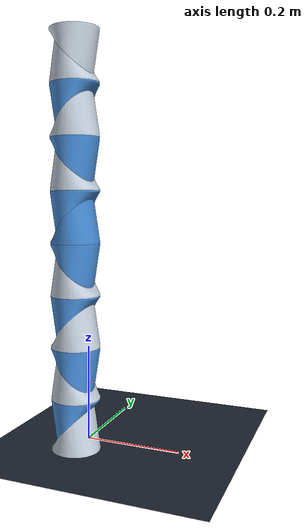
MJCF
<?xml version='1.0' encoding='utf-8'?>
<mujoco model="zbot_8s_bird">
  <compiler angle="radian" autolimits="true" fusestatic="false" />
  <option timestep="0.001666666667" gravity="0 0 -9.81" integrator="implicitfast" iterations="100" />
  <default>
    <geom friction="1 0.005 0.0001" condim="3" />
    <joint damping="5" armature="0" />
  </default>
  <asset>
    <mesh name="mesh_6a4a9a5e8bc7" vertex="0.0224838499 0.03857645765 0.07548385113 0.02081907541 0.04040519521 0.07381907105 -0.02641064674 0.03322708607 0.0265893545 -0.03108550794 0.02382477745 0.02191449329 -0.03206166625 0.02108754031 0.02093833499 0.02477702685 0.0356541574 0.07777702808 -0.02956196107 0.02742083371 0.02343804017 0.02895987034 0.0286740195 0.08195986599 0.02727767639 0.03179696575 0.0802776739 -0.02349979803 -0.03734437376 0.02950020134 0.02563802339 0.03441534564 0.07863802463 0.0224838499 -0.03857645765 0.07548385113 0.02361308411 -0.03720106184 0.07661308348 0.03165234253 0.02228677645 0.0846523419 -0.01837768219 0.04271357134 0.03462231532 -0.01976176165 0.04145590961 0.03323823959 -0.02727767639 0.03179696575 0.02572232485 -0.0224838499 -0.03857645765 0.03051615134 -0.01939466782 -0.04180207849 0.03360533342 -0.01684666239 -0.04396154732 0.03615333885 -0.01491674688 -0.04533834755 0.03808325157 -0.01375637855 -0.04606815428 0.03924361989 0.01946095005 -0.04174026474 0.07246094942 0.0351726599 -0.005109163001 0.08817265928 0.03532674909 -0.002027190058 0.08832675219 0.03108550794 0.02382477745 0.08408550918 0.01976176165 0.04145590961 0.07276175916 -0.00870385766 0.04847085103 0.04429614171 -0.01050874218 0.047750514 0.04249125719 -0.02264680341 0.03838508576 0.03035319783 -0.02499509789 0.03534840792 0.02800490335 -0.03257510439 0.01945445687 0.02042489685 -0.03387392312 0.01435601339 0.01912607811 -0.03463650867 0.01007143594 0.01836349256 -0.0349765718 0.007337867748 0.01802342758 -0.03535534069 6.172924174e-18 0.01764466055 -0.03518454731 -0.004941008519 0.01781545207 -0.02931375615 -0.02794735134 0.02368624508 -0.02714639157 -0.03202058002 0.02585360967 -0.02499509789 -0.03534840792 0.02800490335 -0.01369569078 0.04610438645 0.03930430859 -0.01684666239 0.04396154732 0.03615333885 -0.01015712786 -0.04790246114 0.04284286872 -0.007121580653 -0.04898342118 0.04587841779 -0.005194843281 -0.0494630523 0.04780515656 0.007121580653 -0.04898342118 0.06012158096 0.009944546036 -0.04799157009 0.06294454634 0.01050874218 -0.047750514 0.06350874156 0.03474580869 -0.009284628555 0.08774580806 -0.0351726599 -0.005109163001 0.01782733947 -0.03427562118 -0.01230044011 0.01872438006 -0.03376471251 -0.01486160513 0.01923528686 2.550383293e-18 -0.05000000075 0.05299999937 0.004784112331 -0.04954525083 0.05778411031 0.01487020124 -0.04536899552 0.06787019968 0.01684666239 -0.04396154732 0.0698466599 0.02543992735 -0.0347080119 0.07843992859 0.02727767639 -0.03179696575 0.0802776739 0.03257510439 -0.01945445687 0.08557510376 0.02876111679 -0.02907045931 0.0817611143 0.03144371882 -0.02286814339 0.08444371819 0.01645559072 0.04425765574 0.06945559382 0.01375637855 0.04606815428 0.06675637513 -0.007121580653 0.04898342118 0.04587841779 0.01178112999 0.04715235904 0.06478112936 -0.003500153543 0.04975758493 0.04949984699 0.006879420485 0.04905232042 0.05987941846 0.001735430444 0.04994069412 0.05473542958 -0.03260317445 -0.01936039701 0.02039682679 -0.03020634316 -0.02598234639 0.02279365622 0.03344704583 -0.01623394899 0.08644704521 0.03535214812 0.0006779010291 0.08835215122 0.0351726599 0.005109163001 0.08817265928 0.03488681838 0.008152623661 0.08788681775 0.03364415467 0.0153985098 0.08664415032 0.03257510439 0.01945445687 0.08557510376 -0.02208024822 -0.04396154732 0.01128833462 -0.02382374555 -0.04395940527 0.003000000026 -0.01945119724 -0.0460613817 0.003000000026 -0.02169418707 0.04504844174 0.003000000026 -0.02382355742 0.04395950586 0.003000000026 -0.02033571899 0.04396154732 0.0195766706 -0.01485816017 0.04774133489 0.003000000026 -0.0194518175 0.04606112093 0.003000000026 -0.01660541818 0.04606815428 0.02112181112 -0.04245715588 0.005109163001 0.01041366998 -0.04180996493 0.01007143594 0.0106817456 -0.04874639586 0.011126047 0.003000000026 -0.04874639586 0.011126047 0.003000000026 -0.04180996493 0.01007143594 0.0106817456 -0.0477412045 0.01485858019 0.003000000026 -0.0477412045 0.01485858019 0.003000000026 -0.04180996493 0.01007143594 0.0106817456 -0.04075761512 0.01486160513 0.01111764275 -0.0477412045 0.01485858019 0.003000000026 -0.04075761512 0.01486160513 0.01111764275 -0.0459763892 0.01965125091 0.003000000026 -0.03932162747 0.01945445687 0.01171244774 -0.0375235267 0.02382477745 0.01245724596 -0.04074253514 0.02382477745 0.007728623226 -0.04074253514 0.02382477745 0.007728623226 -0.0375235267 0.02382477745 0.01245724596 -0.03538483381 0.02794735134 0.01334312186 -0.04074253514 0.02382477745 0.007728623226 -0.03538483381 0.02794735134 0.01334312186 -0.03842037171 0.02794735134 0.008171561174 -0.03842037171 0.02794735134 0.008171561174 -0.03538483381 0.02794735134 0.01334312186 -0.03292706609 0.03179696575 0.01436116174 -0.03842037171 0.02794735134 0.008171561174 -0.03292706609 0.03179696575 0.01436116174 -0.03575176373 0.03179696575 0.008680581115 -0.03575176373 0.03179696575 0.008680581115 -0.03292706609 0.03179696575 0.01436116174 -0.03017175198 0.03534840792 0.01550245099 -0.03575176373 0.03179696575 0.008680581115 -0.03017175198 0.03534840792 0.01550245099 -0.03276007995 0.03534840792 0.00925122574 -0.03276007995 0.03534840792 0.00925122574 -0.03017175198 0.03534840792 0.01550245099 -0.02714040875 0.03857645765 0.01675807498 -0.03276007995 0.03534840792 0.00925122574 -0.02714040875 0.03857645765 0.01675807498 -0.02946868725 0.03857645765 0.009879037738 -0.02385455556 0.04145590961 0.01811911911 -0.02033571899 0.04396154732 0.0195766706 -0.02590095438 0.04145590961 0.0105595598 -0.02590095438 0.04145590961 0.0105595598 -0.02033571899 0.04396154732 0.0195766706 -0.02382355742 0.04395950586 0.003000000026 -0.02590095438 0.04145590961 0.0105595598 -0.02382355742 0.04395950586 0.003000000026 -0.02794916555 0.04145894572 0.003000000026 -0.02794916555 0.04145894572 0.003000000026 -0.0293892622 0.04045084864 0.003000000026 -0.02590095438 0.04145590961 0.0105595598 -0.02590095438 0.04145590961 0.0105595598 -0.0293892622 0.04045084864 0.003000000026 -0.02946868725 0.03857645765 0.009879037738 -0.02590095438 0.04145590961 0.0105595598 -0.02946868725 0.03857645765 0.009879037738 -0.02385455556 0.04145590961 0.01811911911 -0.02385455556 0.04145590961 0.01811911911 -0.02946868725 0.03857645765 0.009879037738 -0.02714040875 0.03857645765 0.01675807498 -0.04075761512 0.01486160513 0.01111764275 -0.03932162747 0.01945445687 0.01171244774 -0.0459763892 0.01965125091 0.003000000026 -0.0459763892 0.01965125091 0.003000000026 -0.03932162747 0.01945445687 0.01171244774 -0.04074253514 0.02382477745 0.007728623226 -0.0459763892 0.01965125091 0.003000000026 -0.04074253514 0.02382477745 0.007728623226 -0.0439594537 0.02382365055 0.003000000026 -0.0439594537 0.02382365055 0.003000000026 -0.04074253514 0.02382477745 0.007728623226 -0.03842037171 0.02794735134 0.008171561174 -0.0439594537 0.02382365055 0.003000000026 -0.03842037171 0.02794735134 0.008171561174 -0.04172866419 0.02754484862 0.003000000026 -0.04172866419 0.02754484862 0.003000000026 -0.03842037171 0.02794735134 0.008171561174 -0.03575176373 0.03179696575 0.008680581115 -0.04172866419 0.02754484862 0.003000000026 -0.03575176373 0.03179696575 0.008680581115 -0.03858279064 0.03180201724 0.003000000026 -0.03858279064 0.03180201724 0.003000000026 -0.03575176373 0.03179696575 0.008680581115 -0.03276007995 0.03534840792 0.00925122574 -0.03858279064 0.03180201724 0.003000000026 -0.03276007995 0.03534840792 0.00925122574 -0.03613974154 0.03455313295 0.003000000026 -0.03613974154 0.03455313295 0.003000000026 -0.03276007995 0.03534840792 0.00925122574 -0.02946868725 0.03857645765 0.009879037738 -0.03613974154 0.03455313295 0.003000000026 -0.02946868725 0.03857645765 0.009879037738 -0.03180229664 0.03858255967 0.003000000026 -0.03180229664 0.03858255967 0.003000000026 -0.02946868725 0.03857645765 0.009879037738 -0.0293892622 0.04045084864 0.003000000026 0.02033571899 0.04396154732 0.03642332926 0.02169418707 0.04504844174 0.003000000026 0.01660541818 0.04606815428 0.03487818688 0.01660541818 0.04606815428 0.03487818688 0.02169418707 0.04504844174 0.003000000026 0.0194518175 0.04606112093 0.003000000026 0.01660541818 0.04606815428 0.03487818688 0.0194518175 0.04606112093 0.003000000026 0.01268517412 0.047750514 0.03325437009 0.01268517412 0.047750514 0.03325437009 0.0194518175 0.04606112093 0.003000000026 0.01330184191 0.04819814488 0.003000000026 0.01268517412 0.047750514 0.03325437009 0.01330184191 0.04819814488 0.003000000026 0.008596508764 0.04898342118 0.03156078979 -0.01006999146 0.04897545651 0.003000000026 -0.008596508764 0.04898342118 0.02443921007 -0.004481965676 0.04979871586 0.003000000026 -0.004481965676 0.04979871586 0.003000000026 -0.008596508764 0.04898342118 0.02443921007 -0.004360943567 0.04974165186 0.02619363926 -0.004481965676 0.04979871586 0.003000000026 -0.004360943567 0.04974165186 0.02619363926 1.224646794e-17 0.05000000075 0.003000000026 1.224646794e-17 0.05000000075 0.003000000026 -0.004360943567 0.04974165186 0.02619363926 8.508478866e-18 0.05000000075 0.02800000086 1.224646794e-17 0.05000000075 0.003000000026 8.508478866e-18 0.05000000075 0.02800000086 0.004481965676 0.04979871586 0.003000000026 0.004481965676 0.04979871586 0.003000000026 8.508478866e-18 0.05000000075 0.02800000086 0.004360943567 0.04974165186 0.02980636247 0.004481965676 0.04979871586 0.003000000026 0.004360943567 0.04974165186 0.02980636247 0.01006999146 0.04897545651 0.003000000026 0.01268517412 -0.047750514 0.03325437009 0.01756874099 -0.04681174457 0.003000000026 0.01660541818 -0.04606815428 0.03487818688 0.01660541818 -0.04606815428 0.03487818688 0.01756874099 -0.04681174457 0.003000000026 0.01945119724 -0.0460613817 0.003000000026 0.01660541818 -0.04606815428 0.03487818688 0.01945119724 -0.0460613817 0.003000000026 0.02033571899 -0.04396154732 0.03642332926 0.01945119724 -0.0460613817 0.003000000026 0.02382374555 -0.04395940527 0.003000000026 0.02033571899 -0.04396154732 0.03642332926 0.02033571899 -0.04396154732 0.03642332926 0.02382374555 -0.04395940527 0.003000000026 0.02564496361 -0.04292244092 0.003000000026 0.02033571899 -0.04396154732 0.03642332926 0.02564496361 -0.04292244092 0.003000000026 0.02385455556 -0.04145590961 0.0378808789 0.02385455556 -0.04145590961 0.0378808789 0.02564496361 -0.04292244092 0.003000000026 0.02794942819 -0.04145876691 0.003000000026 0.02385455556 -0.04145590961 0.0378808789 0.02794942819 -0.04145876691 0.003000000026 0.02714040875 -0.03857645765 0.03924192488 0.02714040875 -0.03857645765 0.03924192488 0.02794942819 -0.04145876691 0.003000000026 0.03289693594 -0.03765357286 0.003000000026 0.02714040875 -0.03857645765 0.03924192488 0.03289693594 -0.03765357286 0.003000000026 0.03017175198 -0.03534840792 0.04049754888 0.03017175198 -0.03534840792 0.04049754888 0.03289693594 -0.03765357286 0.003000000026 0.03535549343 -0.03535518423 0.003000000026 0.03017175198 -0.03534840792 0.04049754888 0.03535549343 -0.03535518423 0.003000000026 0.03292706609 -0.03179696575 0.04163883626 0.03292706609 -0.03179696575 0.04163883626 0.03535549343 -0.03535518423 0.003000000026 0.03909157589 -0.03117449023 0.003000000026 0.03292706609 -0.03179696575 0.04163883626 0.03909157589 -0.03117449023 0.003000000026 0.03538483381 -0.02794735134 0.04265687615 0.03538483381 -0.02794735134 0.04265687615 0.03909157589 -0.03117449023 0.003000000026 0.04145885631 -0.02794929594 0.003000000026 0.03538483381 -0.02794735134 0.04265687615 0.04145885631 -0.02794929594 0.003000000026 0.0375235267 -0.02382477745 0.04354275391 0.0375235267 -0.02382477745 0.04354275391 0.04145885631 -0.02794929594 0.003000000026 0.04402977601 -0.02369343303 0.003000000026 0.0375235267 -0.02382477745 0.04354275391 0.04402977601 -0.02369343303 0.003000000026 0.03932162747 -0.01945445687 0.04428755119 0.03932162747 -0.01945445687 0.04428755119 0.04402977601 -0.02369343303 0.003000000026 0.04606125131 -0.0194515083 0.003000000026 0.03932162747 -0.01945445687 0.04428755119 0.04606125131 -0.0194515083 0.003000000026 0.04075761512 -0.01486160513 0.0448823534 0.04075761512 -0.01486160513 0.0448823534 0.04606125131 -0.0194515083 0.003000000026 0.04755282402 -0.01545085013 0.003000000026 0.04075761512 -0.01486160513 0.0448823534 0.04755282402 -0.01545085013 0.003000000026 0.04180996493 -0.01007143594 0.04531825334 0.04180996493 -0.01007143594 0.04531825334 0.04755282402 -0.01545085013 0.003000000026 0.04897552729 -0.0100696357 0.003000000026 0.04180996493 -0.01007143594 0.04531825334 0.04897552729 -0.0100696357 0.003000000026 0.04245715588 -0.005109163001 0.04558632895 0.04245715588 -0.005109163001 0.04558632895 0.04897552729 -0.0100696357 0.003000000026 0.04954748973 -0.006711663213 0.003000000026 0.04245715588 -0.005109163001 0.04558632895 0.04954748973 -0.006711663213 0.003000000026 0.04267767072 -6.310709456e-18 0.04567766935 -0.02382374555 -0.04395940527 0.003000000026 -0.02208024822 -0.04396154732 0.01128833462 -0.02564496361 -0.04292244092 0.003000000026 -0.02564496361 -0.04292244092 0.003000000026 -0.02208024822 -0.04396154732 0.01128833462 -0.02590095438 -0.04145590961 0.0105595598 -0.02564496361 -0.04292244092 0.003000000026 -0.02590095438 -0.04145590961 0.0105595598 -0.02794942819 -0.04145876691 0.003000000026 -0.02794942819 -0.04145876691 0.003000000026 -0.02590095438 -0.04145590961 0.0105595598 -0.02946868725 -0.03857645765 0.009879037738 -0.02794942819 -0.04145876691 0.003000000026 -0.02946868725 -0.03857645765 0.009879037738 -0.03180173412 -0.03858302161 0.003000000026 -0.03376471251 -0.01486160513 0.01923528686 -0.03427562118 -0.01230044011 0.01872438006 -0.04180996493 -0.01007143594 0.0106817456 -0.04180996493 -0.01007143594 0.0106817456 -0.03427562118 -0.01230044011 0.01872438006 -0.04245715588 -0.005109163001 0.01041366998 -0.04180996493 -0.01007143594 0.0106817456 -0.04245715588 -0.005109163001 0.01041366998 -0.04954748973 -0.006711663213 0.003000000026 -0.04897552729 -0.0100696357 0.003000000026 -0.04755282402 -0.01545085013 0.003000000026 -0.04075761512 -0.01486160513 0.01111764275 -0.03180173412 -0.03858302161 0.003000000026 -0.02946868725 -0.03857645765 0.009879037738 -0.03289693594 -0.03765357286 0.003000000026 -0.03289693594 -0.03765357286 0.003000000026 -0.02946868725 -0.03857645765 0.009879037738 -0.03276007995 -0.03534840792 0.00925122574 -0.03289693594 -0.03765357286 0.003000000026 -0.03276007995 -0.03534840792 0.00925122574 -0.03535549343 -0.03535518423 0.003000000026 -0.03535549343 -0.03535518423 0.003000000026 -0.03276007995 -0.03534840792 0.00925122574 -0.03575176373 -0.03179696575 0.008680581115 -0.03535549343 -0.03535518423 0.003000000026 -0.03575176373 -0.03179696575 0.008680581115 -0.03909157589 -0.03117449023 0.003000000026 -0.03909157589 -0.03117449023 0.003000000026 -0.03575176373 -0.03179696575 0.008680581115 -0.03842037171 -0.02794735134 0.008171561174 -0.03909157589 -0.03117449023 0.003000000026 -0.03842037171 -0.02794735134 0.008171561174 -0.04145885631 -0.02794929594 0.003000000026 -0.04145885631 -0.02794929594 0.003000000026 -0.03842037171 -0.02794735134 0.008171561174 -0.04074253514 -0.02382477745 0.007728623226 -0.04145885631 -0.02794929594 0.003000000026 -0.04074253514 -0.02382477745 0.007728623226 -0.04402977601 -0.02369343303 0.003000000026 -0.04402977601 -0.02369343303 0.003000000026 -0.04074253514 -0.02382477745 0.007728623226 -0.04269488901 -0.01945445687 0.007356224116 -0.04402977601 -0.02369343303 0.003000000026 -0.04269488901 -0.01945445687 0.007356224116 -0.04606125131 -0.0194515083 0.003000000026 -0.04755282402 -0.01545085013 0.003000000026 -0.04606125131 -0.0194515083 0.003000000026 -0.04075761512 -0.01486160513 0.01111764275 -0.04075761512 -0.01486160513 0.01111764275 -0.04606125131 -0.0194515083 0.003000000026 -0.04269488901 -0.01945445687 0.007356224116 -0.04075761512 -0.01486160513 0.01111764275 -0.04269488901 -0.01945445687 0.007356224116 -0.03932162747 -0.01945445687 0.01171244774 -0.03932162747 -0.01945445687 0.01171244774 -0.04269488901 -0.01945445687 0.007356224116 -0.04074253514 -0.02382477745 0.007728623226 -0.03932162747 -0.01945445687 0.01171244774 -0.04074253514 -0.02382477745 0.007728623226 -0.0375235267 -0.02382477745 0.01245724596 -0.0375235267 -0.02382477745 0.01245724596 -0.04074253514 -0.02382477745 0.007728623226 -0.03842037171 -0.02794735134 0.008171561174 -0.0375235267 -0.02382477745 0.01245724596 -0.03842037171 -0.02794735134 0.008171561174 -0.03538483381 -0.02794735134 0.01334312186 -0.03538483381 -0.02794735134 0.01334312186 -0.03842037171 -0.02794735134 0.008171561174 -0.03575176373 -0.03179696575 0.008680581115 -0.03538483381 -0.02794735134 0.01334312186 -0.03575176373 -0.03179696575 0.008680581115 -0.03292706609 -0.03179696575 0.01436116174 -0.03292706609 -0.03179696575 0.01436116174 -0.03575176373 -0.03179696575 0.008680581115 -0.03276007995 -0.03534840792 0.00925122574 -0.03292706609 -0.03179696575 0.01436116174 -0.03276007995 -0.03534840792 0.00925122574 -0.03017175198 -0.03534840792 0.01550245099 -0.03017175198 -0.03534840792 0.01550245099 -0.03276007995 -0.03534840792 0.00925122574 -0.02946868725 -0.03857645765 0.009879037738 -0.03017175198 -0.03534840792 0.01550245099 -0.02946868725 -0.03857645765 0.009879037738 -0.02714040875 -0.03857645765 0.01675807498 -0.02714040875 -0.03857645765 0.01675807498 -0.02946868725 -0.03857645765 0.009879037738 -0.02590095438 -0.04145590961 0.0105595598 -0.02714040875 -0.03857645765 0.01675807498 -0.02590095438 -0.04145590961 0.0105595598 -0.02385455556 -0.04145590961 0.01811911911 -0.02385455556 -0.04145590961 0.01811911911 -0.02590095438 -0.04145590961 0.0105595598 -0.02208024822 -0.04396154732 0.01128833462 -0.02385455556 -0.04145590961 0.01811911911 -0.02208024822 -0.04396154732 0.01128833462 -0.02033571899 -0.04396154732 0.0195766706 -0.02033571899 -0.04396154732 0.0195766706 -0.02208024822 -0.04396154732 0.01128833462 -0.01945119724 -0.0460613817 0.003000000026 -0.02033571899 -0.04396154732 0.0195766706 -0.01945119724 -0.0460613817 0.003000000026 -0.01660541818 -0.04606815428 0.02112181112 -0.01660541818 -0.04606815428 0.02112181112 -0.01945119724 -0.0460613817 0.003000000026 -0.01756874099 -0.04681174457 0.003000000026 -0.01660541818 -0.04606815428 0.02112181112 -0.01756874099 -0.04681174457 0.003000000026 -0.01268517412 -0.047750514 0.02274562977 -0.01268517412 -0.047750514 0.02274562977 -0.01756874099 -0.04681174457 0.003000000026 -0.01485900022 -0.04774107412 0.003000000026 -0.01268517412 -0.047750514 0.02274562977 -0.01485900022 -0.04774107412 0.003000000026 -0.008596508764 -0.04898342118 0.02443921007 -0.008596508764 -0.04898342118 0.02443921007 -0.01485900022 -0.04774107412 0.003000000026 -0.008927844465 -0.04919647798 0.003000000026 -0.008596508764 -0.04898342118 0.02443921007 -0.008927844465 -0.04919647798 0.003000000026 -0.004360943567 -0.04974165186 0.02619363926 -0.004360943567 -0.04974165186 0.02619363926 -0.008927844465 -0.04919647798 0.003000000026 -0.005108862184 -0.04973831028 0.003000000026 -0.004360943567 -0.04974165186 0.02619363926 -0.005108862184 -0.04973831028 0.003000000026 -9.809521473e-18 -0.05000000075 0.02800000086 -9.809521473e-18 -0.05000000075 0.02800000086 -0.005108862184 -0.04973831028 0.003000000026 -1.836970179e-17 -0.05000000075 0.003000000026 -9.809521473e-18 -0.05000000075 0.02800000086 -1.836970179e-17 -0.05000000075 0.003000000026 0.004360943567 -0.04974165186 0.02980636247 0.004360943567 -0.04974165186 0.02980636247 -1.836970179e-17 -0.05000000075 0.003000000026 0.005108862184 -0.04973831028 0.003000000026 0.004360943567 -0.04974165186 0.02980636247 0.005108862184 -0.04973831028 0.003000000026 0.008596508764 -0.04898342118 0.03156078979 0.008596508764 -0.04898342118 0.03156078979 0.005108862184 -0.04973831028 0.003000000026 0.008927844465 -0.04919647798 0.003000000026 0.008596508764 -0.04898342118 0.03156078979 0.008927844465 -0.04919647798 0.003000000026 0.01268517412 -0.047750514 0.03325437009 0.01268517412 -0.047750514 0.03325437009 0.008927844465 -0.04919647798 0.003000000026 0.01485900022 -0.04774107412 0.003000000026 0.01268517412 -0.047750514 0.03325437009 0.01485900022 -0.04774107412 0.003000000026 0.01756874099 -0.04681174457 0.003000000026 0.03017175198 -0.03534840792 0.04049754888 0.02361308411 -0.03720106184 0.07661308348 0.02714040875 -0.03857645765 0.03924192488 0.02714040875 -0.03857645765 0.03924192488 0.02361308411 -0.03720106184 0.07661308348 0.0224838499 -0.03857645765 0.07548385113 0.02714040875 -0.03857645765 0.03924192488 0.0224838499 -0.03857645765 0.07548385113 0.02385455556 -0.04145590961 0.0378808789 0.02385455556 -0.04145590961 0.0378808789 0.0224838499 -0.03857645765 0.07548385113 0.01946095005 -0.04174026474 0.07246094942 0.02385455556 -0.04145590961 0.0378808789 0.01946095005 -0.04174026474 0.07246094942 0.02033571899 -0.04396154732 0.03642332926 0.02033571899 -0.04396154732 0.03642332926 0.01946095005 -0.04174026474 0.07246094942 0.01684666239 -0.04396154732 0.0698466599 0.02033571899 -0.04396154732 0.03642332926 0.01684666239 -0.04396154732 0.0698466599 0.01660541818 -0.04606815428 0.03487818688 0.01660541818 -0.04606815428 0.03487818688 0.01684666239 -0.04396154732 0.0698466599 0.01487020124 -0.04536899552 0.06787019968 0.01660541818 -0.04606815428 0.03487818688 0.01487020124 -0.04536899552 0.06787019968 0.01268517412 -0.047750514 0.03325437009 0.04267767072 -6.310709456e-18 0.04567766935 0.03532674909 -0.002027190058 0.08832675219 0.04245715588 -0.005109163001 0.04558632895 0.04245715588 -0.005109163001 0.04558632895 0.03532674909 -0.002027190058 0.08832675219 0.0351726599 -0.005109163001 0.08817265928 0.04245715588 -0.005109163001 0.04558632895 0.0351726599 -0.005109163001 0.08817265928 0.04180996493 -0.01007143594 0.04531825334 0.04180996493 -0.01007143594 0.04531825334 0.0351726599 -0.005109163001 0.08817265928 0.03474580869 -0.009284628555 0.08774580806 0.04180996493 -0.01007143594 0.04531825334 0.03474580869 -0.009284628555 0.08774580806 0.04075761512 -0.01486160513 0.0448823534 0.04075761512 -0.01486160513 0.0448823534 0.03474580869 -0.009284628555 0.08774580806 0.03344704583 -0.01623394899 0.08644704521 0.04075761512 -0.01486160513 0.0448823534 0.03344704583 -0.01623394899 0.08644704521 0.03932162747 -0.01945445687 0.04428755119 0.03932162747 -0.01945445687 0.04428755119 0.03344704583 -0.01623394899 0.08644704521 0.03257510439 -0.01945445687 0.08557510376 0.03932162747 -0.01945445687 0.04428755119 0.03257510439 -0.01945445687 0.08557510376 0.0375235267 -0.02382477745 0.04354275391 0.0375235267 -0.02382477745 0.04354275391 0.03257510439 -0.01945445687 0.08557510376 0.03144371882 -0.02286814339 0.08444371819 0.0375235267 -0.02382477745 0.04354275391 0.03144371882 -0.02286814339 0.08444371819 0.03538483381 -0.02794735134 0.04265687615 0.03538483381 -0.02794735134 0.04265687615 0.03144371882 -0.02286814339 0.08444371819 0.02876111679 -0.02907045931 0.0817611143 0.03538483381 -0.02794735134 0.04265687615 0.02876111679 -0.02907045931 0.0817611143 0.03292706609 -0.03179696575 0.04163883626 0.03292706609 -0.03179696575 0.04163883626 0.02876111679 -0.02907045931 0.0817611143 0.02727767639 -0.03179696575 0.0802776739 0.03292706609 -0.03179696575 0.04163883626 0.02727767639 -0.03179696575 0.0802776739 0.03017175198 -0.03534840792 0.04049754888 0.03017175198 -0.03534840792 0.04049754888 0.02727767639 -0.03179696575 0.0802776739 0.02543992735 -0.0347080119 0.07843992859 0.03017175198 -0.03534840792 0.04049754888 0.02543992735 -0.0347080119 0.07843992859 0.02361308411 -0.03720106184 0.07661308348 -0.0151808979 -0.04606815428 0.03018271737 -0.01375637855 -0.04606815428 0.03924361989 -0.01491674688 -0.04533834755 0.03808325157 -0.0151808979 -0.04606815428 0.03018271737 -0.01491674688 -0.04533834755 0.03808325157 -0.01859118976 -0.04396154732 0.02786500379 -0.01491674688 -0.04533834755 0.03808325157 -0.01684666239 -0.04396154732 0.03615333885 -0.01859118976 -0.04396154732 0.02786500379 -0.01859118976 -0.04396154732 0.02786500379 -0.01684666239 -0.04396154732 0.03615333885 -0.01939466782 -0.04180207849 0.03360533342 -0.01859118976 -0.04396154732 0.02786500379 -0.01939466782 -0.04180207849 0.03360533342 -0.02180815861 -0.04145590961 0.02567867935 -0.02180815861 -0.04145590961 0.02567867935 -0.01939466782 -0.04180207849 0.03360533342 -0.0224838499 -0.03857645765 0.03051615134 -0.02180815861 -0.04145590961 0.02567867935 -0.0224838499 -0.03857645765 0.03051615134 -0.02481212839 -0.03857645765 0.02363711223 -0.02481212839 -0.03857645765 0.02363711223 -0.0224838499 -0.03857645765 0.03051615134 -0.02349979803 -0.03734437376 0.02950020134 -0.02481212839 -0.03857645765 0.02363711223 -0.02349979803 -0.03734437376 0.02950020134 -0.02758342586 -0.03534840792 0.02175367624 -0.03376471251 -0.01486160513 0.01923528686 -0.03594836593 -0.01945445687 0.01606867276 -0.03260317445 -0.01936039701 0.02039682679 -0.03260317445 -0.01936039701 0.02039682679 -0.03594836593 -0.01945445687 0.01606867276 -0.03430451825 -0.02382477745 0.0171858687 -0.03260317445 -0.01936039701 0.02039682679 -0.03430451825 -0.02382477745 0.0171858687 -0.03020634316 -0.02598234639 0.02279365622 -0.03020634316 -0.02598234639 0.02279365622 -0.03430451825 -0.02382477745 0.0171858687 -0.03234929591 -0.02794735134 0.01851468347 -0.03020634316 -0.02598234639 0.02279365622 -0.03234929591 -0.02794735134 0.01851468347 -0.02931375615 -0.02794735134 0.02368624508 -0.02931375615 -0.02794735134 0.02368624508 -0.03234929591 -0.02794735134 0.01851468347 -0.03010237217 -0.03179696575 0.02004174329 -0.02931375615 -0.02794735134 0.02368624508 -0.03010237217 -0.03179696575 0.02004174329 -0.02714639157 -0.03202058002 0.02585360967 -0.02714639157 -0.03202058002 0.02585360967 -0.03010237217 -0.03179696575 0.02004174329 -0.02758342586 -0.03534840792 0.02175367624 -0.02714639157 -0.03202058002 0.02585360967 -0.02758342586 -0.03534840792 0.02175367624 -0.02499509789 -0.03534840792 0.02800490335 -0.02499509789 -0.03534840792 0.02800490335 -0.02758342586 -0.03534840792 0.02175367624 -0.02349979803 -0.03734437376 0.02950020134 -0.04954748973 -0.006711663213 0.003000000026 -0.04897552729 -0.0100696357 0.003000000026 -0.04180996493 -0.01007143594 0.0106817456 -0.04180996493 -0.01007143594 0.0106817456 -0.04897552729 -0.0100696357 0.003000000026 -0.04075761512 -0.01486160513 0.01111764275 -0.04180996493 -0.01007143594 0.0106817456 -0.04075761512 -0.01486160513 0.01111764275 -0.03376471251 -0.01486160513 0.01923528686 -0.03376471251 -0.01486160513 0.01923528686 -0.04075761512 -0.01486160513 0.01111764275 -0.03932162747 -0.01945445687 0.01171244774 -0.03376471251 -0.01486160513 0.01923528686 -0.03932162747 -0.01945445687 0.01171244774 -0.03594836593 -0.01945445687 0.01606867276 -0.03594836593 -0.01945445687 0.01606867276 -0.03932162747 -0.01945445687 0.01171244774 -0.0375235267 -0.02382477745 0.01245724596 -0.03594836593 -0.01945445687 0.01606867276 -0.0375235267 -0.02382477745 0.01245724596 -0.03430451825 -0.02382477745 0.0171858687 -0.03430451825 -0.02382477745 0.0171858687 -0.0375235267 -0.02382477745 0.01245724596 -0.03538483381 -0.02794735134 0.01334312186 -0.03430451825 -0.02382477745 0.0171858687 -0.03538483381 -0.02794735134 0.01334312186 -0.03234929591 -0.02794735134 0.01851468347 -0.03234929591 -0.02794735134 0.01851468347 -0.03538483381 -0.02794735134 0.01334312186 -0.03292706609 -0.03179696575 0.01436116174 -0.03234929591 -0.02794735134 0.01851468347 -0.03292706609 -0.03179696575 0.01436116174 -0.03010237217 -0.03179696575 0.02004174329 -0.03010237217 -0.03179696575 0.02004174329 -0.03292706609 -0.03179696575 0.01436116174 -0.03017175198 -0.03534840792 0.01550245099 -0.03010237217 -0.03179696575 0.02004174329 -0.03017175198 -0.03534840792 0.01550245099 -0.02758342586 -0.03534840792 0.02175367624 -0.02758342586 -0.03534840792 0.02175367624 -0.03017175198 -0.03534840792 0.01550245099 -0.02714040875 -0.03857645765 0.01675807498 -0.02758342586 -0.03534840792 0.02175367624 -0.02714040875 -0.03857645765 0.01675807498 -0.02481212839 -0.03857645765 0.02363711223 -0.02481212839 -0.03857645765 0.02363711223 -0.02714040875 -0.03857645765 0.01675807498 -0.02385455556 -0.04145590961 0.01811911911 -0.02481212839 -0.03857645765 0.02363711223 -0.02385455556 -0.04145590961 0.01811911911 -0.02180815861 -0.04145590961 0.02567867935 -0.02180815861 -0.04145590961 0.02567867935 -0.02385455556 -0.04145590961 0.01811911911 -0.02033571899 -0.04396154732 0.0195766706 -0.02180815861 -0.04145590961 0.02567867935 -0.02033571899 -0.04396154732 0.0195766706 -0.01859118976 -0.04396154732 0.02786500379 -0.01859118976 -0.04396154732 0.02786500379 -0.02033571899 -0.04396154732 0.0195766706 -0.01660541818 -0.04606815428 0.02112181112 -0.01859118976 -0.04396154732 0.02786500379 -0.01660541818 -0.04606815428 0.02112181112 -0.0151808979 -0.04606815428 0.03018271737 -0.0151808979 -0.04606815428 0.03018271737 -0.01660541818 -0.04606815428 0.02112181112 -0.01268517412 -0.047750514 0.02274562977 -0.01375637855 -0.04606815428 0.03924361989 0.01487020124 -0.04536899552 0.06787019968 0.01050874218 -0.047750514 0.06350874156 0.01268517412 -0.047750514 0.03325437009 0.01268517412 -0.047750514 0.03325437009 0.01050874218 -0.047750514 0.06350874156 0.009944546036 -0.04799157009 0.06294454634 0.01268517412 -0.047750514 0.03325437009 0.009944546036 -0.04799157009 0.06294454634 0.008596508764 -0.04898342118 0.03156078979 0.008596508764 -0.04898342118 0.03156078979 0.009944546036 -0.04799157009 0.06294454634 0.007121580653 -0.04898342118 0.06012158096 0.008596508764 -0.04898342118 0.03156078979 0.007121580653 -0.04898342118 0.06012158096 0.004360943567 -0.04974165186 0.02980636247 0.004360943567 -0.04974165186 0.02980636247 0.007121580653 -0.04898342118 0.06012158096 0.004784112331 -0.04954525083 0.05778411031 0.004360943567 -0.04974165186 0.02980636247 0.004784112331 -0.04954525083 0.05778411031 -9.809521473e-18 -0.05000000075 0.02800000086 -9.809521473e-18 -0.05000000075 0.02800000086 0.004784112331 -0.04954525083 0.05778411031 2.550383293e-18 -0.05000000075 0.05299999937 -9.809521473e-18 -0.05000000075 0.02800000086 2.550383293e-18 -0.05000000075 0.05299999937 -0.004360943567 -0.04974165186 0.02619363926 -0.004360943567 -0.04974165186 0.02619363926 2.550383293e-18 -0.05000000075 0.05299999937 -0.005194843281 -0.0494630523 0.04780515656 -0.004360943567 -0.04974165186 0.02619363926 -0.005194843281 -0.0494630523 0.04780515656 -0.008596508764 -0.04898342118 0.02443921007 -0.008596508764 -0.04898342118 0.02443921007 -0.005194843281 -0.0494630523 0.04780515656 -0.007121580653 -0.04898342118 0.04587841779 -0.008596508764 -0.04898342118 0.02443921007 -0.007121580653 -0.04898342118 0.04587841779 -0.01268517412 -0.047750514 0.02274562977 -0.01268517412 -0.047750514 0.02274562977 -0.007121580653 -0.04898342118 0.04587841779 -0.01015712786 -0.04790246114 0.04284286872 -0.01268517412 -0.047750514 0.02274562977 -0.01015712786 -0.04790246114 0.04284286872 -0.01375637855 -0.04606815428 0.03924361989 -0.02727767639 0.03179696575 0.02572232485 -0.03234929591 0.02794735134 0.01851468347 -0.02956196107 0.02742083371 0.02343804017 -0.02956196107 0.02742083371 0.02343804017 -0.03234929591 0.02794735134 0.01851468347 -0.03430451825 0.02382477745 0.0171858687 -0.02956196107 0.02742083371 0.02343804017 -0.03430451825 0.02382477745 0.0171858687 -0.03108550794 0.02382477745 0.02191449329 -0.02641064674 0.03322708607 0.0265893545 -0.02758342586 0.03534840792 0.02175367624 -0.02727767639 0.03179696575 0.02572232485 -0.02727767639 0.03179696575 0.02572232485 -0.02758342586 0.03534840792 0.02175367624 -0.03010237217 0.03179696575 0.02004174329 -0.02727767639 0.03179696575 0.02572232485 -0.03010237217 0.03179696575 0.02004174329 -0.03234929591 0.02794735134 0.01851468347 -0.01976176165 0.04145590961 0.03323823959 -0.02481212839 0.03857645765 0.02363711223 -0.02264680341 0.03838508576 0.03035319783 -0.02264680341 0.03838508576 0.03035319783 -0.02481212839 0.03857645765 0.02363711223 -0.02758342586 0.03534840792 0.02175367624 -0.02264680341 0.03838508576 0.03035319783 -0.02758342586 0.03534840792 0.02175367624 -0.02499509789 0.03534840792 0.02800490335 -0.02499509789 0.03534840792 0.02800490335 -0.02758342586 0.03534840792 0.02175367624 -0.02641064674 0.03322708607 0.0265893545 -0.01837768219 0.04271357134 0.03462231532 -0.01859118976 0.04396154732 0.02786500379 -0.01976176165 0.04145590961 0.03323823959 -0.01976176165 0.04145590961 0.03323823959 -0.01859118976 0.04396154732 0.02786500379 -0.02180815861 0.04145590961 0.02567867935 -0.01976176165 0.04145590961 0.03323823959 -0.02180815861 0.04145590961 0.02567867935 -0.02481212839 0.03857645765 0.02363711223 -0.01369569078 0.04610438645 0.03930430859 -0.01050874218 0.047750514 0.04249125719 -0.01268517412 0.047750514 0.02274562977 -0.01268517412 0.047750514 0.02274562977 -0.01050874218 0.047750514 0.04249125719 -0.008596508764 0.04898342118 0.02443921007 -0.01268517412 0.047750514 0.02274562977 -0.008596508764 0.04898342118 0.02443921007 -0.01330184191 0.04819814488 0.003000000026 -0.01330184191 0.04819814488 0.003000000026 -0.008596508764 0.04898342118 0.02443921007 -0.01006999146 0.04897545651 0.003000000026 -0.01330184191 0.04819814488 0.003000000026 -0.01485816017 0.04774133489 0.003000000026 -0.01268517412 0.047750514 0.02274562977 -0.01268517412 0.047750514 0.02274562977 -0.01485816017 0.04774133489 0.003000000026 -0.01660541818 0.04606815428 0.02112181112 -0.01268517412 0.047750514 0.02274562977 -0.01660541818 0.04606815428 0.02112181112 -0.01369569078 0.04610438645 0.03930430859 -0.01369569078 0.04610438645 0.03930430859 -0.01660541818 0.04606815428 0.02112181112 -0.01859118976 0.04396154732 0.02786500379 -0.01369569078 0.04610438645 0.03930430859 -0.01859118976 0.04396154732 0.02786500379 -0.01684666239 0.04396154732 0.03615333885 -0.01684666239 0.04396154732 0.03615333885 -0.01859118976 0.04396154732 0.02786500379 -0.01837768219 0.04271357134 0.03462231532 -0.03430451825 0.02382477745 0.0171858687 -0.0375235267 0.02382477745 0.01245724596 -0.03430451825 0.02382477745 0.0171858687 -0.03234929591 0.02794735134 0.01851468347 -0.0375235267 0.02382477745 0.01245724596 -0.03234929591 0.02794735134 0.01851468347 -0.03538483381 0.02794735134 0.01334312186 -0.03538483381 0.02794735134 0.01334312186 -0.03234929591 0.02794735134 0.01851468347 -0.03010237217 0.03179696575 0.02004174329 -0.03538483381 0.02794735134 0.01334312186 -0.03010237217 0.03179696575 0.02004174329 -0.03292706609 0.03179696575 0.01436116174 -0.03292706609 0.03179696575 0.01436116174 -0.03292706609 0.03179696575 0.01436116174 -0.02758342586 0.03534840792 0.02175367624 -0.03017175198 0.03534840792 0.01550245099 -0.03017175198 0.03534840792 0.01550245099 -0.02758342586 0.03534840792 0.02175367624 -0.02481212839 0.03857645765 0.02363711223 -0.03017175198 0.03534840792 0.01550245099 -0.02481212839 0.03857645765 0.02363711223 -0.02714040875 0.03857645765 0.01675807498 -0.02714040875 0.03857645765 0.01675807498 -0.02481212839 0.03857645765 0.02363711223 -0.02180815861 0.04145590961 0.02567867935 -0.02714040875 0.03857645765 0.01675807498 -0.02180815861 0.04145590961 0.02567867935 -0.02385455556 0.04145590961 0.01811911911 -0.02385455556 0.04145590961 0.01811911911 -0.02385455556 0.04145590961 0.01811911911 -0.01859118976 0.04396154732 0.02786500379 -0.02033571899 0.04396154732 0.0195766706 -0.02033571899 0.04396154732 0.0195766706 -0.01859118976 0.04396154732 0.02786500379 -0.01660541818 0.04606815428 0.02112181112 -0.02033571899 0.04396154732 0.0195766706 -0.01660541818 0.04606815428 0.02112181112 -0.02169418707 0.04504844174 0.003000000026 -0.02169418707 0.04504844174 0.003000000026 -0.01660541818 0.04606815428 0.02112181112 -0.0194518175 0.04606112093 0.003000000026 0.02714040875 0.03857645765 0.03924192488 0.02385455556 0.04145590961 0.0378808789 0.01976176165 0.04145590961 0.07276175916 0.01976176165 0.04145590961 0.07276175916 0.02385455556 0.04145590961 0.0378808789 0.01645559072 0.04425765574 0.06945559382 0.01645559072 0.04425765574 0.06945559382 0.02385455556 0.04145590961 0.0378808789 0.02033571899 0.04396154732 0.03642332926 0.01645559072 0.04425765574 0.06945559382 0.02033571899 0.04396154732 0.03642332926 0.01375637855 0.04606815428 0.06675637513 0.01375637855 0.04606815428 0.06675637513 0.02033571899 0.04396154732 0.03642332926 0.01660541818 0.04606815428 0.03487818688 0.01375637855 0.04606815428 0.06675637513 0.01660541818 0.04606815428 0.03487818688 0.01178112999 0.04715235904 0.06478112936 0.01178112999 0.04715235904 0.06478112936 0.01660541818 0.04606815428 0.03487818688 0.01268517412 0.047750514 0.03325437009 0.01178112999 0.04715235904 0.06478112936 0.01268517412 0.047750514 0.03325437009 0.006879420485 0.04905232042 0.05987941846 0.006879420485 0.04905232042 0.05987941846 0.01268517412 0.047750514 0.03325437009 0.008596508764 0.04898342118 0.03156078979 0.006879420485 0.04905232042 0.05987941846 0.008596508764 0.04898342118 0.03156078979 0.001735430444 0.04994069412 0.05473542958 0.03017175198 0.03534840792 0.04049754888 0.02563802339 0.03441534564 0.07863802463 0.03292706609 0.03179696575 0.04163883626 0.03292706609 0.03179696575 0.04163883626 0.02563802339 0.03441534564 0.07863802463 0.02727767639 0.03179696575 0.0802776739 0.03292706609 0.03179696575 0.04163883626 0.02727767639 0.03179696575 0.0802776739 0.03538483381 0.02794735134 0.04265687615 0.03538483381 0.02794735134 0.04265687615 0.02727767639 0.03179696575 0.0802776739 0.02895987034 0.0286740195 0.08195986599 0.03538483381 0.02794735134 0.04265687615 0.02895987034 0.0286740195 0.08195986599 0.0375235267 0.02382477745 0.04354275391 0.01976176165 0.04145590961 0.07276175916 0.02081907541 0.04040519521 0.07381907105 0.02714040875 0.03857645765 0.03924192488 0.02714040875 0.03857645765 0.03924192488 0.02081907541 0.04040519521 0.07381907105 0.0224838499 0.03857645765 0.07548385113 0.02714040875 0.03857645765 0.03924192488 0.0224838499 0.03857645765 0.07548385113 0.03017175198 0.03534840792 0.04049754888 0.03017175198 0.03534840792 0.04049754888 0.0224838499 0.03857645765 0.07548385113 0.02477702685 0.0356541574 0.07777702808 0.03017175198 0.03534840792 0.04049754888 0.02477702685 0.0356541574 0.07777702808 0.02563802339 0.03441534564 0.07863802463 0.01330184191 0.04819814488 0.003000000026 0.01006999146 0.04897545651 0.003000000026 0.008596508764 0.04898342118 0.03156078979 0.008596508764 0.04898342118 0.03156078979 0.01006999146 0.04897545651 0.003000000026 0.004360943567 0.04974165186 0.02980636247 0.008596508764 0.04898342118 0.03156078979 0.004360943567 0.04974165186 0.02980636247 0.001735430444 0.04994069412 0.05473542958 0.001735430444 0.04994069412 0.05473542958 0.004360943567 0.04974165186 0.02980636247 8.508478866e-18 0.05000000075 0.02800000086 0.001735430444 0.04994069412 0.05473542958 8.508478866e-18 0.05000000075 0.02800000086 -0.003500153543 0.04975758493 0.04949984699 -0.003500153543 0.04975758493 0.04949984699 8.508478866e-18 0.05000000075 0.02800000086 -0.004360943567 0.04974165186 0.02619363926 -0.003500153543 0.04975758493 0.04949984699 -0.004360943567 0.04974165186 0.02619363926 -0.007121580653 0.04898342118 0.04587841779 -0.007121580653 0.04898342118 0.04587841779 -0.004360943567 0.04974165186 0.02619363926 -0.008596508764 0.04898342118 0.02443921007 -0.007121580653 0.04898342118 0.04587841779 -0.008596508764 0.04898342118 0.02443921007 -0.00870385766 0.04847085103 0.04429614171 -0.00870385766 0.04847085103 0.04429614171 -0.008596508764 0.04898342118 0.02443921007 -0.01050874218 0.047750514 0.04249125719 -0.04874639586 0.011126047 0.003000000026 -0.04973832518 0.005108712241 0.003000000026 -0.04245715588 0.005109163001 0.01041366998 -0.04245715588 0.005109163001 0.01041366998 -0.04973832518 0.005108712241 0.003000000026 -0.04994965345 0.002243241528 0.003000000026 -0.04245715588 0.005109163001 0.01041366998 -0.04994965345 0.002243241528 0.003000000026 -0.04267767072 1.377815192e-17 0.01032233052 -0.04267767072 1.377815192e-17 0.01032233052 -0.04994965345 0.002243241528 0.003000000026 -0.05000000075 1.530808548e-17 0.003000000026 -0.04267767072 1.377815192e-17 0.01032233052 -0.05000000075 1.530808548e-17 0.003000000026 -0.04245715588 -0.005109163001 0.01041366998 -0.04245715588 -0.005109163001 0.01041366998 -0.05000000075 1.530808548e-17 0.003000000026 -0.04973829538 -0.005109012127 0.003000000026 -0.04245715588 -0.005109163001 0.01041366998 -0.04973829538 -0.005109012127 0.003000000026 -0.04954748973 -0.006711663213 0.003000000026 0.04954748973 -0.006711663213 0.003000000026 0.05000000075 -2.143131974e-17 0.003000000026 0.04267767072 -6.310709456e-18 0.04567766935 0.04267767072 -6.310709456e-18 0.04567766935 0.05000000075 -2.143131974e-17 0.003000000026 0.04994965345 0.002243241528 0.003000000026 0.04267767072 -6.310709456e-18 0.04567766935 0.04994965345 0.002243241528 0.003000000026 0.04245715588 0.005109163001 0.04558632895 0.04245715588 0.005109163001 0.04558632895 0.04994965345 0.002243241528 0.003000000026 0.04973832518 0.005108712241 0.003000000026 0.04245715588 0.005109163001 0.04558632895 0.04973832518 0.005108712241 0.003000000026 0.04180996493 0.01007143594 0.04531825334 0.04180996493 0.01007143594 0.04531825334 0.04973832518 0.005108712241 0.003000000026 0.04874639586 0.011126047 0.003000000026 0.04180996493 0.01007143594 0.04531825334 0.04874639586 0.011126047 0.003000000026 0.04075761512 0.01486160513 0.0448823534 0.04075761512 0.01486160513 0.0448823534 0.04874639586 0.011126047 0.003000000026 0.0477412045 0.01485858019 0.003000000026 0.04075761512 0.01486160513 0.0448823534 0.0477412045 0.01485858019 0.003000000026 0.03932162747 0.01945445687 0.04428755119 0.03932162747 0.01945445687 0.04428755119 0.0477412045 0.01485858019 0.003000000026 0.0459763892 0.01965125091 0.003000000026 0.03932162747 0.01945445687 0.04428755119 0.0459763892 0.01965125091 0.003000000026 0.0375235267 0.02382477745 0.04354275391 0.0375235267 0.02382477745 0.04354275391 0.0459763892 0.01965125091 0.003000000026 0.0439594537 0.02382365055 0.003000000026 0.0375235267 0.02382477745 0.04354275391 0.0439594537 0.02382365055 0.003000000026 0.03538483381 0.02794735134 0.04265687615 0.03538483381 0.02794735134 0.04265687615 0.0439594537 0.02382365055 0.003000000026 0.04172866419 0.02754484862 0.003000000026 0.03538483381 0.02794735134 0.04265687615 0.04172866419 0.02754484862 0.003000000026 0.03292706609 0.03179696575 0.04163883626 0.03292706609 0.03179696575 0.04163883626 0.04172866419 0.02754484862 0.003000000026 0.03858279064 0.03180201724 0.003000000026 0.03292706609 0.03179696575 0.04163883626 0.03858279064 0.03180201724 0.003000000026 0.03017175198 0.03534840792 0.04049754888 0.03017175198 0.03534840792 0.04049754888 0.03858279064 0.03180201724 0.003000000026 0.03613974154 0.03455313295 0.003000000026 0.03017175198 0.03534840792 0.04049754888 0.03613974154 0.03455313295 0.003000000026 0.02714040875 0.03857645765 0.03924192488 0.02714040875 0.03857645765 0.03924192488 0.03613974154 0.03455313295 0.003000000026 0.03180229664 0.03858255967 0.003000000026 0.02714040875 0.03857645765 0.03924192488 0.03180229664 0.03858255967 0.003000000026 0.02385455556 0.04145590961 0.0378808789 0.02385455556 0.04145590961 0.0378808789 0.03180229664 0.03858255967 0.003000000026 0.0293892622 0.04045084864 0.003000000026 0.02385455556 0.04145590961 0.0378808789 0.0293892622 0.04045084864 0.003000000026 0.02033571899 0.04396154732 0.03642332926 0.02033571899 0.04396154732 0.03642332926 0.0293892622 0.04045084864 0.003000000026 0.02382355742 0.04395950586 0.003000000026 0.02033571899 0.04396154732 0.03642332926 0.02382355742 0.04395950586 0.003000000026 0.02169418707 0.04504844174 0.003000000026 -0.03427562118 -0.01230044011 0.01872438006 -0.0351726599 -0.005109163001 0.01782733947 -0.04245715588 -0.005109163001 0.01041366998 -0.04245715588 -0.005109163001 0.01041366998 -0.0351726599 -0.005109163001 0.01782733947 -0.03518454731 -0.004941008519 0.01781545207 -0.04245715588 -0.005109163001 0.01041366998 -0.03518454731 -0.004941008519 0.01781545207 -0.04267767072 1.377815192e-17 0.01032233052 -0.04267767072 1.377815192e-17 0.01032233052 -0.04267767072 1.377815192e-17 0.01032233052 -0.03535534069 6.172924174e-18 0.01764466055 -0.04245715588 0.005109163001 0.01041366998 -0.04245715588 0.005109163001 0.01041366998 -0.03535534069 6.172924174e-18 0.01764466055 -0.0349765718 0.007337867748 0.01802342758 -0.04245715588 0.005109163001 0.01041366998 -0.0349765718 0.007337867748 0.01802342758 -0.04180996493 0.01007143594 0.0106817456 -0.04180996493 0.01007143594 0.0106817456 -0.0349765718 0.007337867748 0.01802342758 -0.03463650867 0.01007143594 0.01836349256 -0.04180996493 0.01007143594 0.0106817456 -0.03463650867 0.01007143594 0.01836349256 -0.04075761512 0.01486160513 0.01111764275 -0.04075761512 0.01486160513 0.01111764275 -0.03463650867 0.01007143594 0.01836349256 -0.03387392312 0.01435601339 0.01912607811 -0.04075761512 0.01486160513 0.01111764275 -0.03387392312 0.01435601339 0.01912607811 -0.03932162747 0.01945445687 0.01171244774 -0.03932162747 0.01945445687 0.01171244774 -0.03387392312 0.01435601339 0.01912607811 -0.03257510439 0.01945445687 0.02042489685 -0.03932162747 0.01945445687 0.01171244774 -0.03257510439 0.01945445687 0.02042489685 -0.03430451825 0.02382477745 0.0171858687 -0.03430451825 0.02382477745 0.0171858687 -0.03257510439 0.01945445687 0.02042489685 -0.03206166625 0.02108754031 0.02093833499 -0.03430451825 0.02382477745 0.0171858687 -0.03206166625 0.02108754031 0.02093833499 -0.03108550794 0.02382477745 0.02191449329 0.02895987034 0.0286740195 0.08195986599 0.03108550794 0.02382477745 0.08408550918 0.0375235267 0.02382477745 0.04354275391 0.0375235267 0.02382477745 0.04354275391 0.03108550794 0.02382477745 0.08408550918 0.03165234253 0.02228677645 0.0846523419 0.0375235267 0.02382477745 0.04354275391 0.03165234253 0.02228677645 0.0846523419 0.03932162747 0.01945445687 0.04428755119 0.03932162747 0.01945445687 0.04428755119 0.03165234253 0.02228677645 0.0846523419 0.03257510439 0.01945445687 0.08557510376 0.03932162747 0.01945445687 0.04428755119 0.03257510439 0.01945445687 0.08557510376 0.04075761512 0.01486160513 0.0448823534 0.04075761512 0.01486160513 0.0448823534 0.03257510439 0.01945445687 0.08557510376 0.03364415467 0.0153985098 0.08664415032 0.04075761512 0.01486160513 0.0448823534 0.03364415467 0.0153985098 0.08664415032 0.04180996493 0.01007143594 0.04531825334 0.04180996493 0.01007143594 0.04531825334 0.03364415467 0.0153985098 0.08664415032 0.03488681838 0.008152623661 0.08788681775 0.04180996493 0.01007143594 0.04531825334 0.03488681838 0.008152623661 0.08788681775 0.04245715588 0.005109163001 0.04558632895 0.04245715588 0.005109163001 0.04558632895 0.03488681838 0.008152623661 0.08788681775 0.0351726599 0.005109163001 0.08817265928 0.04245715588 0.005109163001 0.04558632895 0.0351726599 0.005109163001 0.08817265928 0.04267767072 -6.310709456e-18 0.04567766935 0.04267767072 -6.310709456e-18 0.04567766935 0.0351726599 0.005109163001 0.08817265928 0.03535214812 0.0006779010291 0.08835215122 0.04267767072 -6.310709456e-18 0.04567766935 0.03535214812 0.0006779010291 0.08835215122 0.03532674909 -0.002027190058 0.08832675219 -0.008927844465 -0.04919647798 -2.607703289e-11 -0.008927844465 -0.04919647798 0.003000000026 -0.01756874099 -0.04681174457 -2.607703289e-11 -0.01756874099 -0.04681174457 -2.607703289e-11 -0.008927844465 -0.04919647798 0.003000000026 -0.01485900022 -0.04774107412 0.003000000026 -0.01485900022 -0.04774107412 0.003000000026 -0.01756874099 -0.04681174457 0.003000000026 -0.01756874099 -0.04681174457 -2.607703289e-11 -0.01756874099 -0.04681174457 -2.607703289e-11 -0.01756874099 -0.04681174457 0.003000000026 -0.01945119724 -0.0460613817 0.003000000026 -0.01756874099 -0.04681174457 -2.607703289e-11 -0.01945119724 -0.0460613817 0.003000000026 -0.02564496361 -0.04292244092 -2.607703289e-11 -0.02564496361 -0.04292244092 -2.607703289e-11 -0.01945119724 -0.0460613817 0.003000000026 -0.02382374555 -0.04395940527 0.003000000026 -0.02382374555 -0.04395940527 0.003000000026 -0.02564496361 -0.04292244092 0.003000000026 -0.02564496361 -0.04292244092 -2.607703289e-11 -0.02564496361 -0.04292244092 -2.607703289e-11 -0.02564496361 -0.04292244092 0.003000000026 -0.02794942819 -0.04145876691 0.003000000026 -0.02564496361 -0.04292244092 -2.607703289e-11 -0.02794942819 -0.04145876691 0.003000000026 -0.03289693594 -0.03765357286 -2.607703289e-11 -0.03289693594 -0.03765357286 -2.607703289e-11 -0.02794942819 -0.04145876691 0.003000000026 -0.03180173412 -0.03858302161 0.003000000026 -0.03180173412 -0.03858302161 0.003000000026 -0.03289693594 -0.03765357286 0.003000000026 -0.03289693594 -0.03765357286 -2.607703289e-11 -0.03289693594 -0.03765357286 -2.607703289e-11 -0.03289693594 -0.03765357286 0.003000000026 -0.03535549343 -0.03535518423 0.003000000026 -0.03289693594 -0.03765357286 -2.607703289e-11 -0.03535549343 -0.03535518423 0.003000000026 -0.03909157589 -0.03117449023 -2.607703289e-11 -0.03535549343 -0.03535518423 0.003000000026 -0.03909157589 -0.03117449023 0.003000000026 -0.03909157589 -0.03117449023 -2.607703289e-11 -0.03909157589 -0.03117449023 -2.607703289e-11 -0.03909157589 -0.03117449023 0.003000000026 -0.04145885631 -0.02794929594 0.003000000026 -0.03909157589 -0.03117449023 -2.607703289e-11 -0.04145885631 -0.02794929594 0.003000000026 -0.04402977601 -0.02369343303 -2.607703289e-11 -0.04402977601 -0.02369343303 -2.607703289e-11 -0.04145885631 -0.02794929594 0.003000000026 -0.04402977601 -0.02369343303 0.003000000026 -0.04402977601 -0.02369343303 -2.607703289e-11 -0.04402977601 -0.02369343303 0.003000000026 -0.04755282402 -0.01545085013 -2.607703289e-11 -0.04402977601 -0.02369343303 0.003000000026 -0.04606125131 -0.0194515083 0.003000000026 -0.04755282402 -0.01545085013 -2.607703289e-11 -0.04755282402 -0.01545085013 -2.607703289e-11 -0.04606125131 -0.0194515083 0.003000000026 -0.04755282402 -0.01545085013 0.003000000026 -0.04755282402 -0.01545085013 -2.607703289e-11 -0.04755282402 -0.01545085013 0.003000000026 -0.04954748973 -0.006711663213 -2.607703289e-11 -0.04954748973 -0.006711663213 -2.607703289e-11 -0.04755282402 -0.01545085013 0.003000000026 -0.04897552729 -0.0100696357 0.003000000026 -0.04897552729 -0.0100696357 0.003000000026 -0.04954748973 -0.006711663213 0.003000000026 -0.04954748973 -0.006711663213 -2.607703289e-11 -0.04954748973 -0.006711663213 -2.607703289e-11 -0.04954748973 -0.006711663213 0.003000000026 -0.04973829538 -0.005109012127 0.003000000026 -0.04954748973 -0.006711663213 -2.607703289e-11 -0.04973829538 -0.005109012127 0.003000000026 -0.04994965345 0.002243241528 -2.607703289e-11 -0.04994965345 0.002243241528 -2.607703289e-11 -0.04973829538 -0.005109012127 0.003000000026 -0.05000000075 1.530808548e-17 0.003000000026 -0.05000000075 1.530808548e-17 0.003000000026 -0.04994965345 0.002243241528 0.003000000026 -0.04994965345 0.002243241528 -2.607703289e-11 -0.04994965345 0.002243241528 -2.607703289e-11 -0.04994965345 0.002243241528 0.003000000026 -0.04973832518 0.005108712241 0.003000000026 -0.04994965345 0.002243241528 -2.607703289e-11 -0.04973832518 0.005108712241 0.003000000026 -0.04874639586 0.011126047 -2.607703289e-11 -0.04973832518 0.005108712241 0.003000000026 -0.04874639586 0.011126047 0.003000000026 -0.04874639586 0.011126047 -2.607703289e-11 -0.04874639586 0.011126047 -2.607703289e-11 -0.04874639586 0.011126047 0.003000000026 -0.0477412045 0.01485858019 0.003000000026 -0.04874639586 0.011126047 -2.607703289e-11 -0.0477412045 0.01485858019 0.003000000026 -0.0459763892 0.01965125091 -2.607703289e-11 -0.0459763892 0.01965125091 -2.607703289e-11 -0.0477412045 0.01485858019 0.003000000026 -0.0459763892 0.01965125091 0.003000000026 -0.0459763892 0.01965125091 -2.607703289e-11 -0.0459763892 0.01965125091 0.003000000026 -0.04172866419 0.02754484862 -2.607703289e-11 -0.0459763892 0.01965125091 0.003000000026 -0.0439594537 0.02382365055 0.003000000026 -0.04172866419 0.02754484862 -2.607703289e-11 -0.04172866419 0.02754484862 -2.607703289e-11 -0.0439594537 0.02382365055 0.003000000026 -0.04172866419 0.02754484862 0.003000000026 -0.04172866419 0.02754484862 -2.607703289e-11 -0.04172866419 0.02754484862 0.003000000026 -0.03613974154 0.03455313295 -2.607703289e-11 -0.04172866419 0.02754484862 0.003000000026 -0.03858279064 0.03180201724 0.003000000026 -0.03613974154 0.03455313295 -2.607703289e-11 -0.03613974154 0.03455313295 -2.607703289e-11 -0.03858279064 0.03180201724 0.003000000026 -0.03613974154 0.03455313295 0.003000000026 -0.03613974154 0.03455313295 -2.607703289e-11 -0.03613974154 0.03455313295 0.003000000026 -0.0293892622 0.04045084864 -2.607703289e-11 -0.0293892622 0.04045084864 -2.607703289e-11 -0.03613974154 0.03455313295 0.003000000026 -0.03180229664 0.03858255967 0.003000000026 -0.03180229664 0.03858255967 0.003000000026 -0.0293892622 0.04045084864 0.003000000026 -0.0293892622 0.04045084864 -2.607703289e-11 -0.0293892622 0.04045084864 -2.607703289e-11 -0.0293892622 0.04045084864 0.003000000026 -0.02794916555 0.04145894572 0.003000000026 -0.0293892622 0.04045084864 -2.607703289e-11 -0.02794916555 0.04145894572 0.003000000026 -0.02169418707 0.04504844174 -2.607703289e-11 -0.02169418707 0.04504844174 -2.607703289e-11 -0.02794916555 0.04145894572 0.003000000026 -0.02382355742 0.04395950586 0.003000000026 -0.02382355742 0.04395950586 0.003000000026 -0.02169418707 0.04504844174 0.003000000026 -0.02169418707 0.04504844174 -2.607703289e-11 -0.02169418707 0.04504844174 -2.607703289e-11 -0.02169418707 0.04504844174 0.003000000026 -0.0194518175 0.04606112093 0.003000000026 -0.02169418707 0.04504844174 -2.607703289e-11 -0.0194518175 0.04606112093 0.003000000026 -0.01330184191 0.04819814488 -2.607703289e-11 -0.01330184191 0.04819814488 -2.607703289e-11 -0.0194518175 0.04606112093 0.003000000026 -0.01485816017 0.04774133489 0.003000000026 -0.01485816017 0.04774133489 0.003000000026 -0.01330184191 0.04819814488 0.003000000026 -0.01330184191 0.04819814488 -2.607703289e-11 -0.01330184191 0.04819814488 -2.607703289e-11 -0.01330184191 0.04819814488 0.003000000026 -0.01006999146 0.04897545651 0.003000000026 -0.01330184191 0.04819814488 -2.607703289e-11 -0.01006999146 0.04897545651 0.003000000026 -0.004481965676 0.04979871586 -2.607703289e-11 -0.004481965676 0.04979871586 -2.607703289e-11 -0.01006999146 0.04897545651 0.003000000026 -0.004481965676 0.04979871586 0.003000000026 -0.004481965676 0.04979871586 -2.607703289e-11 -0.004481965676 0.04979871586 0.003000000026 2.449293688e-17 0.05000000075 -2.607703289e-11 1.224646794e-17 0.05000000075 0.003000000026 2.449293688e-17 0.05000000075 -2.607703289e-11 0.004481965676 0.04979871586 -2.607703289e-11 0.004481965676 0.04979871586 -2.607703289e-11 0.004481965676 0.04979871586 0.003000000026 0.01330184191 0.04819814488 -2.607703289e-11 0.004481965676 0.04979871586 0.003000000026 0.01006999146 0.04897545651 0.003000000026 0.01330184191 0.04819814488 -2.607703289e-11 0.01330184191 0.04819814488 -2.607703289e-11 0.01006999146 0.04897545651 0.003000000026 0.01330184191 0.04819814488 0.003000000026 0.01330184191 0.04819814488 -2.607703289e-11 0.01330184191 0.04819814488 0.003000000026 0.02169418707 0.04504844174 -2.607703289e-11 0.02169418707 0.04504844174 -2.607703289e-11 0.01330184191 0.04819814488 0.003000000026 0.0194518175 0.04606112093 0.003000000026 0.0194518175 0.04606112093 0.003000000026 0.02169418707 0.04504844174 0.003000000026 0.02169418707 0.04504844174 -2.607703289e-11 0.02169418707 0.04504844174 -2.607703289e-11 0.02169418707 0.04504844174 0.003000000026 0.02382355742 0.04395950586 0.003000000026 0.02169418707 0.04504844174 -2.607703289e-11 0.02382355742 0.04395950586 0.003000000026 0.0293892622 0.04045084864 -2.607703289e-11 0.02382355742 0.04395950586 0.003000000026 0.0293892622 0.04045084864 0.003000000026 0.0293892622 0.04045084864 -2.607703289e-11 0.0293892622 0.04045084864 -2.607703289e-11 0.0293892622 0.04045084864 0.003000000026 0.03180229664 0.03858255967 0.003000000026 0.0293892622 0.04045084864 -2.607703289e-11 0.03180229664 0.03858255967 0.003000000026 0.03613974154 0.03455313295 -2.607703289e-11 0.03180229664 0.03858255967 0.003000000026 0.03613974154 0.03455313295 0.003000000026 0.03613974154 0.03455313295 -2.607703289e-11 0.03613974154 0.03455313295 -2.607703289e-11 0.03613974154 0.03455313295 0.003000000026 0.03858279064 0.03180201724 0.003000000026 0.03613974154 0.03455313295 -2.607703289e-11 0.03858279064 0.03180201724 0.003000000026 0.04172866419 0.02754484862 -2.607703289e-11 0.03858279064 0.03180201724 0.003000000026 0.04172866419 0.02754484862 0.003000000026 0.04172866419 0.02754484862 -2.607703289e-11 0.04172866419 0.02754484862 -2.607703289e-11 0.04172866419 0.02754484862 0.003000000026 0.0439594537 0.02382365055 0.003000000026 0.04172866419 0.02754484862 -2.607703289e-11 0.0439594537 0.02382365055 0.003000000026 0.0459763892 0.01965125091 -2.607703289e-11 0.0459763892 0.01965125091 -2.607703289e-11 0.0439594537 0.02382365055 0.003000000026 0.0459763892 0.01965125091 0.003000000026 0.0459763892 0.01965125091 -2.607703289e-11 0.0459763892 0.01965125091 0.003000000026 0.04874639586 0.011126047 -2.607703289e-11 0.0459763892 0.01965125091 0.003000000026 0.0477412045 0.01485858019 0.003000000026 0.04874639586 0.011126047 -2.607703289e-11 0.04874639586 0.011126047 -2.607703289e-11 0.0477412045 0.01485858019 0.003000000026 0.04874639586 0.011126047 0.003000000026 0.04874639586 0.011126047 -2.607703289e-11 0.04874639586 0.011126047 0.003000000026 0.04994965345 0.002243241528 -2.607703289e-11 0.04994965345 0.002243241528 -2.607703289e-11 0.04874639586 0.011126047 0.003000000026 0.04973832518 0.005108712241 0.003000000026 0.04973832518 0.005108712241 0.003000000026 0.04994965345 0.002243241528 0.003000000026 0.04994965345 0.002243241528 -2.607703289e-11 0.04994965345 0.002243241528 -2.607703289e-11 0.04994965345 0.002243241528 0.003000000026 0.05000000075 -2.143131974e-17 0.003000000026 0.04994965345 0.002243241528 -2.607703289e-11 0.05000000075 -2.143131974e-17 0.003000000026 0.04954748973 -0.006711663213 -2.607703289e-11 0.05000000075 -2.143131974e-17 0.003000000026 0.04954748973 -0.006711663213 0.003000000026 0.04954748973 -0.006711663213 -2.607703289e-11 0.04954748973 -0.006711663213 -2.607703289e-11 0.04954748973 -0.006711663213 0.003000000026 0.04897552729 -0.0100696357 0.003000000026 0.04954748973 -0.006711663213 -2.607703289e-11 0.04897552729 -0.0100696357 0.003000000026 0.04755282402 -0.01545085013 -2.607703289e-11 0.04897552729 -0.0100696357 0.003000000026 0.04755282402 -0.01545085013 0.003000000026 0.04755282402 -0.01545085013 -2.607703289e-11 0.04755282402 -0.01545085013 -2.607703289e-11 0.04755282402 -0.01545085013 0.003000000026 0.04606125131 -0.0194515083 0.003000000026 0.04755282402 -0.01545085013 -2.607703289e-11 0.04606125131 -0.0194515083 0.003000000026 0.04402977601 -0.02369343303 -2.607703289e-11 0.04402977601 -0.02369343303 -2.607703289e-11 0.04606125131 -0.0194515083 0.003000000026 0.04402977601 -0.02369343303 0.003000000026 0.04402977601 -0.02369343303 -2.607703289e-11 0.04402977601 -0.02369343303 0.003000000026 0.03909157589 -0.03117449023 -2.607703289e-11 0.04402977601 -0.02369343303 0.003000000026 0.04145885631 -0.02794929594 0.003000000026 0.03909157589 -0.03117449023 -2.607703289e-11 0.03909157589 -0.03117449023 -2.607703289e-11 0.04145885631 -0.02794929594 0.003000000026 0.03909157589 -0.03117449023 0.003000000026 0.03909157589 -0.03117449023 -2.607703289e-11 0.03909157589 -0.03117449023 0.003000000026 0.03289693594 -0.03765357286 -2.607703289e-11 0.03909157589 -0.03117449023 0.003000000026 0.03535549343 -0.03535518423 0.003000000026 0.03289693594 -0.03765357286 -2.607703289e-11 0.03289693594 -0.03765357286 -2.607703289e-11 0.03535549343 -0.03535518423 0.003000000026 0.03289693594 -0.03765357286 0.003000000026 0.03289693594 -0.03765357286 -2.607703289e-11 0.03289693594 -0.03765357286 0.003000000026 0.02564496361 -0.04292244092 -2.607703289e-11 0.02564496361 -0.04292244092 -2.607703289e-11 0.03289693594 -0.03765357286 0.003000000026 0.02794942819 -0.04145876691 0.003000000026 0.02794942819 -0.04145876691 0.003000000026 0.02564496361 -0.04292244092 0.003000000026 0.02564496361 -0.04292244092 -2.607703289e-11 0.02564496361 -0.04292244092 -2.607703289e-11 0.02564496361 -0.04292244092 0.003000000026 0.02382374555 -0.04395940527 0.003000000026 0.02564496361 -0.04292244092 -2.607703289e-11 0.02382374555 -0.04395940527 0.003000000026 0.01756874099 -0.04681174457 -2.607703289e-11 0.01756874099 -0.04681174457 -2.607703289e-11 0.02382374555 -0.04395940527 0.003000000026 0.01945119724 -0.0460613817 0.003000000026 0.01945119724 -0.0460613817 0.003000000026 0.01756874099 -0.04681174457 0.003000000026 0.01756874099 -0.04681174457 -2.607703289e-11 0.01756874099 -0.04681174457 -2.607703289e-11 0.01756874099 -0.04681174457 0.003000000026 0.01485900022 -0.04774107412 0.003000000026 0.01756874099 -0.04681174457 -2.607703289e-11 0.01485900022 -0.04774107412 0.003000000026 0.008927844465 -0.04919647798 -2.607703289e-11 0.01485900022 -0.04774107412 0.003000000026 0.008927844465 -0.04919647798 0.003000000026 0.008927844465 -0.04919647798 -2.607703289e-11 0.008927844465 -0.04919647798 -2.607703289e-11 0.008927844465 -0.04919647798 0.003000000026 0.005108862184 -0.04973831028 0.003000000026 0.008927844465 -0.04919647798 -2.607703289e-11 0.005108862184 -0.04973831028 0.003000000026 -6.123234087e-18 -0.05000000075 -2.607703289e-11 -6.123234087e-18 -0.05000000075 -2.607703289e-11 0.005108862184 -0.04973831028 0.003000000026 -1.836970179e-17 -0.05000000075 0.003000000026 -6.123234087e-18 -0.05000000075 -2.607703289e-11 -1.836970179e-17 -0.05000000075 0.003000000026 -0.008927844465 -0.04919647798 -2.607703289e-11 -0.008927844465 -0.04919647798 -2.607703289e-11 -1.836970179e-17 -0.05000000075 0.003000000026 -0.005108862184 -0.04973831028 0.003000000026 -0.008927844465 -0.04919647798 -2.607703289e-11 -0.005108862184 -0.04973831028 0.003000000026 -0.008927844465 -0.04919647798 0.003000000026 -0.01330184191 0.04819814488 -2.607703289e-11 -0.004481965676 0.04979871586 -2.607703289e-11 0 0 -2.607703289e-11 2.449293688e-17 0.05000000075 -2.607703289e-11 0.004481965676 0.04979871586 -2.607703289e-11 -0.03613974154 0.03455313295 -2.607703289e-11 -0.0293892622 0.04045084864 -2.607703289e-11 -0.02169418707 0.04504844174 -2.607703289e-11 -0.04874639586 0.011126047 -2.607703289e-11 -0.0459763892 0.01965125091 -2.607703289e-11 -0.04172866419 0.02754484862 -2.607703289e-11 -0.04755282402 -0.01545085013 -2.607703289e-11 -0.04954748973 -0.006711663213 -2.607703289e-11 -0.04994965345 0.002243241528 -2.607703289e-11 -0.03289693594 -0.03765357286 -2.607703289e-11 -0.03909157589 -0.03117449023 -2.607703289e-11 -0.04402977601 -0.02369343303 -2.607703289e-11 -0.008927844465 -0.04919647798 -2.607703289e-11 -0.01756874099 -0.04681174457 -2.607703289e-11 -0.02564496361 -0.04292244092 -2.607703289e-11 0.01756874099 -0.04681174457 -2.607703289e-11 0.008927844465 -0.04919647798 -2.607703289e-11 -6.123234087e-18 -0.05000000075 -2.607703289e-11 0.03909157589 -0.03117449023 -2.607703289e-11 0.03289693594 -0.03765357286 -2.607703289e-11 0.02564496361 -0.04292244092 -2.607703289e-11 0.04954748973 -0.006711663213 -2.607703289e-11 0.04755282402 -0.01545085013 -2.607703289e-11 0.04402977601 -0.02369343303 -2.607703289e-11 0.0459763892 0.01965125091 -2.607703289e-11 0.04874639586 0.011126047 -2.607703289e-11 0.04994965345 0.002243241528 -2.607703289e-11 0.0293892622 0.04045084864 -2.607703289e-11 0.03613974154 0.03455313295 -2.607703289e-11 0.04172866419 0.02754484862 -2.607703289e-11 0.01330184191 0.04819814488 -2.607703289e-11 0.02169418707 0.04504844174 -2.607703289e-11" face="0 1 2 3 4 5 3 5 6 7 8 9 9 8 10 9 10 5 11 12 13 1 14 15 0 2 5 5 2 16 5 16 6 13 17 18 18 19 13 13 19 20 13 20 21 11 13 22 23 24 12 17 13 9 9 13 25 9 25 7 26 27 1 1 27 28 15 29 1 1 29 30 1 30 2 4 31 5 5 31 32 5 32 33 33 34 5 5 34 35 5 35 36 37 38 5 5 38 39 5 39 9 28 40 1 1 40 41 1 41 14 21 42 13 13 42 43 13 43 44 45 46 13 13 46 47 23 12 48 36 49 5 5 49 50 5 50 51 44 52 13 13 52 53 13 53 45 47 54 13 13 54 55 13 55 22 56 57 58 58 57 59 58 59 60 26 61 27 27 61 62 27 62 63 63 62 64 63 64 65 65 64 66 65 66 67 51 68 5 5 68 69 5 69 37 56 58 12 12 58 70 12 70 48 24 71 12 12 71 72 12 72 73 73 74 12 12 74 75 12 75 13 76 77 78 79 80 81 82 83 84 85 86 87 88 89 90 91 92 93 94 95 96 97 98 99 100 101 102 103 104 105 106 107 108 109 110 111 112 113 114 115 116 117 118 119 120 121 122 123 124 125 126 127 128 129 130 131 132 133 134 135 136 137 138 139 140 141 142 143 144 145 146 147 148 149 150 151 152 153 154 155 156 157 158 159 160 161 162 163 164 165 166 167 168 169 170 171 172 173 174 175 176 177 178 179 180 181 182 183 184 185 186 187 188 189 190 191 192 193 194 195 196 197 198 199 200 201 202 203 204 205 206 207 208 209 210 211 212 213 214 215 216 217 218 219 220 221 222 223 224 225 226 227 228 229 230 231 232 233 234 235 236 237 238 239 240 241 242 243 244 245 246 247 248 249 250 251 252 253 254 255 256 257 258 259 260 261 262 263 264 265 266 267 268 269 270 271 272 273 274 275 276 277 278 279 280 281 282 283 284 285 286 287 288 289 290 291 292 293 294 295 296 297 298 299 300 301 302 303 304 305 306 307 308 309 310 311 312 313 314 315 316 317 318 319 320 321 322 323 324 325 326 327 328 329 330 331 332 333 334 335 336 337 338 339 340 341 342 343 344 345 346 347 348 349 350 351 352 353 354 355 356 357 358 359 360 361 362 363 364 365 366 367 368 369 370 371 372 373 374 375 376 377 378 379 380 381 382 383 384 385 386 387 388 389 390 391 392 393 394 395 396 397 398 399 400 401 402 403 404 405 406 407 408 409 410 411 412 413 414 415 416 417 418 419 420 421 422 423 424 425 426 427 428 429 430 431 432 433 434 435 436 437 438 439 440 441 442 443 444 445 446 447 448 449 450 451 452 453 454 455 456 457 458 459 460 461 462 463 464 465 466 467 468 469 470 471 472 473 474 475 476 477 478 479 480 481 482 483 484 485 486 487 488 489 490 491 492 493 494 495 496 497 498 499 500 501 502 503 504 505 506 507 508 509 510 511 512 513 514 515 516 517 518 519 520 521 522 523 524 525 526 527 528 529 530 531 532 533 534 535 536 537 538 539 540 541 542 543 544 545 546 547 548 549 550 551 552 553 554 555 556 557 558 559 560 561 562 563 564 565 566 567 568 569 570 571 572 573 574 575 576 577 578 579 580 581 582 583 584 585 586 587 588 589 590 591 592 593 594 595 596 597 598 599 600 601 602 603 604 605 606 607 608 609 610 611 612 613 614 615 616 617 618 619 620 621 622 623 624 625 626 627 628 629 630 631 632 633 634 635 636 637 638 639 640 641 642 643 644 645 646 647 648 649 650 651 652 653 654 655 656 657 658 659 660 658 660 661 662 663 664 665 666 667 668 669 670 671 672 673 674 675 676 677 678 679 680 681 682 683 684 685 686 687 688 689 690 691 692 693 694 695 696 697 698 699 700 701 702 703 704 705 706 707 708 709 710 711 712 713 714 715 716 717 718 719 720 721 722 723 724 725 726 727 728 729 730 731 732 733 734 735 736 737 738 739 740 741 742 743 744 745 746 747 748 749 750 751 752 753 754 755 756 757 758 759 760 761 762 763 764 765 766 767 768 769 770 771 772 773 774 775 97 776 98 777 778 779 780 781 782 783 784 785 786 787 788 789 721 720 790 791 792 793 794 795 796 797 798 799 800 801 802 803 804 805 742 741 806 807 808 809 810 811 812 813 814 815 816 817 818 819 820 821 822 823 824 825 826 827 828 829 830 831 832 833 834 835 836 837 838 839 840 841 842 843 844 845 846 847 848 849 850 851 852 853 854 855 856 857 858 859 860 861 862 863 864 865 866 867 868 869 870 871 872 873 874 875 876 877 878 879 880 881 882 883 884 885 886 887 888 889 890 891 892 893 894 895 896 897 898 899 900 901 902 903 904 905 906 907 908 909 910 911 912 913 914 915 916 917 918 919 920 921 922 923 924 925 926 927 928 929 930 931 932 933 934 935 936 937 938 939 940 941 942 943 944 945 946 947 948 949 950 951 952 953 954 955 956 957 958 959 960 961 962 963 964 965 966 967 968 969 970 971 972 973 974 975 976 977 978 979 980 981 982 983 984 985 986 987 988 989 990 991 992 993 994 995 996 997 998 999 1000 1001 1002 1003 1004 1005 1006 1007 1008 1009 1010 1011 1012 1013 36 35 1014 1015 1016 1017 1018 1019 1020 1021 1022 1023 1024 1025 1026 1027 1028 1029 1030 1031 1032 1033 1034 1035 1036 1037 1038 1039 1040 1041 1042 1043 1044 1045 1046 1047 1048 1049 1050 1051 1052 1053 1054 1055 1056 1057 1058 1059 1060 1061 1062 1063 1064 1065 1066 1067 1068 1069 1070 1071 1072 1073 1074 1075 1076 1077 1078 1079 1080 1081 1082 1083 1084 1085 1086 1087 1088 1089 1090 1091 1092 1093 1094 1095 1096 1097 1098 1099 1100 1101 1102 1103 1104 1105 1106 1107 1108 1109 1110 1111 1112 1113 1114 1115 1116 1117 1118 1119 1120 1121 1122 1123 1124 1125 1126 1127 1128 1129 1130 1131 1132 1133 1134 1135 1136 1137 1138 1139 1140 1141 1142 1143 1144 1145 1146 1147 1148 1149 1150 1151 1152 1153 1154 1155 1156 1157 1158 1159 1160 1161 1162 1163 1164 1165 1166 1167 1168 1169 1170 1171 1172 1173 1174 1175 1176 1177 1178 1179 1180 1181 1182 1183 1184 1185 1186 1187 1188 1189 1190 1191 1192 1193 1194 1195 1196 1197 1198 1199 1200 1201 1202 1203 1204 1205 1206 1207 1208 1209 1210 1211 1212 1213 1214 1215 1216 1217 1218 1219 1220 1221 1222 1223 1224 1225 1226 1227 1228 1229 1230 1231 1232 1233 1234 1235 1236 1237 1238 1239 1240 1241 1242 1243 1244 1245 1246 1247 1247 1246 1248 1249 208 1250 1250 208 210 1251 1252 1253 1254 1255 1256 1257 1258 1259 1260 1261 1262 1263 1264 1265 1266 1267 1268 1269 1270 1271 1272 1273 1274 1275 1276 1277 1278 1279 1280 1281 1282 1283 1284 1285 1286 1287 1288 1289 1290 1291 1292 1293 1294 1295 1296 1297 1298 1299 1300 1301 1302 1303 1304 1305 1306 1307 1308 1309 1310 1311 1312 1313 1314 1315 1316 1317 1318 1319 1320 1321 1322 1323 1324 1325 1326 1327 1328 1329 1330 1331 1332 1333 1334 1335 1336 1337 1338 1339 1340 1341 1342 1343 1344 1345 1346 1347 1348 1349 1350 1351 1352 1353 1354 1355 1356 1357 1358 1359 1360 1361 1362 1363 1364 1365 1366 1367 1368 1369 1370 1371 1372 1373 1374 1375 1376 1377 1378 1379 1380 1381 1382 1383 1384 1385 1386 1387 1388 1389 1390 1391 1392 1393 1394 1395 1396 1397 1398 1399 1400 1401 1402 1403 1404 1405 1406 1407 1408 1409 1410 1411 1412 1413 1414 1415 1416 1417 1418 1418 1417 1419 1418 1419 1420 1421 1422 1418 1418 1422 1423 1418 1423 1416 1424 1425 1418 1418 1425 1426 1418 1426 1421 1427 1428 1418 1418 1428 1429 1418 1429 1424 1430 1431 1418 1418 1431 1432 1418 1432 1427 1433 1434 1418 1418 1434 1435 1418 1435 1430 1436 1437 1418 1418 1437 1438 1418 1438 1433 1439 1440 1418 1418 1440 1441 1418 1441 1436 1442 1443 1418 1418 1443 1444 1418 1444 1439 1445 1446 1418 1418 1446 1447 1418 1447 1442 1448 1449 1418 1418 1449 1450 1418 1450 1445 1420 1451 1418 1418 1451 1452 1418 1452 1448" />
    <mesh name="mesh_09b06417f1ad" vertex="-0.0224838488 0.03857645765 -0.02248385141 -0.02081907478 0.04040519521 -0.0208190718 0.02641064601 0.03322708607 0.02641064526 0.03108550859 0.02382477745 0.03108550785 0.03206166648 0.02108754031 0.03206166574 -0.02477702722 0.0356541574 -0.02477702982 0.0295619606 0.02742083371 0.02956195986 -0.02895987028 0.0286740195 -0.0289598673 -0.02727767536 0.03179696575 -0.02727767424 0.02349979933 -0.03734437376 0.02349980044 -0.02563802411 0.03441534564 -0.02563802672 -0.0224838488 -0.03857645765 -0.02248385141 -0.02361308497 -0.03720106184 -0.02361308572 -0.03165234345 0.02228677645 -0.03165234419 0.01837768229 0.04271357134 0.01837768341 0.01976176202 0.04145590961 0.01976176127 0.02727767517 0.03179696575 0.02727767443 0.02248385047 -0.03857645765 0.02248384973 0.01939466824 -0.04180207849 0.01939466749 0.016846663 -0.04396154732 0.01684666039 0.01491674687 -0.04533834755 0.01491674706 0.01375637828 -0.04606815428 0.01375637847 -0.01946095 -0.04174026474 -0.01946095074 -0.03517265897 -0.005109163001 -0.03517265971 -0.03532674862 -0.002027190058 -0.03532675309 -0.03108550691 0.02382477745 -0.03108550952 -0.01976176221 0.04145590961 -0.01976176109 0.008703857353 0.04847085103 0.008703856607 0.01050874214 0.047750514 0.01050874139 0.02264680336 0.03838508576 0.02264680262 0.02499509669 0.03534840792 0.02499509594 0.03257510466 0.01945445687 0.03257510391 0.03387392301 0.01435601339 0.03387392227 0.03463650965 0.01007143594 0.03463650891 0.03497657103 0.007337867748 0.03497657122 0.03535534042 -1.476189712e-17 0.03535533875 0.03518454683 -0.004941008519 0.03518454794 0.02931375518 -0.02794735134 0.02931375443 0.02714639037 -0.03202058002 0.02714638963 0.02499509669 -0.03534840792 0.02499509594 0.01369569124 0.04610438645 0.01369569049 0.016846663 0.04396154732 0.01684666039 0.01015712802 -0.04790246114 0.01015713007 0.007121580559 -0.04898342118 0.007121580745 0.005194843346 -0.0494630523 0.005194842135 -0.007121580472 -0.04898342118 -0.007121582148 -0.009944546092 -0.04799157009 -0.009944547769 -0.01050874205 -0.047750514 -0.0105087428 -0.03474580886 -0.009284628555 -0.0347458096 0.03517265925 -0.005109163001 0.03517265943 0.03427562199 -0.01230044011 0.03427562125 0.0337647117 -0.01486160513 0.03376471281 -4.401271521e-17 -0.05000000075 -7.450580593e-10 -0.004784112479 -0.04954525083 -0.004784111827 -0.01487020114 -0.04536899552 -0.01487020095 -0.01684666226 -0.04396154732 -0.01684666114 -0.02543992865 -0.0347080119 -0.02543993126 -0.02727767536 -0.03179696575 -0.02727767424 -0.03257510391 -0.01945445687 -0.03257510466 -0.02876111798 -0.02907045931 -0.02876111687 -0.03144371918 -0.02286814339 -0.03144371992 -0.01645559071 0.04425765574 -0.01645559518 -0.01375637808 0.04606815428 -0.01375637603 0.007121580559 0.04898342118 0.007121580745 -0.01178113038 0.04715235904 -0.01178113113 0.00350015349 0.04975758493 0.003500151581 -0.006879420333 0.04905232042 -0.006879419681 -0.001735430476 0.04994069412 -0.001735430988 0.03260317446 -0.01936039701 0.03260317371 0.03020634284 -0.02598234639 0.03020634396 -0.03344704582 -0.01623394899 -0.03344704656 -0.03535214736 0.0006779010291 -0.03535215183 -0.03517265897 0.005109163001 -0.03517265971 -0.03488681904 0.008152623661 -0.03488681979 -0.03364415532 0.0153985098 -0.03364415234 -0.03257510391 0.01945445687 -0.03257510466 0.02208024925 -0.04396154732 0.04171166649 0.02382374583 -0.04395940527 0.04999999967 0.01945119864 -0.0460613817 0.05000000099 0.02169418675 0.04504844174 0.04999999967 0.02382355617 0.04395950586 0.04999999967 0.02033571875 0.04396154732 0.03342332937 0.01485816153 0.04774133489 0.05000000099 0.01945181636 0.04606112093 0.04999999967 0.01660541775 0.04606815428 0.03187818836 0.04245715501 0.005109163001 0.04258632918 0.04180996445 0.01007143594 0.04231825351 0.04874639756 0.011126047 0.05000000173 0.04874639756 0.011126047 0.05000000173 0.04180996445 0.01007143594 0.04231825351 0.047741206 0.01485858019 0.05000000148 0.047741206 0.01485858019 0.05000000148 0.04180996445 0.01007143594 0.04231825351 0.04075761446 0.01486160513 0.04188235613 0.047741206 0.01485858019 0.05000000148 0.04075761446 0.01486160513 0.04188235613 0.04597639085 0.01965125091 0.05000000165 0.03932162655 0.01945445687 0.04128755083 0.03752352593 0.02382477745 0.04054275296 0.04074253429 0.02382477745 0.04527137582 0.04074253429 0.02382477745 0.04527137582 0.03752352593 0.02382477745 0.04054275296 0.03538483333 0.02794735134 0.03965687707 0.04074253429 0.02382477745 0.04527137582 0.03538483333 0.02794735134 0.03965687707 0.03842037036 0.02794735134 0.0448284378 0.03842037036 0.02794735134 0.0448284378 0.03538483333 0.02794735134 0.03965687707 0.03292706504 0.03179696575 0.03863883691 0.03842037036 0.02794735134 0.0448284378 0.03292706504 0.03179696575 0.03863883691 0.03575176395 0.03179696575 0.04431941944 0.03575176395 0.03179696575 0.04431941944 0.03292706504 0.03179696575 0.03863883691 0.03017175137 0.03534840792 0.03749754799 0.03575176395 0.03179696575 0.04431941944 0.03017175137 0.03534840792 0.03749754799 0.03276007923 0.03534840792 0.0437487735 0.03276007923 0.03534840792 0.0437487735 0.03017175137 0.03534840792 0.03749754799 0.02714040844 0.03857645765 0.03624192423 0.03276007923 0.03534840792 0.0437487735 0.02714040844 0.03857645765 0.03624192423 0.02946868662 0.03857645765 0.04312096228 0.02385455617 0.04145590961 0.03488088099 0.02033571875 0.04396154732 0.03342332937 0.02590095392 0.04145590961 0.04244044016 0.02590095392 0.04145590961 0.04244044016 0.02033571875 0.04396154732 0.03342332937 0.02382355617 0.04395950586 0.04999999967 0.02590095392 0.04145590961 0.04244044016 0.02382355617 0.04395950586 0.04999999967 0.02794916432 0.04145894572 0.04999999901 0.02794916432 0.04145894572 0.04999999901 0.02938926286 0.04045084864 0.05000000033 0.02590095392 0.04145590961 0.04244044016 0.02590095392 0.04145590961 0.04244044016 0.02938926286 0.04045084864 0.05000000033 0.02946868662 0.03857645765 0.04312096228 0.02590095392 0.04145590961 0.04244044016 0.02946868662 0.03857645765 0.04312096228 0.02385455617 0.04145590961 0.03488088099 0.02385455617 0.04145590961 0.03488088099 0.02946868662 0.03857645765 0.04312096228 0.02714040844 0.03857645765 0.03624192423 0.04075761446 0.01486160513 0.04188235613 0.03932162655 0.01945445687 0.04128755083 0.04597639085 0.01965125091 0.05000000165 0.04597639085 0.01965125091 0.05000000165 0.03932162655 0.01945445687 0.04128755083 0.04074253429 0.02382477745 0.04527137582 0.04597639085 0.01965125091 0.05000000165 0.04074253429 0.02382477745 0.04527137582 0.0439594544 0.02382365055 0.05000000066 0.0439594544 0.02382365055 0.05000000066 0.04074253429 0.02382477745 0.04527137582 0.03842037036 0.02794735134 0.0448284378 0.0439594544 0.02382365055 0.05000000066 0.03842037036 0.02794735134 0.0448284378 0.04172866452 0.02754484862 0.05 0.04172866452 0.02754484862 0.05 0.03842037036 0.02794735134 0.0448284378 0.03575176395 0.03179696575 0.04431941944 0.04172866452 0.02754484862 0.05 0.03575176395 0.03179696575 0.04431941944 0.03858279115 0.03180201724 0.05000000099 0.03858279115 0.03180201724 0.05000000099 0.03575176395 0.03179696575 0.04431941944 0.03276007923 0.03534840792 0.0437487735 0.03858279115 0.03180201724 0.05000000099 0.03276007923 0.03534840792 0.0437487735 0.03613974051 0.03455313295 0.04999999901 0.03613974051 0.03455313295 0.04999999901 0.03276007923 0.03534840792 0.0437487735 0.02946868662 0.03857645765 0.04312096228 0.03613974051 0.03455313295 0.04999999901 0.02946868662 0.03857645765 0.04312096228 0.03180229638 0.03858255967 0.05000000033 0.03180229638 0.03858255967 0.05000000033 0.02946868662 0.03857645765 0.04312096228 0.02938926286 0.04045084864 0.05000000033 -0.0203357194 0.04396154732 0.01657666965 -0.02169418675 0.04504844174 0.04999999967 -0.01660541841 0.04606815428 0.01812181197 -0.01660541841 0.04606815428 0.01812181197 -0.02169418675 0.04504844174 0.04999999967 -0.01945181636 0.04606112093 0.04999999967 -0.01660541841 0.04606815428 0.01812181197 -0.01945181636 0.04606112093 0.04999999967 -0.01268517341 0.047750514 0.01974562796 -0.01268517341 0.047750514 0.01974562796 -0.01945181636 0.04606112093 0.04999999967 -0.01330184174 0.04819814488 0.05000000099 -0.01268517341 0.047750514 0.01974562796 -0.01330184174 0.04819814488 0.05000000099 -0.008596508298 0.04898342118 0.02143920885 0.0100699911 0.04897545651 0.04999999967 0.008596508957 0.04898342118 0.02856079016 0.004481966993 0.04979871586 0.04999999967 0.004481966993 0.04979871586 0.04999999967 0.008596508957 0.04898342118 0.02856079016 0.004360943635 0.04974165186 0.02680636108 0.004481966993 0.04979871586 0.04999999967 0.004360943635 0.04974165186 0.02680636108 0 0.05000000075 0.05000000231 0 0.05000000075 0.05000000231 0.004360943635 0.04974165186 0.02680636108 3.469446952e-18 0.05000000075 0.02499999852 0 0.05000000075 0.05000000231 3.469446952e-18 0.05000000075 0.02499999852 -0.004481966993 0.04979871586 0.04999999967 -0.004481966993 0.04979871586 0.04999999967 3.469446952e-18 0.05000000075 0.02499999852 -0.004360943635 0.04974165186 0.02319363859 -0.004481966993 0.04979871586 0.04999999967 -0.004360943635 0.04974165186 0.02319363859 -0.0100699911 0.04897545651 0.04999999967 -0.01268517341 -0.047750514 0.01974562796 -0.01756874126 -0.04681174457 0.05000000099 -0.01660541841 -0.04606815428 0.01812181197 -0.01660541841 -0.04606815428 0.01812181197 -0.01756874126 -0.04681174457 0.05000000099 -0.01945119864 -0.0460613817 0.05000000099 -0.01660541841 -0.04606815428 0.01812181197 -0.01945119864 -0.0460613817 0.05000000099 -0.0203357194 -0.04396154732 0.01657666965 -0.01945119864 -0.0460613817 0.05000000099 -0.02382374583 -0.04395940527 0.04999999967 -0.0203357194 -0.04396154732 0.01657666965 -0.0203357194 -0.04396154732 0.01657666965 -0.02382374583 -0.04395940527 0.04999999967 -0.02564496384 -0.04292244092 0.04999999967 -0.0203357194 -0.04396154732 0.01657666965 -0.02564496384 -0.04292244092 0.04999999967 -0.02385455551 -0.04145590961 0.01511912 -0.02385455551 -0.04145590961 0.01511912 -0.02564496384 -0.04292244092 0.04999999967 -0.02794942773 -0.04145876691 0.04999999901 -0.02385455551 -0.04145590961 0.01511912 -0.02794942773 -0.04145876691 0.04999999901 -0.0271404091 -0.03857645765 0.01375807347 -0.0271404091 -0.03857645765 0.01375807347 -0.02794942773 -0.04145876691 0.04999999901 -0.03289693499 -0.03765357286 0.04999999967 -0.0271404091 -0.03857645765 0.01375807347 -0.03289693499 -0.03765357286 0.04999999967 -0.03017175137 -0.03534840792 0.01250244904 -0.03017175137 -0.03534840792 0.01250244904 -0.03289693499 -0.03765357286 0.04999999967 -0.03535549303 -0.03535518423 0.04999999901 -0.03017175137 -0.03534840792 0.01250244904 -0.03535549303 -0.03535518423 0.04999999901 -0.03292706669 -0.03179696575 0.0113611631 -0.03292706669 -0.03179696575 0.0113611631 -0.03535549303 -0.03535518423 0.04999999901 -0.03909157703 -0.03117449023 0.05000000132 -0.03292706669 -0.03179696575 0.0113611631 -0.03909157703 -0.03117449023 0.05000000132 -0.03538483316 -0.02794735134 0.01034312243 -0.03538483316 -0.02794735134 0.01034312243 -0.03909157703 -0.03117449023 0.05000000132 -0.04145885883 -0.02794929594 0.05000000263 -0.03538483316 -0.02794735134 0.01034312243 -0.04145885883 -0.02794929594 0.05000000263 -0.03752352626 -0.02382477745 0.009457244409 -0.03752352626 -0.02382477745 0.009457244409 -0.04145885883 -0.02794929594 0.05000000263 -0.04402977642 -0.02369343303 0.05000000066 -0.03752352626 -0.02382477745 0.009457244409 -0.04402977642 -0.02369343303 0.05000000066 -0.03932162672 -0.01945445687 0.008712446376 -0.03932162672 -0.01945445687 0.008712446376 -0.04402977642 -0.02369343303 0.05000000066 -0.0460612532 -0.0194515083 0.05000000198 -0.03932162672 -0.01945445687 0.008712446376 -0.0460612532 -0.0194515083 0.05000000198 -0.04075761594 -0.01486160513 0.008117645025 -0.04075761594 -0.01486160513 0.008117645025 -0.0460612532 -0.0194515083 0.05000000198 -0.04755282284 -0.01545085013 0.04999999877 -0.04075761594 -0.01486160513 0.008117645025 -0.04755282284 -0.01545085013 0.04999999877 -0.04180996612 -0.01007143594 0.007681745196 -0.04180996612 -0.01007143594 0.007681745196 -0.04755282284 -0.01545085013 0.04999999877 -0.04897552894 -0.0100696357 0.05000000169 -0.04180996612 -0.01007143594 0.007681745196 -0.04897552894 -0.0100696357 0.05000000169 -0.04245715732 -0.005109163001 0.007413670166 -0.04245715732 -0.005109163001 0.007413670166 -0.04897552894 -0.0100696357 0.05000000169 -0.04954749236 -0.006711663213 0.05000000261 -0.04245715732 -0.005109163001 0.007413670166 -0.04954749236 -0.006711663213 0.05000000261 -0.04267767226 1.052647373e-17 0.007322330042 0.02382374583 -0.04395940527 0.04999999967 0.02208024925 -0.04396154732 0.04171166649 0.02564496384 -0.04292244092 0.04999999967 0.02564496384 -0.04292244092 0.04999999967 0.02208024925 -0.04396154732 0.04171166649 0.02590095392 -0.04145590961 0.04244044016 0.02564496384 -0.04292244092 0.04999999967 0.02590095392 -0.04145590961 0.04244044016 0.02794942773 -0.04145876691 0.04999999901 0.02794942773 -0.04145876691 0.04999999901 0.02590095392 -0.04145590961 0.04244044016 0.02946868662 -0.03857645765 0.04312096228 0.02794942773 -0.04145876691 0.04999999901 0.02946868662 -0.03857645765 0.04312096228 0.03180173332 -0.03858302161 0.04999999967 0.0337647117 -0.01486160513 0.03376471281 0.03427562199 -0.01230044011 0.03427562125 0.04180996445 -0.01007143594 0.04231825351 0.04180996445 -0.01007143594 0.04231825351 0.03427562199 -0.01230044011 0.03427562125 0.04245715501 -0.005109163001 0.04258632918 0.04180996445 -0.01007143594 0.04231825351 0.04245715501 -0.005109163001 0.04258632918 0.04954749236 -0.006711663213 0.05000000261 0.04897552894 -0.0100696357 0.05000000169 0.04755282284 -0.01545085013 0.04999999877 0.04075761446 -0.01486160513 0.04188235613 0.03180173332 -0.03858302161 0.04999999967 0.02946868662 -0.03857645765 0.04312096228 0.03289693499 -0.03765357286 0.04999999967 0.03289693499 -0.03765357286 0.04999999967 0.02946868662 -0.03857645765 0.04312096228 0.03276007923 -0.03534840792 0.0437487735 0.03289693499 -0.03765357286 0.04999999967 0.03276007923 -0.03534840792 0.0437487735 0.03535549303 -0.03535518423 0.04999999901 0.03535549303 -0.03535518423 0.04999999901 0.03276007923 -0.03534840792 0.0437487735 0.03575176395 -0.03179696575 0.04431941944 0.03535549303 -0.03535518423 0.04999999901 0.03575176395 -0.03179696575 0.04431941944 0.03909157703 -0.03117449023 0.05000000132 0.03909157703 -0.03117449023 0.05000000132 0.03575176395 -0.03179696575 0.04431941944 0.03842037036 -0.02794735134 0.0448284378 0.03909157703 -0.03117449023 0.05000000132 0.03842037036 -0.02794735134 0.0448284378 0.04145885883 -0.02794929594 0.05000000263 0.04145885883 -0.02794929594 0.05000000263 0.03842037036 -0.02794735134 0.0448284378 0.04074253429 -0.02382477745 0.04527137582 0.04145885883 -0.02794929594 0.05000000263 0.04074253429 -0.02382477745 0.04527137582 0.04402977642 -0.02369343303 0.05000000066 0.04402977642 -0.02369343303 0.05000000066 0.04074253429 -0.02382477745 0.04527137582 0.04269489007 -0.01945445687 0.04564377698 0.04402977642 -0.02369343303 0.05000000066 0.04269489007 -0.01945445687 0.04564377698 0.0460612532 -0.0194515083 0.05000000198 0.04755282284 -0.01545085013 0.04999999877 0.0460612532 -0.0194515083 0.05000000198 0.04075761446 -0.01486160513 0.04188235613 0.04075761446 -0.01486160513 0.04188235613 0.0460612532 -0.0194515083 0.05000000198 0.04269489007 -0.01945445687 0.04564377698 0.04075761446 -0.01486160513 0.04188235613 0.04269489007 -0.01945445687 0.04564377698 0.03932162655 -0.01945445687 0.04128755083 0.03932162655 -0.01945445687 0.04128755083 0.04269489007 -0.01945445687 0.04564377698 0.04074253429 -0.02382477745 0.04527137582 0.03932162655 -0.01945445687 0.04128755083 0.04074253429 -0.02382477745 0.04527137582 0.03752352593 -0.02382477745 0.04054275296 0.03752352593 -0.02382477745 0.04054275296 0.04074253429 -0.02382477745 0.04527137582 0.03842037036 -0.02794735134 0.0448284378 0.03752352593 -0.02382477745 0.04054275296 0.03842037036 -0.02794735134 0.0448284378 0.03538483333 -0.02794735134 0.03965687707 0.03538483333 -0.02794735134 0.03965687707 0.03842037036 -0.02794735134 0.0448284378 0.03575176395 -0.03179696575 0.04431941944 0.03538483333 -0.02794735134 0.03965687707 0.03575176395 -0.03179696575 0.04431941944 0.03292706504 -0.03179696575 0.03863883691 0.03292706504 -0.03179696575 0.03863883691 0.03575176395 -0.03179696575 0.04431941944 0.03276007923 -0.03534840792 0.0437487735 0.03292706504 -0.03179696575 0.03863883691 0.03276007923 -0.03534840792 0.0437487735 0.03017175137 -0.03534840792 0.03749754799 0.03017175137 -0.03534840792 0.03749754799 0.03276007923 -0.03534840792 0.0437487735 0.02946868662 -0.03857645765 0.04312096228 0.03017175137 -0.03534840792 0.03749754799 0.02946868662 -0.03857645765 0.04312096228 0.02714040844 -0.03857645765 0.03624192423 0.02714040844 -0.03857645765 0.03624192423 0.02946868662 -0.03857645765 0.04312096228 0.02590095392 -0.04145590961 0.04244044016 0.02714040844 -0.03857645765 0.03624192423 0.02590095392 -0.04145590961 0.04244044016 0.02385455617 -0.04145590961 0.03488088099 0.02385455617 -0.04145590961 0.03488088099 0.02590095392 -0.04145590961 0.04244044016 0.02208024925 -0.04396154732 0.04171166649 0.02385455617 -0.04145590961 0.03488088099 0.02208024925 -0.04396154732 0.04171166649 0.02033571875 -0.04396154732 0.03342332937 0.02033571875 -0.04396154732 0.03342332937 0.02208024925 -0.04396154732 0.04171166649 0.01945119864 -0.0460613817 0.05000000099 0.02033571875 -0.04396154732 0.03342332937 0.01945119864 -0.0460613817 0.05000000099 0.01660541775 -0.04606815428 0.03187818836 0.01660541775 -0.04606815428 0.03187818836 0.01945119864 -0.0460613817 0.05000000099 0.01756874126 -0.04681174457 0.05000000099 0.01660541775 -0.04606815428 0.03187818836 0.01756874126 -0.04681174457 0.05000000099 0.01268517341 -0.047750514 0.03025437039 0.01268517341 -0.047750514 0.03025437039 0.01756874126 -0.04681174457 0.05000000099 0.01485900052 -0.04774107412 0.04999999967 0.01268517341 -0.047750514 0.03025437039 0.01485900052 -0.04774107412 0.04999999967 0.008596508957 -0.04898342118 0.02856079016 0.008596508957 -0.04898342118 0.02856079016 0.01485900052 -0.04774107412 0.04999999967 0.008927843114 -0.04919647798 0.04999999967 0.008596508957 -0.04898342118 0.02856079016 0.008927843114 -0.04919647798 0.04999999967 0.004360943635 -0.04974165186 0.02680636108 0.004360943635 -0.04974165186 0.02680636108 0.008927843114 -0.04919647798 0.04999999967 0.005108864487 -0.04973831028 0.04999999967 0.004360943635 -0.04974165186 0.02680636108 0.005108864487 -0.04973831028 0.04999999967 -6.938893904e-18 -0.05000000075 0.02499999852 -6.938893904e-18 -0.05000000075 0.02499999852 0.005108864487 -0.04973831028 0.04999999967 -6.938893904e-18 -0.05000000075 0.05000000231 -6.938893904e-18 -0.05000000075 0.02499999852 -6.938893904e-18 -0.05000000075 0.05000000231 -0.004360943635 -0.04974165186 0.02319363859 -0.004360943635 -0.04974165186 0.02319363859 -6.938893904e-18 -0.05000000075 0.05000000231 -0.005108864487 -0.04973831028 0.04999999967 -0.004360943635 -0.04974165186 0.02319363859 -0.005108864487 -0.04973831028 0.04999999967 -0.008596508298 -0.04898342118 0.02143920885 -0.008596508298 -0.04898342118 0.02143920885 -0.005108864487 -0.04973831028 0.04999999967 -0.008927843114 -0.04919647798 0.04999999967 -0.008596508298 -0.04898342118 0.02143920885 -0.008927843114 -0.04919647798 0.04999999967 -0.01268517341 -0.047750514 0.01974562796 -0.01268517341 -0.047750514 0.01974562796 -0.008927843114 -0.04919647798 0.04999999967 -0.01485900052 -0.04774107412 0.04999999967 -0.01268517341 -0.047750514 0.01974562796 -0.01485900052 -0.04774107412 0.04999999967 -0.01756874126 -0.04681174457 0.05000000099 -0.03017175137 -0.03534840792 0.01250244904 -0.02361308497 -0.03720106184 -0.02361308572 -0.0271404091 -0.03857645765 0.01375807347 -0.0271404091 -0.03857645765 0.01375807347 -0.02361308497 -0.03720106184 -0.02361308572 -0.0224838488 -0.03857645765 -0.02248385141 -0.0271404091 -0.03857645765 0.01375807347 -0.0224838488 -0.03857645765 -0.02248385141 -0.02385455551 -0.04145590961 0.01511912 -0.02385455551 -0.04145590961 0.01511912 -0.0224838488 -0.03857645765 -0.02248385141 -0.01946095 -0.04174026474 -0.01946095074 -0.02385455551 -0.04145590961 0.01511912 -0.01946095 -0.04174026474 -0.01946095074 -0.0203357194 -0.04396154732 0.01657666965 -0.0203357194 -0.04396154732 0.01657666965 -0.01946095 -0.04174026474 -0.01946095074 -0.01684666226 -0.04396154732 -0.01684666114 -0.0203357194 -0.04396154732 0.01657666965 -0.01684666226 -0.04396154732 -0.01684666114 -0.01660541841 -0.04606815428 0.01812181197 -0.01660541841 -0.04606815428 0.01812181197 -0.01684666226 -0.04396154732 -0.01684666114 -0.01487020114 -0.04536899552 -0.01487020095 -0.01660541841 -0.04606815428 0.01812181197 -0.01487020114 -0.04536899552 -0.01487020095 -0.01268517341 -0.047750514 0.01974562796 -0.04267767226 1.052647373e-17 0.007322330042 -0.03532674862 -0.002027190058 -0.03532675309 -0.04245715732 -0.005109163001 0.007413670166 -0.04245715732 -0.005109163001 0.007413670166 -0.03532674862 -0.002027190058 -0.03532675309 -0.03517265897 -0.005109163001 -0.03517265971 -0.04245715732 -0.005109163001 0.007413670166 -0.03517265897 -0.005109163001 -0.03517265971 -0.04180996612 -0.01007143594 0.007681745196 -0.04180996612 -0.01007143594 0.007681745196 -0.03517265897 -0.005109163001 -0.03517265971 -0.03474580886 -0.009284628555 -0.0347458096 -0.04180996612 -0.01007143594 0.007681745196 -0.03474580886 -0.009284628555 -0.0347458096 -0.04075761594 -0.01486160513 0.008117645025 -0.04075761594 -0.01486160513 0.008117645025 -0.03474580886 -0.009284628555 -0.0347458096 -0.03344704582 -0.01623394899 -0.03344704656 -0.04075761594 -0.01486160513 0.008117645025 -0.03344704582 -0.01623394899 -0.03344704656 -0.03932162672 -0.01945445687 0.008712446376 -0.03932162672 -0.01945445687 0.008712446376 -0.03344704582 -0.01623394899 -0.03344704656 -0.03257510391 -0.01945445687 -0.03257510466 -0.03932162672 -0.01945445687 0.008712446376 -0.03257510391 -0.01945445687 -0.03257510466 -0.03752352626 -0.02382477745 0.009457244409 -0.03752352626 -0.02382477745 0.009457244409 -0.03257510391 -0.01945445687 -0.03257510466 -0.03144371918 -0.02286814339 -0.03144371992 -0.03752352626 -0.02382477745 0.009457244409 -0.03144371918 -0.02286814339 -0.03144371992 -0.03538483316 -0.02794735134 0.01034312243 -0.03538483316 -0.02794735134 0.01034312243 -0.03144371918 -0.02286814339 -0.03144371992 -0.02876111798 -0.02907045931 -0.02876111687 -0.03538483316 -0.02794735134 0.01034312243 -0.02876111798 -0.02907045931 -0.02876111687 -0.03292706669 -0.03179696575 0.0113611631 -0.03292706669 -0.03179696575 0.0113611631 -0.02876111798 -0.02907045931 -0.02876111687 -0.02727767536 -0.03179696575 -0.02727767424 -0.03292706669 -0.03179696575 0.0113611631 -0.02727767536 -0.03179696575 -0.02727767424 -0.03017175137 -0.03534840792 0.01250244904 -0.03017175137 -0.03534840792 0.01250244904 -0.02727767536 -0.03179696575 -0.02727767424 -0.02543992865 -0.0347080119 -0.02543993126 -0.03017175137 -0.03534840792 0.01250244904 -0.02543992865 -0.0347080119 -0.02543993126 -0.02361308497 -0.03720106184 -0.02361308572 0.01518089806 -0.04606815428 0.02281728337 0.01375637828 -0.04606815428 0.01375637847 0.01491674687 -0.04533834755 0.01491674706 0.01518089806 -0.04606815428 0.02281728337 0.01491674687 -0.04533834755 0.01491674706 0.01859118956 -0.04396154732 0.02513499619 0.01491674687 -0.04533834755 0.01491674706 0.016846663 -0.04396154732 0.01684666039 0.01859118956 -0.04396154732 0.02513499619 0.01859118956 -0.04396154732 0.02513499619 0.016846663 -0.04396154732 0.01684666039 0.01939466824 -0.04180207849 0.01939466749 0.01859118956 -0.04396154732 0.02513499619 0.01939466824 -0.04180207849 0.01939466749 0.02180815891 -0.04145590961 0.02732132132 0.02180815891 -0.04145590961 0.02732132132 0.01939466824 -0.04180207849 0.01939466749 0.02248385047 -0.03857645765 0.02248384973 0.02180815891 -0.04145590961 0.02732132132 0.02248385047 -0.03857645765 0.02248384973 0.02481212828 -0.03857645765 0.02936288815 0.02481212828 -0.03857645765 0.02936288815 0.02248385047 -0.03857645765 0.02248384973 0.02349979933 -0.03734437376 0.02349980044 0.02481212828 -0.03857645765 0.02936288815 0.02349979933 -0.03734437376 0.02349980044 0.02758342648 -0.03534840792 0.03124632479 0.0337647117 -0.01486160513 0.03376471281 0.03594836604 -0.01945445687 0.03693132694 0.03260317446 -0.01936039701 0.03260317371 0.03260317446 -0.01936039701 0.03260317371 0.03594836604 -0.01945445687 0.03693132694 0.03430451748 -0.02382477745 0.03581413018 0.03260317446 -0.01936039701 0.03260317371 0.03430451748 -0.02382477745 0.03581413018 0.03020634284 -0.02598234639 0.03020634396 0.03020634284 -0.02598234639 0.03020634396 0.03430451748 -0.02382477745 0.03581413018 0.03234929579 -0.02794735134 0.03448531684 0.03020634284 -0.02598234639 0.03020634396 0.03234929579 -0.02794735134 0.03448531684 0.02931375518 -0.02794735134 0.02931375443 0.02931375518 -0.02794735134 0.02931375443 0.03234929579 -0.02794735134 0.03448531684 0.03010237305 -0.03179696575 0.03295825799 0.02931375518 -0.02794735134 0.02931375443 0.03010237305 -0.03179696575 0.03295825799 0.02714639037 -0.03202058002 0.02714638963 0.02714639037 -0.03202058002 0.02714638963 0.03010237305 -0.03179696575 0.03295825799 0.02758342648 -0.03534840792 0.03124632479 0.02714639037 -0.03202058002 0.02714638963 0.02758342648 -0.03534840792 0.03124632479 0.02499509669 -0.03534840792 0.02499509594 0.02499509669 -0.03534840792 0.02499509594 0.02758342648 -0.03534840792 0.03124632479 0.02349979933 -0.03734437376 0.02349980044 0.04954749236 -0.006711663213 0.05000000261 0.04897552894 -0.0100696357 0.05000000169 0.04180996445 -0.01007143594 0.04231825351 0.04180996445 -0.01007143594 0.04231825351 0.04897552894 -0.0100696357 0.05000000169 0.04075761446 -0.01486160513 0.04188235613 0.04180996445 -0.01007143594 0.04231825351 0.04075761446 -0.01486160513 0.04188235613 0.0337647117 -0.01486160513 0.03376471281 0.0337647117 -0.01486160513 0.03376471281 0.04075761446 -0.01486160513 0.04188235613 0.03932162655 -0.01945445687 0.04128755083 0.0337647117 -0.01486160513 0.03376471281 0.03932162655 -0.01945445687 0.04128755083 0.03594836604 -0.01945445687 0.03693132694 0.03594836604 -0.01945445687 0.03693132694 0.03932162655 -0.01945445687 0.04128755083 0.03752352593 -0.02382477745 0.04054275296 0.03594836604 -0.01945445687 0.03693132694 0.03752352593 -0.02382477745 0.04054275296 0.03430451748 -0.02382477745 0.03581413018 0.03430451748 -0.02382477745 0.03581413018 0.03752352593 -0.02382477745 0.04054275296 0.03538483333 -0.02794735134 0.03965687707 0.03430451748 -0.02382477745 0.03581413018 0.03538483333 -0.02794735134 0.03965687707 0.03234929579 -0.02794735134 0.03448531684 0.03234929579 -0.02794735134 0.03448531684 0.03538483333 -0.02794735134 0.03965687707 0.03292706504 -0.03179696575 0.03863883691 0.03234929579 -0.02794735134 0.03448531684 0.03292706504 -0.03179696575 0.03863883691 0.03010237305 -0.03179696575 0.03295825799 0.03010237305 -0.03179696575 0.03295825799 0.03292706504 -0.03179696575 0.03863883691 0.03017175137 -0.03534840792 0.03749754799 0.03010237305 -0.03179696575 0.03295825799 0.03017175137 -0.03534840792 0.03749754799 0.02758342648 -0.03534840792 0.03124632479 0.02758342648 -0.03534840792 0.03124632479 0.03017175137 -0.03534840792 0.03749754799 0.02714040844 -0.03857645765 0.03624192423 0.02758342648 -0.03534840792 0.03124632479 0.02714040844 -0.03857645765 0.03624192423 0.02481212828 -0.03857645765 0.02936288815 0.02481212828 -0.03857645765 0.02936288815 0.02714040844 -0.03857645765 0.03624192423 0.02385455617 -0.04145590961 0.03488088099 0.02481212828 -0.03857645765 0.02936288815 0.02385455617 -0.04145590961 0.03488088099 0.02180815891 -0.04145590961 0.02732132132 0.02180815891 -0.04145590961 0.02732132132 0.02385455617 -0.04145590961 0.03488088099 0.02033571875 -0.04396154732 0.03342332937 0.02180815891 -0.04145590961 0.02732132132 0.02033571875 -0.04396154732 0.03342332937 0.01859118956 -0.04396154732 0.02513499619 0.01859118956 -0.04396154732 0.02513499619 0.02033571875 -0.04396154732 0.03342332937 0.01660541775 -0.04606815428 0.03187818836 0.01859118956 -0.04396154732 0.02513499619 0.01660541775 -0.04606815428 0.03187818836 0.01518089806 -0.04606815428 0.02281728337 0.01518089806 -0.04606815428 0.02281728337 0.01660541775 -0.04606815428 0.03187818836 0.01268517341 -0.047750514 0.03025437039 0.01375637828 -0.04606815428 0.01375637847 -0.01487020114 -0.04536899552 -0.01487020095 -0.01050874205 -0.047750514 -0.0105087428 -0.01268517341 -0.047750514 0.01974562796 -0.01268517341 -0.047750514 0.01974562796 -0.01050874205 -0.047750514 -0.0105087428 -0.009944546092 -0.04799157009 -0.009944547769 -0.01268517341 -0.047750514 0.01974562796 -0.009944546092 -0.04799157009 -0.009944547769 -0.008596508298 -0.04898342118 0.02143920885 -0.008596508298 -0.04898342118 0.02143920885 -0.009944546092 -0.04799157009 -0.009944547769 -0.007121580472 -0.04898342118 -0.007121582148 -0.008596508298 -0.04898342118 0.02143920885 -0.007121580472 -0.04898342118 -0.007121582148 -0.004360943635 -0.04974165186 0.02319363859 -0.004360943635 -0.04974165186 0.02319363859 -0.007121580472 -0.04898342118 -0.007121582148 -0.004784112479 -0.04954525083 -0.004784111827 -0.004360943635 -0.04974165186 0.02319363859 -0.004784112479 -0.04954525083 -0.004784111827 -6.938893904e-18 -0.05000000075 0.02499999852 -6.938893904e-18 -0.05000000075 0.02499999852 -0.004784112479 -0.04954525083 -0.004784111827 -4.401271521e-17 -0.05000000075 -7.450580593e-10 -6.938893904e-18 -0.05000000075 0.02499999852 -4.401271521e-17 -0.05000000075 -7.450580593e-10 0.004360943635 -0.04974165186 0.02680636108 0.004360943635 -0.04974165186 0.02680636108 -4.401271521e-17 -0.05000000075 -7.450580593e-10 0.005194843346 -0.0494630523 0.005194842135 0.004360943635 -0.04974165186 0.02680636108 0.005194843346 -0.0494630523 0.005194842135 0.008596508957 -0.04898342118 0.02856079016 0.008596508957 -0.04898342118 0.02856079016 0.005194843346 -0.0494630523 0.005194842135 0.007121580559 -0.04898342118 0.007121580745 0.008596508957 -0.04898342118 0.02856079016 0.007121580559 -0.04898342118 0.007121580745 0.01268517341 -0.047750514 0.03025437039 0.01268517341 -0.047750514 0.03025437039 0.007121580559 -0.04898342118 0.007121580745 0.01015712802 -0.04790246114 0.01015713007 0.01268517341 -0.047750514 0.03025437039 0.01015712802 -0.04790246114 0.01015713007 0.01375637828 -0.04606815428 0.01375637847 0.02727767517 0.03179696575 0.02727767443 0.03234929579 0.02794735134 0.03448531684 0.0295619606 0.02742083371 0.02956195986 0.0295619606 0.02742083371 0.02956195986 0.03234929579 0.02794735134 0.03448531684 0.03430451748 0.02382477745 0.03581413018 0.0295619606 0.02742083371 0.02956195986 0.03430451748 0.02382477745 0.03581413018 0.03108550859 0.02382477745 0.03108550785 0.02641064601 0.03322708607 0.02641064526 0.02758342648 0.03534840792 0.03124632479 0.02727767517 0.03179696575 0.02727767443 0.02727767517 0.03179696575 0.02727767443 0.02758342648 0.03534840792 0.03124632479 0.03010237305 0.03179696575 0.03295825799 0.02727767517 0.03179696575 0.02727767443 0.03010237305 0.03179696575 0.03295825799 0.03234929579 0.02794735134 0.03448531684 0.01976176202 0.04145590961 0.01976176127 0.02481212828 0.03857645765 0.02936288815 0.02264680336 0.03838508576 0.02264680262 0.02264680336 0.03838508576 0.02264680262 0.02481212828 0.03857645765 0.02936288815 0.02758342648 0.03534840792 0.03124632479 0.02264680336 0.03838508576 0.02264680262 0.02758342648 0.03534840792 0.03124632479 0.02499509669 0.03534840792 0.02499509594 0.02499509669 0.03534840792 0.02499509594 0.02758342648 0.03534840792 0.03124632479 0.02641064601 0.03322708607 0.02641064526 0.01837768229 0.04271357134 0.01837768341 0.01859118956 0.04396154732 0.02513499619 0.01976176202 0.04145590961 0.01976176127 0.01976176202 0.04145590961 0.01976176127 0.01859118956 0.04396154732 0.02513499619 0.02180815891 0.04145590961 0.02732132132 0.01976176202 0.04145590961 0.01976176127 0.02180815891 0.04145590961 0.02732132132 0.02481212828 0.03857645765 0.02936288815 0.01369569124 0.04610438645 0.01369569049 0.01050874214 0.047750514 0.01050874139 0.01268517341 0.047750514 0.03025437039 0.01268517341 0.047750514 0.03025437039 0.01050874214 0.047750514 0.01050874139 0.008596508957 0.04898342118 0.02856079016 0.01268517341 0.047750514 0.03025437039 0.008596508957 0.04898342118 0.02856079016 0.01330184174 0.04819814488 0.05000000099 0.01330184174 0.04819814488 0.05000000099 0.008596508957 0.04898342118 0.02856079016 0.0100699911 0.04897545651 0.04999999967 0.01330184174 0.04819814488 0.05000000099 0.01485816153 0.04774133489 0.05000000099 0.01268517341 0.047750514 0.03025437039 0.01268517341 0.047750514 0.03025437039 0.01485816153 0.04774133489 0.05000000099 0.01660541775 0.04606815428 0.03187818836 0.01268517341 0.047750514 0.03025437039 0.01660541775 0.04606815428 0.03187818836 0.01369569124 0.04610438645 0.01369569049 0.01369569124 0.04610438645 0.01369569049 0.01660541775 0.04606815428 0.03187818836 0.01859118956 0.04396154732 0.02513499619 0.01369569124 0.04610438645 0.01369569049 0.01859118956 0.04396154732 0.02513499619 0.016846663 0.04396154732 0.01684666039 0.016846663 0.04396154732 0.01684666039 0.01859118956 0.04396154732 0.02513499619 0.01837768229 0.04271357134 0.01837768341 0.03430451748 0.02382477745 0.03581413018 0.03752352593 0.02382477745 0.04054275296 0.03430451748 0.02382477745 0.03581413018 0.03234929579 0.02794735134 0.03448531684 0.03752352593 0.02382477745 0.04054275296 0.03234929579 0.02794735134 0.03448531684 0.03538483333 0.02794735134 0.03965687707 0.03538483333 0.02794735134 0.03965687707 0.03234929579 0.02794735134 0.03448531684 0.03010237305 0.03179696575 0.03295825799 0.03538483333 0.02794735134 0.03965687707 0.03010237305 0.03179696575 0.03295825799 0.03292706504 0.03179696575 0.03863883691 0.03292706504 0.03179696575 0.03863883691 0.03292706504 0.03179696575 0.03863883691 0.02758342648 0.03534840792 0.03124632479 0.03017175137 0.03534840792 0.03749754799 0.03017175137 0.03534840792 0.03749754799 0.02758342648 0.03534840792 0.03124632479 0.02481212828 0.03857645765 0.02936288815 0.03017175137 0.03534840792 0.03749754799 0.02481212828 0.03857645765 0.02936288815 0.02714040844 0.03857645765 0.03624192423 0.02714040844 0.03857645765 0.03624192423 0.02481212828 0.03857645765 0.02936288815 0.02180815891 0.04145590961 0.02732132132 0.02714040844 0.03857645765 0.03624192423 0.02180815891 0.04145590961 0.02732132132 0.02385455617 0.04145590961 0.03488088099 0.02385455617 0.04145590961 0.03488088099 0.02385455617 0.04145590961 0.03488088099 0.01859118956 0.04396154732 0.02513499619 0.02033571875 0.04396154732 0.03342332937 0.02033571875 0.04396154732 0.03342332937 0.01859118956 0.04396154732 0.02513499619 0.01660541775 0.04606815428 0.03187818836 0.02033571875 0.04396154732 0.03342332937 0.01660541775 0.04606815428 0.03187818836 0.02169418675 0.04504844174 0.04999999967 0.02169418675 0.04504844174 0.04999999967 0.01660541775 0.04606815428 0.03187818836 0.01945181636 0.04606112093 0.04999999967 -0.0271404091 0.03857645765 0.01375807347 -0.02385455551 0.04145590961 0.01511912 -0.01976176221 0.04145590961 -0.01976176109 -0.01976176221 0.04145590961 -0.01976176109 -0.02385455551 0.04145590961 0.01511912 -0.01645559071 0.04425765574 -0.01645559518 -0.01645559071 0.04425765574 -0.01645559518 -0.02385455551 0.04145590961 0.01511912 -0.0203357194 0.04396154732 0.01657666965 -0.01645559071 0.04425765574 -0.01645559518 -0.0203357194 0.04396154732 0.01657666965 -0.01375637808 0.04606815428 -0.01375637603 -0.01375637808 0.04606815428 -0.01375637603 -0.0203357194 0.04396154732 0.01657666965 -0.01660541841 0.04606815428 0.01812181197 -0.01375637808 0.04606815428 -0.01375637603 -0.01660541841 0.04606815428 0.01812181197 -0.01178113038 0.04715235904 -0.01178113113 -0.01178113038 0.04715235904 -0.01178113113 -0.01660541841 0.04606815428 0.01812181197 -0.01268517341 0.047750514 0.01974562796 -0.01178113038 0.04715235904 -0.01178113113 -0.01268517341 0.047750514 0.01974562796 -0.006879420333 0.04905232042 -0.006879419681 -0.006879420333 0.04905232042 -0.006879419681 -0.01268517341 0.047750514 0.01974562796 -0.008596508298 0.04898342118 0.02143920885 -0.006879420333 0.04905232042 -0.006879419681 -0.008596508298 0.04898342118 0.02143920885 -0.001735430476 0.04994069412 -0.001735430988 -0.03017175137 0.03534840792 0.01250244904 -0.02563802411 0.03441534564 -0.02563802672 -0.03292706669 0.03179696575 0.0113611631 -0.03292706669 0.03179696575 0.0113611631 -0.02563802411 0.03441534564 -0.02563802672 -0.02727767536 0.03179696575 -0.02727767424 -0.03292706669 0.03179696575 0.0113611631 -0.02727767536 0.03179696575 -0.02727767424 -0.03538483316 0.02794735134 0.01034312243 -0.03538483316 0.02794735134 0.01034312243 -0.02727767536 0.03179696575 -0.02727767424 -0.02895987028 0.0286740195 -0.0289598673 -0.03538483316 0.02794735134 0.01034312243 -0.02895987028 0.0286740195 -0.0289598673 -0.03752352626 0.02382477745 0.009457244409 -0.01976176221 0.04145590961 -0.01976176109 -0.02081907478 0.04040519521 -0.0208190718 -0.0271404091 0.03857645765 0.01375807347 -0.0271404091 0.03857645765 0.01375807347 -0.02081907478 0.04040519521 -0.0208190718 -0.0224838488 0.03857645765 -0.02248385141 -0.0271404091 0.03857645765 0.01375807347 -0.0224838488 0.03857645765 -0.02248385141 -0.03017175137 0.03534840792 0.01250244904 -0.03017175137 0.03534840792 0.01250244904 -0.0224838488 0.03857645765 -0.02248385141 -0.02477702722 0.0356541574 -0.02477702982 -0.03017175137 0.03534840792 0.01250244904 -0.02477702722 0.0356541574 -0.02477702982 -0.02563802411 0.03441534564 -0.02563802672 -0.01330184174 0.04819814488 0.05000000099 -0.0100699911 0.04897545651 0.04999999967 -0.008596508298 0.04898342118 0.02143920885 -0.008596508298 0.04898342118 0.02143920885 -0.0100699911 0.04897545651 0.04999999967 -0.004360943635 0.04974165186 0.02319363859 -0.008596508298 0.04898342118 0.02143920885 -0.004360943635 0.04974165186 0.02319363859 -0.001735430476 0.04994069412 -0.001735430988 -0.001735430476 0.04994069412 -0.001735430988 -0.004360943635 0.04974165186 0.02319363859 3.469446952e-18 0.05000000075 0.02499999852 -0.001735430476 0.04994069412 -0.001735430988 3.469446952e-18 0.05000000075 0.02499999852 0.00350015349 0.04975758493 0.003500151581 0.00350015349 0.04975758493 0.003500151581 3.469446952e-18 0.05000000075 0.02499999852 0.004360943635 0.04974165186 0.02680636108 0.00350015349 0.04975758493 0.003500151581 0.004360943635 0.04974165186 0.02680636108 0.007121580559 0.04898342118 0.007121580745 0.007121580559 0.04898342118 0.007121580745 0.004360943635 0.04974165186 0.02680636108 0.008596508957 0.04898342118 0.02856079016 0.007121580559 0.04898342118 0.007121580745 0.008596508957 0.04898342118 0.02856079016 0.008703857353 0.04847085103 0.008703856607 0.008703857353 0.04847085103 0.008703856607 0.008596508957 0.04898342118 0.02856079016 0.01050874214 0.047750514 0.01050874139 0.04874639756 0.011126047 0.05000000173 0.04973832527 0.005108712241 0.05000000009 0.04245715501 0.005109163001 0.04258632918 0.04245715501 0.005109163001 0.04258632918 0.04973832527 0.005108712241 0.05000000009 0.04994965156 0.002243241528 0.04999999811 0.04245715501 0.005109163001 0.04258632918 0.04994965156 0.002243241528 0.04999999811 0.04267767023 -1.166077825e-17 0.04267766902 0.04267767023 -1.166077825e-17 0.04267766902 0.04994965156 0.002243241528 0.04999999811 0.05000000268 -1.463495405e-17 0.05000000193 0.04267767023 -1.166077825e-17 0.04267766902 0.05000000268 -1.463495405e-17 0.05000000193 0.04245715501 -0.005109163001 0.04258632918 0.04245715501 -0.005109163001 0.04258632918 0.05000000268 -1.463495405e-17 0.05000000193 0.04973829457 -0.005109012127 0.04999999919 0.04245715501 -0.005109163001 0.04258632918 0.04973829457 -0.005109012127 0.04999999919 0.04954749236 -0.006711663213 0.05000000261 -0.04954749236 -0.006711663213 0.05000000261 -0.05000000268 -1.031765895e-17 0.05000000193 -0.04267767226 1.052647373e-17 0.007322330042 -0.04267767226 1.052647373e-17 0.007322330042 -0.05000000268 -1.031765895e-17 0.05000000193 -0.04994965156 0.002243241528 0.04999999811 -0.04267767226 1.052647373e-17 0.007322330042 -0.04994965156 0.002243241528 0.04999999811 -0.04245715732 0.005109163001 0.007413670166 -0.04245715732 0.005109163001 0.007413670166 -0.04994965156 0.002243241528 0.04999999811 -0.04973832527 0.005108712241 0.05000000009 -0.04245715732 0.005109163001 0.007413670166 -0.04973832527 0.005108712241 0.05000000009 -0.04180996612 0.01007143594 0.007681745196 -0.04180996612 0.01007143594 0.007681745196 -0.04973832527 0.005108712241 0.05000000009 -0.04874639756 0.011126047 0.05000000173 -0.04180996612 0.01007143594 0.007681745196 -0.04874639756 0.011126047 0.05000000173 -0.04075761594 0.01486160513 0.008117645025 -0.04075761594 0.01486160513 0.008117645025 -0.04874639756 0.011126047 0.05000000173 -0.047741206 0.01485858019 0.05000000148 -0.04075761594 0.01486160513 0.008117645025 -0.047741206 0.01485858019 0.05000000148 -0.03932162672 0.01945445687 0.008712446376 -0.03932162672 0.01945445687 0.008712446376 -0.047741206 0.01485858019 0.05000000148 -0.04597639085 0.01965125091 0.05000000165 -0.03932162672 0.01945445687 0.008712446376 -0.04597639085 0.01965125091 0.05000000165 -0.03752352626 0.02382477745 0.009457244409 -0.03752352626 0.02382477745 0.009457244409 -0.04597639085 0.01965125091 0.05000000165 -0.0439594544 0.02382365055 0.05000000066 -0.03752352626 0.02382477745 0.009457244409 -0.0439594544 0.02382365055 0.05000000066 -0.03538483316 0.02794735134 0.01034312243 -0.03538483316 0.02794735134 0.01034312243 -0.0439594544 0.02382365055 0.05000000066 -0.04172866452 0.02754484862 0.05 -0.03538483316 0.02794735134 0.01034312243 -0.04172866452 0.02754484862 0.05 -0.03292706669 0.03179696575 0.0113611631 -0.03292706669 0.03179696575 0.0113611631 -0.04172866452 0.02754484862 0.05 -0.03858279115 0.03180201724 0.05000000099 -0.03292706669 0.03179696575 0.0113611631 -0.03858279115 0.03180201724 0.05000000099 -0.03017175137 0.03534840792 0.01250244904 -0.03017175137 0.03534840792 0.01250244904 -0.03858279115 0.03180201724 0.05000000099 -0.03613974051 0.03455313295 0.04999999901 -0.03017175137 0.03534840792 0.01250244904 -0.03613974051 0.03455313295 0.04999999901 -0.0271404091 0.03857645765 0.01375807347 -0.0271404091 0.03857645765 0.01375807347 -0.03613974051 0.03455313295 0.04999999901 -0.03180229638 0.03858255967 0.05000000033 -0.0271404091 0.03857645765 0.01375807347 -0.03180229638 0.03858255967 0.05000000033 -0.02385455551 0.04145590961 0.01511912 -0.02385455551 0.04145590961 0.01511912 -0.03180229638 0.03858255967 0.05000000033 -0.02938926286 0.04045084864 0.05000000033 -0.02385455551 0.04145590961 0.01511912 -0.02938926286 0.04045084864 0.05000000033 -0.0203357194 0.04396154732 0.01657666965 -0.0203357194 0.04396154732 0.01657666965 -0.02938926286 0.04045084864 0.05000000033 -0.02382355617 0.04395950586 0.04999999967 -0.0203357194 0.04396154732 0.01657666965 -0.02382355617 0.04395950586 0.04999999967 -0.02169418675 0.04504844174 0.04999999967 0.03427562199 -0.01230044011 0.03427562125 0.03517265925 -0.005109163001 0.03517265943 0.04245715501 -0.005109163001 0.04258632918 0.04245715501 -0.005109163001 0.04258632918 0.03517265925 -0.005109163001 0.03517265943 0.03518454683 -0.004941008519 0.03518454794 0.04245715501 -0.005109163001 0.04258632918 0.03518454683 -0.004941008519 0.03518454794 0.04267767023 -1.166077825e-17 0.04267766902 0.04267767023 -1.166077825e-17 0.04267766902 0.04267767023 -1.166077825e-17 0.04267766902 0.03535534042 -1.476189712e-17 0.03535533875 0.04245715501 0.005109163001 0.04258632918 0.04245715501 0.005109163001 0.04258632918 0.03535534042 -1.476189712e-17 0.03535533875 0.03497657103 0.007337867748 0.03497657122 0.04245715501 0.005109163001 0.04258632918 0.03497657103 0.007337867748 0.03497657122 0.04180996445 0.01007143594 0.04231825351 0.04180996445 0.01007143594 0.04231825351 0.03497657103 0.007337867748 0.03497657122 0.03463650965 0.01007143594 0.03463650891 0.04180996445 0.01007143594 0.04231825351 0.03463650965 0.01007143594 0.03463650891 0.04075761446 0.01486160513 0.04188235613 0.04075761446 0.01486160513 0.04188235613 0.03463650965 0.01007143594 0.03463650891 0.03387392301 0.01435601339 0.03387392227 0.04075761446 0.01486160513 0.04188235613 0.03387392301 0.01435601339 0.03387392227 0.03932162655 0.01945445687 0.04128755083 0.03932162655 0.01945445687 0.04128755083 0.03387392301 0.01435601339 0.03387392227 0.03257510466 0.01945445687 0.03257510391 0.03932162655 0.01945445687 0.04128755083 0.03257510466 0.01945445687 0.03257510391 0.03430451748 0.02382477745 0.03581413018 0.03430451748 0.02382477745 0.03581413018 0.03257510466 0.01945445687 0.03257510391 0.03206166648 0.02108754031 0.03206166574 0.03430451748 0.02382477745 0.03581413018 0.03206166648 0.02108754031 0.03206166574 0.03108550859 0.02382477745 0.03108550785 -0.02895987028 0.0286740195 -0.0289598673 -0.03108550691 0.02382477745 -0.03108550952 -0.03752352626 0.02382477745 0.009457244409 -0.03752352626 0.02382477745 0.009457244409 -0.03108550691 0.02382477745 -0.03108550952 -0.03165234345 0.02228677645 -0.03165234419 -0.03752352626 0.02382477745 0.009457244409 -0.03165234345 0.02228677645 -0.03165234419 -0.03932162672 0.01945445687 0.008712446376 -0.03932162672 0.01945445687 0.008712446376 -0.03165234345 0.02228677645 -0.03165234419 -0.03257510391 0.01945445687 -0.03257510466 -0.03932162672 0.01945445687 0.008712446376 -0.03257510391 0.01945445687 -0.03257510466 -0.04075761594 0.01486160513 0.008117645025 -0.04075761594 0.01486160513 0.008117645025 -0.03257510391 0.01945445687 -0.03257510466 -0.03364415532 0.0153985098 -0.03364415234 -0.04075761594 0.01486160513 0.008117645025 -0.03364415532 0.0153985098 -0.03364415234 -0.04180996612 0.01007143594 0.007681745196 -0.04180996612 0.01007143594 0.007681745196 -0.03364415532 0.0153985098 -0.03364415234 -0.03488681904 0.008152623661 -0.03488681979 -0.04180996612 0.01007143594 0.007681745196 -0.03488681904 0.008152623661 -0.03488681979 -0.04245715732 0.005109163001 0.007413670166 -0.04245715732 0.005109163001 0.007413670166 -0.03488681904 0.008152623661 -0.03488681979 -0.03517265897 0.005109163001 -0.03517265971 -0.04245715732 0.005109163001 0.007413670166 -0.03517265897 0.005109163001 -0.03517265971 -0.04267767226 1.052647373e-17 0.007322330042 -0.04267767226 1.052647373e-17 0.007322330042 -0.03517265897 0.005109163001 -0.03517265971 -0.03535214736 0.0006779010291 -0.03535215183 -0.04267767226 1.052647373e-17 0.007322330042 -0.03535214736 0.0006779010291 -0.03535215183 -0.03532674862 -0.002027190058 -0.03532675309 0.008927844431 -0.04919647798 0.05300000049 0.008927843114 -0.04919647798 0.04999999967 0.01756873995 -0.04681174457 0.05299999918 0.01756873995 -0.04681174457 0.05299999918 0.008927843114 -0.04919647798 0.04999999967 0.01485900052 -0.04774107412 0.04999999967 0.01485900052 -0.04774107412 0.04999999967 0.01756874126 -0.04681174457 0.05000000099 0.01756873995 -0.04681174457 0.05299999918 0.01756873995 -0.04681174457 0.05299999918 0.01756874126 -0.04681174457 0.05000000099 0.01945119864 -0.0460613817 0.05000000099 0.01756873995 -0.04681174457 0.05299999918 0.01945119864 -0.0460613817 0.05000000099 0.02564496516 -0.04292244092 0.05300000049 0.02564496516 -0.04292244092 0.05300000049 0.01945119864 -0.0460613817 0.05000000099 0.02382374583 -0.04395940527 0.04999999967 0.02382374583 -0.04395940527 0.04999999967 0.02564496384 -0.04292244092 0.04999999967 0.02564496516 -0.04292244092 0.05300000049 0.02564496516 -0.04292244092 0.05300000049 0.02564496384 -0.04292244092 0.04999999967 0.02794942773 -0.04145876691 0.04999999901 0.02564496516 -0.04292244092 0.05300000049 0.02794942773 -0.04145876691 0.04999999901 0.0328969363 -0.03765357286 0.05300000049 0.0328969363 -0.03765357286 0.05300000049 0.02794942773 -0.04145876691 0.04999999901 0.03180173332 -0.03858302161 0.04999999967 0.03180173332 -0.03858302161 0.04999999967 0.03289693499 -0.03765357286 0.04999999967 0.0328969363 -0.03765357286 0.05300000049 0.0328969363 -0.03765357286 0.05300000049 0.03289693499 -0.03765357286 0.04999999967 0.03535549303 -0.03535518423 0.04999999901 0.0328969363 -0.03765357286 0.05300000049 0.03535549303 -0.03535518423 0.04999999901 0.03909157802 -0.03117449023 0.05300000247 0.03535549303 -0.03535518423 0.04999999901 0.03909157703 -0.03117449023 0.05000000132 0.03909157802 -0.03117449023 0.05300000247 0.03909157802 -0.03117449023 0.05300000247 0.03909157703 -0.03117449023 0.05000000132 0.04145885883 -0.02794929594 0.05000000263 0.03909157802 -0.03117449023 0.05300000247 0.04145885883 -0.02794929594 0.05000000263 0.04402977774 -0.02369343303 0.05300000148 0.04402977774 -0.02369343303 0.05300000148 0.04145885883 -0.02794929594 0.05000000263 0.04402977642 -0.02369343303 0.05000000066 0.04402977774 -0.02369343303 0.05300000148 0.04402977642 -0.02369343303 0.05000000066 0.04755282391 -0.01545085013 0.05299999984 0.04402977642 -0.02369343303 0.05000000066 0.0460612532 -0.0194515083 0.05000000198 0.04755282391 -0.01545085013 0.05299999984 0.04755282391 -0.01545085013 0.05299999984 0.0460612532 -0.0194515083 0.05000000198 0.04755282284 -0.01545085013 0.04999999877 0.04755282391 -0.01545085013 0.05299999984 0.04755282284 -0.01545085013 0.04999999877 0.04954748822 -0.006711663213 0.05299999835 0.04954748822 -0.006711663213 0.05299999835 0.04755282284 -0.01545085013 0.04999999877 0.04897552894 -0.0100696357 0.05000000169 0.04897552894 -0.0100696357 0.05000000169 0.04954749236 -0.006711663213 0.05000000261 0.04954748822 -0.006711663213 0.05299999835 0.04954748822 -0.006711663213 0.05299999835 0.04954749236 -0.006711663213 0.05000000261 0.04973829457 -0.005109012127 0.04999999919 0.04954748822 -0.006711663213 0.05299999835 0.04973829457 -0.005109012127 0.04999999919 0.04994965263 0.002243241528 0.05299999918 0.04994965263 0.002243241528 0.05299999918 0.04973829457 -0.005109012127 0.04999999919 0.05000000268 -1.463495405e-17 0.05000000193 0.05000000268 -1.463495405e-17 0.05000000193 0.04994965156 0.002243241528 0.04999999811 0.04994965263 0.002243241528 0.05299999918 0.04994965263 0.002243241528 0.05299999918 0.04994965156 0.002243241528 0.04999999811 0.04973832527 0.005108712241 0.05000000009 0.04994965263 0.002243241528 0.05299999918 0.04973832527 0.005108712241 0.05000000009 0.04874639336 0.011126047 0.05299999753 0.04973832527 0.005108712241 0.05000000009 0.04874639756 0.011126047 0.05000000173 0.04874639336 0.011126047 0.05299999753 0.04874639336 0.011126047 0.05299999753 0.04874639756 0.011126047 0.05000000173 0.047741206 0.01485858019 0.05000000148 0.04874639336 0.011126047 0.05299999753 0.047741206 0.01485858019 0.05000000148 0.04597638657 0.01965125091 0.05299999753 0.04597638657 0.01965125091 0.05299999753 0.047741206 0.01485858019 0.05000000148 0.04597639085 0.01965125091 0.05000000165 0.04597638657 0.01965125091 0.05299999753 0.04597639085 0.01965125091 0.05000000165 0.0417286655 0.02754484862 0.05300000115 0.04597639085 0.01965125091 0.05000000165 0.0439594544 0.02382365055 0.05000000066 0.0417286655 0.02754484862 0.05300000115 0.0417286655 0.02754484862 0.05300000115 0.0439594544 0.02382365055 0.05000000066 0.04172866452 0.02754484862 0.05 0.0417286655 0.02754484862 0.05300000115 0.04172866452 0.02754484862 0.05 0.03613974183 0.03455313295 0.05299999984 0.04172866452 0.02754484862 0.05 0.03858279115 0.03180201724 0.05000000099 0.03613974183 0.03455313295 0.05299999984 0.03613974183 0.03455313295 0.05299999984 0.03858279115 0.03180201724 0.05000000099 0.03613974051 0.03455313295 0.04999999901 0.03613974183 0.03455313295 0.05299999984 0.03613974051 0.03455313295 0.04999999901 0.02938926088 0.04045084864 0.05299999918 0.02938926088 0.04045084864 0.05299999918 0.03613974051 0.03455313295 0.04999999901 0.03180229638 0.03858255967 0.05000000033 0.03180229638 0.03858255967 0.05000000033 0.02938926286 0.04045084864 0.05000000033 0.02938926088 0.04045084864 0.05299999918 0.02938926088 0.04045084864 0.05299999918 0.02938926286 0.04045084864 0.05000000033 0.02794916432 0.04145894572 0.04999999901 0.02938926088 0.04045084864 0.05299999918 0.02794916432 0.04145894572 0.04999999901 0.02169418807 0.04504844174 0.05300000049 0.02169418807 0.04504844174 0.05300000049 0.02794916432 0.04145894572 0.04999999901 0.02382355617 0.04395950586 0.04999999967 0.02382355617 0.04395950586 0.04999999967 0.02169418675 0.04504844174 0.04999999967 0.02169418807 0.04504844174 0.05300000049 0.02169418807 0.04504844174 0.05300000049 0.02169418675 0.04504844174 0.04999999967 0.01945181636 0.04606112093 0.04999999967 0.02169418807 0.04504844174 0.05300000049 0.01945181636 0.04606112093 0.04999999967 0.01330184042 0.04819814488 0.05299999918 0.01330184042 0.04819814488 0.05299999918 0.01945181636 0.04606112093 0.04999999967 0.01485816153 0.04774133489 0.05000000099 0.01485816153 0.04774133489 0.05000000099 0.01330184174 0.04819814488 0.05000000099 0.01330184042 0.04819814488 0.05299999918 0.01330184042 0.04819814488 0.05299999918 0.01330184174 0.04819814488 0.05000000099 0.0100699911 0.04897545651 0.04999999967 0.01330184042 0.04819814488 0.05299999918 0.0100699911 0.04897545651 0.04999999967 0.004481964359 0.04979871586 0.05299999918 0.004481964359 0.04979871586 0.05299999918 0.0100699911 0.04897545651 0.04999999967 0.004481966993 0.04979871586 0.04999999967 0.004481964359 0.04979871586 0.05299999918 0.004481966993 0.04979871586 0.04999999967 0 0.05000000075 0.05299999918 0 0.05000000075 0.05000000231 0 0.05000000075 0.05299999918 -0.004481964359 0.04979871586 0.05299999918 -0.004481964359 0.04979871586 0.05299999918 -0.004481966993 0.04979871586 0.04999999967 -0.01330184042 0.04819814488 0.05299999918 -0.004481966993 0.04979871586 0.04999999967 -0.0100699911 0.04897545651 0.04999999967 -0.01330184042 0.04819814488 0.05299999918 -0.01330184042 0.04819814488 0.05299999918 -0.0100699911 0.04897545651 0.04999999967 -0.01330184174 0.04819814488 0.05000000099 -0.01330184042 0.04819814488 0.05299999918 -0.01330184174 0.04819814488 0.05000000099 -0.02169418807 0.04504844174 0.05300000049 -0.02169418807 0.04504844174 0.05300000049 -0.01330184174 0.04819814488 0.05000000099 -0.01945181636 0.04606112093 0.04999999967 -0.01945181636 0.04606112093 0.04999999967 -0.02169418675 0.04504844174 0.04999999967 -0.02169418807 0.04504844174 0.05300000049 -0.02169418807 0.04504844174 0.05300000049 -0.02169418675 0.04504844174 0.04999999967 -0.02382355617 0.04395950586 0.04999999967 -0.02169418807 0.04504844174 0.05300000049 -0.02382355617 0.04395950586 0.04999999967 -0.02938926088 0.04045084864 0.05299999918 -0.02382355617 0.04395950586 0.04999999967 -0.02938926286 0.04045084864 0.05000000033 -0.02938926088 0.04045084864 0.05299999918 -0.02938926088 0.04045084864 0.05299999918 -0.02938926286 0.04045084864 0.05000000033 -0.03180229638 0.03858255967 0.05000000033 -0.02938926088 0.04045084864 0.05299999918 -0.03180229638 0.03858255967 0.05000000033 -0.03613974183 0.03455313295 0.05299999984 -0.03180229638 0.03858255967 0.05000000033 -0.03613974051 0.03455313295 0.04999999901 -0.03613974183 0.03455313295 0.05299999984 -0.03613974183 0.03455313295 0.05299999984 -0.03613974051 0.03455313295 0.04999999901 -0.03858279115 0.03180201724 0.05000000099 -0.03613974183 0.03455313295 0.05299999984 -0.03858279115 0.03180201724 0.05000000099 -0.0417286655 0.02754484862 0.05300000115 -0.03858279115 0.03180201724 0.05000000099 -0.04172866452 0.02754484862 0.05 -0.0417286655 0.02754484862 0.05300000115 -0.0417286655 0.02754484862 0.05300000115 -0.04172866452 0.02754484862 0.05 -0.0439594544 0.02382365055 0.05000000066 -0.0417286655 0.02754484862 0.05300000115 -0.0439594544 0.02382365055 0.05000000066 -0.04597638657 0.01965125091 0.05299999753 -0.04597638657 0.01965125091 0.05299999753 -0.0439594544 0.02382365055 0.05000000066 -0.04597639085 0.01965125091 0.05000000165 -0.04597638657 0.01965125091 0.05299999753 -0.04597639085 0.01965125091 0.05000000165 -0.04874639336 0.011126047 0.05299999753 -0.04597639085 0.01965125091 0.05000000165 -0.047741206 0.01485858019 0.05000000148 -0.04874639336 0.011126047 0.05299999753 -0.04874639336 0.011126047 0.05299999753 -0.047741206 0.01485858019 0.05000000148 -0.04874639756 0.011126047 0.05000000173 -0.04874639336 0.011126047 0.05299999753 -0.04874639756 0.011126047 0.05000000173 -0.04994965263 0.002243241528 0.05299999918 -0.04994965263 0.002243241528 0.05299999918 -0.04874639756 0.011126047 0.05000000173 -0.04973832527 0.005108712241 0.05000000009 -0.04973832527 0.005108712241 0.05000000009 -0.04994965156 0.002243241528 0.04999999811 -0.04994965263 0.002243241528 0.05299999918 -0.04994965263 0.002243241528 0.05299999918 -0.04994965156 0.002243241528 0.04999999811 -0.05000000268 -1.031765895e-17 0.05000000193 -0.04994965263 0.002243241528 0.05299999918 -0.05000000268 -1.031765895e-17 0.05000000193 -0.04954748822 -0.006711663213 0.05299999835 -0.05000000268 -1.031765895e-17 0.05000000193 -0.04954749236 -0.006711663213 0.05000000261 -0.04954748822 -0.006711663213 0.05299999835 -0.04954748822 -0.006711663213 0.05299999835 -0.04954749236 -0.006711663213 0.05000000261 -0.04897552894 -0.0100696357 0.05000000169 -0.04954748822 -0.006711663213 0.05299999835 -0.04897552894 -0.0100696357 0.05000000169 -0.04755282391 -0.01545085013 0.05299999984 -0.04897552894 -0.0100696357 0.05000000169 -0.04755282284 -0.01545085013 0.04999999877 -0.04755282391 -0.01545085013 0.05299999984 -0.04755282391 -0.01545085013 0.05299999984 -0.04755282284 -0.01545085013 0.04999999877 -0.0460612532 -0.0194515083 0.05000000198 -0.04755282391 -0.01545085013 0.05299999984 -0.0460612532 -0.0194515083 0.05000000198 -0.04402977774 -0.02369343303 0.05300000148 -0.04402977774 -0.02369343303 0.05300000148 -0.0460612532 -0.0194515083 0.05000000198 -0.04402977642 -0.02369343303 0.05000000066 -0.04402977774 -0.02369343303 0.05300000148 -0.04402977642 -0.02369343303 0.05000000066 -0.03909157802 -0.03117449023 0.05300000247 -0.04402977642 -0.02369343303 0.05000000066 -0.04145885883 -0.02794929594 0.05000000263 -0.03909157802 -0.03117449023 0.05300000247 -0.03909157802 -0.03117449023 0.05300000247 -0.04145885883 -0.02794929594 0.05000000263 -0.03909157703 -0.03117449023 0.05000000132 -0.03909157802 -0.03117449023 0.05300000247 -0.03909157703 -0.03117449023 0.05000000132 -0.0328969363 -0.03765357286 0.05300000049 -0.03909157703 -0.03117449023 0.05000000132 -0.03535549303 -0.03535518423 0.04999999901 -0.0328969363 -0.03765357286 0.05300000049 -0.0328969363 -0.03765357286 0.05300000049 -0.03535549303 -0.03535518423 0.04999999901 -0.03289693499 -0.03765357286 0.04999999967 -0.0328969363 -0.03765357286 0.05300000049 -0.03289693499 -0.03765357286 0.04999999967 -0.02564496516 -0.04292244092 0.05300000049 -0.02564496516 -0.04292244092 0.05300000049 -0.03289693499 -0.03765357286 0.04999999967 -0.02794942773 -0.04145876691 0.04999999901 -0.02794942773 -0.04145876691 0.04999999901 -0.02564496384 -0.04292244092 0.04999999967 -0.02564496516 -0.04292244092 0.05300000049 -0.02564496516 -0.04292244092 0.05300000049 -0.02564496384 -0.04292244092 0.04999999967 -0.02382374583 -0.04395940527 0.04999999967 -0.02564496516 -0.04292244092 0.05300000049 -0.02382374583 -0.04395940527 0.04999999967 -0.01756873995 -0.04681174457 0.05299999918 -0.01756873995 -0.04681174457 0.05299999918 -0.02382374583 -0.04395940527 0.04999999967 -0.01945119864 -0.0460613817 0.05000000099 -0.01945119864 -0.0460613817 0.05000000099 -0.01756874126 -0.04681174457 0.05000000099 -0.01756873995 -0.04681174457 0.05299999918 -0.01756873995 -0.04681174457 0.05299999918 -0.01756874126 -0.04681174457 0.05000000099 -0.01485900052 -0.04774107412 0.04999999967 -0.01756873995 -0.04681174457 0.05299999918 -0.01485900052 -0.04774107412 0.04999999967 -0.008927844431 -0.04919647798 0.05300000049 -0.01485900052 -0.04774107412 0.04999999967 -0.008927843114 -0.04919647798 0.04999999967 -0.008927844431 -0.04919647798 0.05300000049 -0.008927844431 -0.04919647798 0.05300000049 -0.008927843114 -0.04919647798 0.04999999967 -0.005108864487 -0.04973831028 0.04999999967 -0.008927844431 -0.04919647798 0.05300000049 -0.005108864487 -0.04973831028 0.04999999967 -6.938893904e-18 -0.05000000075 0.05299999918 -6.938893904e-18 -0.05000000075 0.05299999918 -0.005108864487 -0.04973831028 0.04999999967 -6.938893904e-18 -0.05000000075 0.05000000231 -6.938893904e-18 -0.05000000075 0.05299999918 -6.938893904e-18 -0.05000000075 0.05000000231 0.008927844431 -0.04919647798 0.05300000049 0.008927844431 -0.04919647798 0.05300000049 -6.938893904e-18 -0.05000000075 0.05000000231 0.005108864487 -0.04973831028 0.04999999967 0.008927844431 -0.04919647798 0.05300000049 0.005108864487 -0.04973831028 0.04999999967 0.008927843114 -0.04919647798 0.04999999967 0.01330184042 0.04819814488 0.05299999918 0.004481964359 0.04979871586 0.05299999918 -3.469446952e-18 -1.002834725e-17 0.05299999918 0 0.05000000075 0.05299999918 -0.004481964359 0.04979871586 0.05299999918 0.03613974183 0.03455313295 0.05299999984 0.02938926088 0.04045084864 0.05299999918 0.02169418807 0.04504844174 0.05300000049 0.04874639336 0.011126047 0.05299999753 0.04597638657 0.01965125091 0.05299999753 0.0417286655 0.02754484862 0.05300000115 0.04755282391 -0.01545085013 0.05299999984 0.04954748822 -0.006711663213 0.05299999835 0.04994965263 0.002243241528 0.05299999918 0.0328969363 -0.03765357286 0.05300000049 0.03909157802 -0.03117449023 0.05300000247 0.04402977774 -0.02369343303 0.05300000148 0.008927844431 -0.04919647798 0.05300000049 0.01756873995 -0.04681174457 0.05299999918 0.02564496516 -0.04292244092 0.05300000049 -0.01756873995 -0.04681174457 0.05299999918 -0.008927844431 -0.04919647798 0.05300000049 -6.938893904e-18 -0.05000000075 0.05299999918 -0.03909157802 -0.03117449023 0.05300000247 -0.0328969363 -0.03765357286 0.05300000049 -0.02564496516 -0.04292244092 0.05300000049 -0.04954748822 -0.006711663213 0.05299999835 -0.04755282391 -0.01545085013 0.05299999984 -0.04402977774 -0.02369343303 0.05300000148 -0.04597638657 0.01965125091 0.05299999753 -0.04874639336 0.011126047 0.05299999753 -0.04994965263 0.002243241528 0.05299999918 -0.02938926088 0.04045084864 0.05299999918 -0.03613974183 0.03455313295 0.05299999984 -0.0417286655 0.02754484862 0.05300000115 -0.01330184042 0.04819814488 0.05299999918 -0.02169418807 0.04504844174 0.05300000049" face="0 1 2 3 4 5 3 5 6 7 8 9 9 8 10 9 10 5 11 12 13 1 14 15 0 2 5 5 2 16 5 16 6 13 17 18 18 19 13 13 19 20 13 20 21 11 13 22 23 24 12 17 13 9 9 13 25 9 25 7 26 27 1 1 27 28 15 29 1 1 29 30 1 30 2 4 31 5 5 31 32 5 32 33 33 34 5 5 34 35 5 35 36 37 38 5 5 38 39 5 39 9 28 40 1 1 40 41 1 41 14 21 42 13 13 42 43 13 43 44 45 46 13 13 46 47 23 12 48 36 49 5 5 49 50 5 50 51 44 52 13 13 52 53 13 53 45 47 54 13 13 54 55 13 55 22 56 57 58 58 57 59 58 59 60 26 61 27 27 61 62 27 62 63 63 62 64 63 64 65 65 64 66 65 66 67 51 68 5 5 68 69 5 69 37 56 58 12 12 58 70 12 70 48 24 71 12 12 71 72 12 72 73 73 74 12 12 74 75 12 75 13 76 77 78 79 80 81 82 83 84 85 86 87 88 89 90 91 92 93 94 95 96 97 98 99 100 101 102 103 104 105 106 107 108 109 110 111 112 113 114 115 116 117 118 119 120 121 122 123 124 125 126 127 128 129 130 131 132 133 134 135 136 137 138 139 140 141 142 143 144 145 146 147 148 149 150 151 152 153 154 155 156 157 158 159 160 161 162 163 164 165 166 167 168 169 170 171 172 173 174 175 176 177 178 179 180 181 182 183 184 185 186 187 188 189 190 191 192 193 194 195 196 197 198 199 200 201 202 203 204 205 206 207 208 209 210 211 212 213 214 215 216 217 218 219 220 221 222 223 224 225 226 227 228 229 230 231 232 233 234 235 236 237 238 239 240 241 242 243 244 245 246 247 248 249 250 251 252 253 254 255 256 257 258 259 260 261 262 263 264 265 266 267 268 269 270 271 272 273 274 275 276 277 278 279 280 281 282 283 284 285 286 287 288 289 290 291 292 293 294 295 296 297 298 299 300 301 302 303 304 305 306 307 308 309 310 311 312 313 314 315 316 317 318 319 320 321 322 323 324 325 326 327 328 329 330 331 332 333 334 335 336 337 338 339 340 341 342 343 344 345 346 347 348 349 350 351 352 353 354 355 356 357 358 359 360 361 362 363 364 365 366 367 368 369 370 371 372 373 374 375 376 377 378 379 380 381 382 383 384 385 386 387 388 389 390 391 392 393 394 395 396 397 398 399 400 401 402 403 404 405 406 407 408 409 410 411 412 413 414 415 416 417 418 419 420 421 422 423 424 425 426 427 428 429 430 431 432 433 434 435 436 437 438 439 440 441 442 443 444 445 446 447 448 449 450 451 452 453 454 455 456 457 458 459 460 461 462 463 464 465 466 467 468 469 470 471 472 473 474 475 476 477 478 479 480 481 482 483 484 485 486 487 488 489 490 491 492 493 494 495 496 497 498 499 500 501 502 503 504 505 506 507 508 509 510 511 512 513 514 515 516 517 518 519 520 521 522 523 524 525 526 527 528 529 530 531 532 533 534 535 536 537 538 539 540 541 542 543 544 545 546 547 548 549 550 551 552 553 554 555 556 557 558 559 560 561 562 563 564 565 566 567 568 569 570 571 572 573 574 575 576 577 578 579 580 581 582 583 584 585 586 587 588 589 590 591 592 593 594 595 596 597 598 599 600 601 602 603 604 605 606 607 608 609 610 611 612 613 614 615 616 617 618 619 620 621 622 623 624 625 626 627 628 629 630 631 632 633 634 635 636 637 638 639 640 641 642 643 644 645 646 647 648 649 650 651 652 653 654 655 656 657 658 659 660 658 660 661 662 663 664 665 666 667 668 669 670 671 672 673 674 675 676 677 678 679 680 681 682 683 684 685 686 687 688 689 690 691 692 693 694 695 696 697 698 699 700 701 702 703 704 705 706 707 708 709 710 711 712 713 714 715 716 717 718 719 720 721 722 723 724 725 726 727 728 729 730 731 732 733 734 735 736 737 738 739 740 741 742 743 744 745 746 747 748 749 750 751 752 753 754 755 756 757 758 759 760 761 762 763 764 765 766 767 768 769 770 771 772 773 774 775 97 776 98 777 778 779 780 781 782 783 784 785 786 787 788 789 721 720 790 791 792 793 794 795 796 797 798 799 800 801 802 803 804 805 742 741 806 807 808 809 810 811 812 813 814 815 816 817 818 819 820 821 822 823 824 825 826 827 828 829 830 831 832 833 834 835 836 837 838 839 840 841 842 843 844 845 846 847 848 849 850 851 852 853 854 855 856 857 858 859 860 861 862 863 864 865 866 867 868 869 870 871 872 873 874 875 876 877 878 879 880 881 882 883 884 885 886 887 888 889 890 891 892 893 894 895 896 897 898 899 900 901 902 903 904 905 906 907 908 909 910 911 912 913 914 915 916 917 918 919 920 921 922 923 924 925 926 927 928 929 930 931 932 933 934 935 936 937 938 939 940 941 942 943 944 945 946 947 948 949 950 951 952 953 954 955 956 957 958 959 960 961 962 963 964 965 966 967 968 969 970 971 972 973 974 975 976 977 978 979 980 981 982 983 984 985 986 987 988 989 990 991 992 993 994 995 996 997 998 999 1000 1001 1002 1003 1004 1005 1006 1007 1008 1009 1010 1011 1012 1013 36 35 1014 1015 1016 1017 1018 1019 1020 1021 1022 1023 1024 1025 1026 1027 1028 1029 1030 1031 1032 1033 1034 1035 1036 1037 1038 1039 1040 1041 1042 1043 1044 1045 1046 1047 1048 1049 1050 1051 1052 1053 1054 1055 1056 1057 1058 1059 1060 1061 1062 1063 1064 1065 1066 1067 1068 1069 1070 1071 1072 1073 1074 1075 1076 1077 1078 1079 1080 1081 1082 1083 1084 1085 1086 1087 1088 1089 1090 1091 1092 1093 1094 1095 1096 1097 1098 1099 1100 1101 1102 1103 1104 1105 1106 1107 1108 1109 1110 1111 1112 1113 1114 1115 1116 1117 1118 1119 1120 1121 1122 1123 1124 1125 1126 1127 1128 1129 1130 1131 1132 1133 1134 1135 1136 1137 1138 1139 1140 1141 1142 1143 1144 1145 1146 1147 1148 1149 1150 1151 1152 1153 1154 1155 1156 1157 1158 1159 1160 1161 1162 1163 1164 1165 1166 1167 1168 1169 1170 1171 1172 1173 1174 1175 1176 1177 1178 1179 1180 1181 1182 1183 1184 1185 1186 1187 1188 1189 1190 1191 1192 1193 1194 1195 1196 1197 1198 1199 1200 1201 1202 1203 1204 1205 1206 1207 1208 1209 1210 1211 1212 1213 1214 1215 1216 1217 1218 1219 1220 1221 1222 1223 1224 1225 1226 1227 1228 1229 1230 1231 1232 1233 1234 1235 1236 1237 1238 1239 1240 1241 1242 1243 1244 1245 1246 1247 1247 1246 1248 1249 208 1250 1250 208 210 1251 1252 1253 1254 1255 1256 1257 1258 1259 1260 1261 1262 1263 1264 1265 1266 1267 1268 1269 1270 1271 1272 1273 1274 1275 1276 1277 1278 1279 1280 1281 1282 1283 1284 1285 1286 1287 1288 1289 1290 1291 1292 1293 1294 1295 1296 1297 1298 1299 1300 1301 1302 1303 1304 1305 1306 1307 1308 1309 1310 1311 1312 1313 1314 1315 1316 1317 1318 1319 1320 1321 1322 1323 1324 1325 1326 1327 1328 1329 1330 1331 1332 1333 1334 1335 1336 1337 1338 1339 1340 1341 1342 1343 1344 1345 1346 1347 1348 1349 1350 1351 1352 1353 1354 1355 1356 1357 1358 1359 1360 1361 1362 1363 1364 1365 1366 1367 1368 1369 1370 1371 1372 1373 1374 1375 1376 1377 1378 1379 1380 1381 1382 1383 1384 1385 1386 1387 1388 1389 1390 1391 1392 1393 1394 1395 1396 1397 1398 1399 1400 1401 1402 1403 1404 1405 1406 1407 1408 1409 1410 1411 1412 1413 1414 1415 1416 1417 1418 1418 1417 1419 1418 1419 1420 1421 1422 1418 1418 1422 1423 1418 1423 1416 1424 1425 1418 1418 1425 1426 1418 1426 1421 1427 1428 1418 1418 1428 1429 1418 1429 1424 1430 1431 1418 1418 1431 1432 1418 1432 1427 1433 1434 1418 1418 1434 1435 1418 1435 1430 1436 1437 1418 1418 1437 1438 1418 1438 1433 1439 1440 1418 1418 1440 1441 1418 1441 1436 1442 1443 1418 1418 1443 1444 1418 1444 1439 1445 1446 1418 1418 1446 1447 1418 1447 1442 1448 1449 1418 1418 1449 1450 1418 1450 1445 1420 1451 1418 1418 1451 1452 1418 1452 1448" />
    <mesh name="mesh_6f0b03c22393" vertex="-0.0224838499 -0.03857645765 0.07548385113 -0.02081907541 -0.04040519521 0.07381907105 0.02641064674 -0.03322708607 0.0265893545 0.03108550794 -0.02382477745 0.02191449329 0.03206166625 -0.02108754031 0.02093833499 -0.02477702685 -0.0356541574 0.07777702808 0.02956196107 -0.02742083371 0.02343804017 -0.02895987034 -0.0286740195 0.08195986599 -0.02727767639 -0.03179696575 0.0802776739 0.02349979803 0.03734437376 0.02950020134 -0.02563802339 -0.03441534564 0.07863802463 -0.0224838499 0.03857645765 0.07548385113 -0.02361308411 0.03720106184 0.07661308348 -0.03165234253 -0.02228677645 0.0846523419 0.01837768219 -0.04271357134 0.03462231532 0.01976176165 -0.04145590961 0.03323823959 0.02727767639 -0.03179696575 0.02572232485 0.0224838499 0.03857645765 0.03051615134 0.01939466782 0.04180207849 0.03360533342 0.01684666239 0.04396154732 0.03615333885 0.01491674688 0.04533834755 0.03808325157 0.01375637855 0.04606815428 0.03924361989 -0.01946095005 0.04174026474 0.07246094942 -0.0351726599 0.005109163001 0.08817265928 -0.03532674909 0.002027190058 0.08832675219 -0.03108550794 -0.02382477745 0.08408550918 -0.01976176165 -0.04145590961 0.07276175916 0.00870385766 -0.04847085103 0.04429614171 0.01050874218 -0.047750514 0.04249125719 0.02264680341 -0.03838508576 0.03035319783 0.02499509789 -0.03534840792 0.02800490335 0.03257510439 -0.01945445687 0.02042489685 0.03387392312 -0.01435601339 0.01912607811 0.03463650867 -0.01007143594 0.01836349256 0.0349765718 -0.007337867748 0.01802342758 0.03535534069 -1.843143693e-18 0.01764466055 0.03518454731 0.004941008519 0.01781545207 0.02931375615 0.02794735134 0.02368624508 0.02714639157 0.03202058002 0.02585360967 0.02499509789 0.03534840792 0.02800490335 0.01369569078 -0.04610438645 0.03930430859 0.01684666239 -0.04396154732 0.03615333885 0.01015712786 0.04790246114 0.04284286872 0.007121580653 0.04898342118 0.04587841779 0.005194843281 0.0494630523 0.04780515656 -0.007121580653 0.04898342118 0.06012158096 -0.009944546036 0.04799157009 0.06294454634 -0.01050874218 0.047750514 0.06350874156 -0.03474580869 0.009284628555 0.08774580806 0.0351726599 0.005109163001 0.01782733947 0.03427562118 0.01230044011 0.01872438006 0.03376471251 0.01486160513 0.01923528686 -8.67361738e-18 0.05000000075 0.05299999937 -0.004784112331 0.04954525083 0.05778411031 -0.01487020124 0.04536899552 0.06787019968 -0.01684666239 0.04396154732 0.0698466599 -0.02543992735 0.0347080119 0.07843992859 -0.02727767639 0.03179696575 0.0802776739 -0.03257510439 0.01945445687 0.08557510376 -0.02876111679 0.02907045931 0.0817611143 -0.03144371882 0.02286814339 0.08444371819 -0.01645559072 -0.04425765574 0.06945559382 -0.01375637855 -0.04606815428 0.06675637513 0.007121580653 -0.04898342118 0.04587841779 -0.01178112999 -0.04715235904 0.06478112936 0.003500153543 -0.04975758493 0.04949984699 -0.006879420485 -0.04905232042 0.05987941846 -0.001735430444 -0.04994069412 0.05473542958 0.03260317445 0.01936039701 0.02039682679 0.03020634316 0.02598234639 0.02279365622 -0.03344704583 0.01623394899 0.08644704521 -0.03535214812 -0.0006779010291 0.08835215122 -0.0351726599 -0.005109163001 0.08817265928 -0.03488681838 -0.008152623661 0.08788681775 -0.03364415467 -0.0153985098 0.08664415032 -0.03257510439 -0.01945445687 0.08557510376 0.02208024822 0.04396154732 0.01128833462 0.02382374555 0.04395940527 0.003000000026 0.01945119724 0.0460613817 0.003000000026 0.02169418707 -0.04504844174 0.003000000026 0.02382355742 -0.04395950586 0.003000000026 0.02033571899 -0.04396154732 0.0195766706 0.01485816017 -0.04774133489 0.003000000026 0.0194518175 -0.04606112093 0.003000000026 0.01660541818 -0.04606815428 0.02112181112 0.04245715588 -0.005109163001 0.01041366998 0.04180996493 -0.01007143594 0.0106817456 0.04874639586 -0.011126047 0.003000000026 0.04874639586 -0.011126047 0.003000000026 0.04180996493 -0.01007143594 0.0106817456 0.0477412045 -0.01485858019 0.003000000026 0.0477412045 -0.01485858019 0.003000000026 0.04180996493 -0.01007143594 0.0106817456 0.04075761512 -0.01486160513 0.01111764275 0.0477412045 -0.01485858019 0.003000000026 0.04075761512 -0.01486160513 0.01111764275 0.0459763892 -0.01965125091 0.003000000026 0.03932162747 -0.01945445687 0.01171244774 0.0375235267 -0.02382477745 0.01245724596 0.04074253514 -0.02382477745 0.007728623226 0.04074253514 -0.02382477745 0.007728623226 0.0375235267 -0.02382477745 0.01245724596 0.03538483381 -0.02794735134 0.01334312186 0.04074253514 -0.02382477745 0.007728623226 0.03538483381 -0.02794735134 0.01334312186 0.03842037171 -0.02794735134 0.008171561174 0.03842037171 -0.02794735134 0.008171561174 0.03538483381 -0.02794735134 0.01334312186 0.03292706609 -0.03179696575 0.01436116174 0.03842037171 -0.02794735134 0.008171561174 0.03292706609 -0.03179696575 0.01436116174 0.03575176373 -0.03179696575 0.008680581115 0.03575176373 -0.03179696575 0.008680581115 0.03292706609 -0.03179696575 0.01436116174 0.03017175198 -0.03534840792 0.01550245099 0.03575176373 -0.03179696575 0.008680581115 0.03017175198 -0.03534840792 0.01550245099 0.03276007995 -0.03534840792 0.00925122574 0.03276007995 -0.03534840792 0.00925122574 0.03017175198 -0.03534840792 0.01550245099 0.02714040875 -0.03857645765 0.01675807498 0.03276007995 -0.03534840792 0.00925122574 0.02714040875 -0.03857645765 0.01675807498 0.02946868725 -0.03857645765 0.009879037738 0.02385455556 -0.04145590961 0.01811911911 0.02033571899 -0.04396154732 0.0195766706 0.02590095438 -0.04145590961 0.0105595598 0.02590095438 -0.04145590961 0.0105595598 0.02033571899 -0.04396154732 0.0195766706 0.02382355742 -0.04395950586 0.003000000026 0.02590095438 -0.04145590961 0.0105595598 0.02382355742 -0.04395950586 0.003000000026 0.02794916555 -0.04145894572 0.003000000026 0.02794916555 -0.04145894572 0.003000000026 0.0293892622 -0.04045084864 0.003000000026 0.02590095438 -0.04145590961 0.0105595598 0.02590095438 -0.04145590961 0.0105595598 0.0293892622 -0.04045084864 0.003000000026 0.02946868725 -0.03857645765 0.009879037738 0.02590095438 -0.04145590961 0.0105595598 0.02946868725 -0.03857645765 0.009879037738 0.02385455556 -0.04145590961 0.01811911911 0.02385455556 -0.04145590961 0.01811911911 0.02946868725 -0.03857645765 0.009879037738 0.02714040875 -0.03857645765 0.01675807498 0.04075761512 -0.01486160513 0.01111764275 0.03932162747 -0.01945445687 0.01171244774 0.0459763892 -0.01965125091 0.003000000026 0.0459763892 -0.01965125091 0.003000000026 0.03932162747 -0.01945445687 0.01171244774 0.04074253514 -0.02382477745 0.007728623226 0.0459763892 -0.01965125091 0.003000000026 0.04074253514 -0.02382477745 0.007728623226 0.0439594537 -0.02382365055 0.003000000026 0.0439594537 -0.02382365055 0.003000000026 0.04074253514 -0.02382477745 0.007728623226 0.03842037171 -0.02794735134 0.008171561174 0.0439594537 -0.02382365055 0.003000000026 0.03842037171 -0.02794735134 0.008171561174 0.04172866419 -0.02754484862 0.003000000026 0.04172866419 -0.02754484862 0.003000000026 0.03842037171 -0.02794735134 0.008171561174 0.03575176373 -0.03179696575 0.008680581115 0.04172866419 -0.02754484862 0.003000000026 0.03575176373 -0.03179696575 0.008680581115 0.03858279064 -0.03180201724 0.003000000026 0.03858279064 -0.03180201724 0.003000000026 0.03575176373 -0.03179696575 0.008680581115 0.03276007995 -0.03534840792 0.00925122574 0.03858279064 -0.03180201724 0.003000000026 0.03276007995 -0.03534840792 0.00925122574 0.03613974154 -0.03455313295 0.003000000026 0.03613974154 -0.03455313295 0.003000000026 0.03276007995 -0.03534840792 0.00925122574 0.02946868725 -0.03857645765 0.009879037738 0.03613974154 -0.03455313295 0.003000000026 0.02946868725 -0.03857645765 0.009879037738 0.03180229664 -0.03858255967 0.003000000026 0.03180229664 -0.03858255967 0.003000000026 0.02946868725 -0.03857645765 0.009879037738 0.0293892622 -0.04045084864 0.003000000026 -0.02033571899 -0.04396154732 0.03642332926 -0.02169418707 -0.04504844174 0.003000000026 -0.01660541818 -0.04606815428 0.03487818688 -0.01660541818 -0.04606815428 0.03487818688 -0.02169418707 -0.04504844174 0.003000000026 -0.0194518175 -0.04606112093 0.003000000026 -0.01660541818 -0.04606815428 0.03487818688 -0.0194518175 -0.04606112093 0.003000000026 -0.01268517412 -0.047750514 0.03325437009 -0.01268517412 -0.047750514 0.03325437009 -0.0194518175 -0.04606112093 0.003000000026 -0.01330184191 -0.04819814488 0.003000000026 -0.01268517412 -0.047750514 0.03325437009 -0.01330184191 -0.04819814488 0.003000000026 -0.008596508764 -0.04898342118 0.03156078979 0.01006999146 -0.04897545651 0.003000000026 0.008596508764 -0.04898342118 0.02443921007 0.004481965676 -0.04979871586 0.003000000026 0.004481965676 -0.04979871586 0.003000000026 0.008596508764 -0.04898342118 0.02443921007 0.004360943567 -0.04974165186 0.02619363926 0.004481965676 -0.04979871586 0.003000000026 0.004360943567 -0.04974165186 0.02619363926 -6.123233849e-18 -0.05000000075 0.003000000026 -6.123233849e-18 -0.05000000075 0.003000000026 0.004360943567 -0.04974165186 0.02619363926 -2.385244779e-18 -0.05000000075 0.02800000086 -6.123233849e-18 -0.05000000075 0.003000000026 -2.385244779e-18 -0.05000000075 0.02800000086 -0.004481965676 -0.04979871586 0.003000000026 -0.004481965676 -0.04979871586 0.003000000026 -2.385244779e-18 -0.05000000075 0.02800000086 -0.004360943567 -0.04974165186 0.02980636247 -0.004481965676 -0.04979871586 0.003000000026 -0.004360943567 -0.04974165186 0.02980636247 -0.01006999146 -0.04897545651 0.003000000026 -0.01268517412 0.047750514 0.03325437009 -0.01756874099 0.04681174457 0.003000000026 -0.01660541818 0.04606815428 0.03487818688 -0.01660541818 0.04606815428 0.03487818688 -0.01756874099 0.04681174457 0.003000000026 -0.01945119724 0.0460613817 0.003000000026 -0.01660541818 0.04606815428 0.03487818688 -0.01945119724 0.0460613817 0.003000000026 -0.02033571899 0.04396154732 0.03642332926 -0.01945119724 0.0460613817 0.003000000026 -0.02382374555 0.04395940527 0.003000000026 -0.02033571899 0.04396154732 0.03642332926 -0.02033571899 0.04396154732 0.03642332926 -0.02382374555 0.04395940527 0.003000000026 -0.02564496361 0.04292244092 0.003000000026 -0.02033571899 0.04396154732 0.03642332926 -0.02564496361 0.04292244092 0.003000000026 -0.02385455556 0.04145590961 0.0378808789 -0.02385455556 0.04145590961 0.0378808789 -0.02564496361 0.04292244092 0.003000000026 -0.02794942819 0.04145876691 0.003000000026 -0.02385455556 0.04145590961 0.0378808789 -0.02794942819 0.04145876691 0.003000000026 -0.02714040875 0.03857645765 0.03924192488 -0.02714040875 0.03857645765 0.03924192488 -0.02794942819 0.04145876691 0.003000000026 -0.03289693594 0.03765357286 0.003000000026 -0.02714040875 0.03857645765 0.03924192488 -0.03289693594 0.03765357286 0.003000000026 -0.03017175198 0.03534840792 0.04049754888 -0.03017175198 0.03534840792 0.04049754888 -0.03289693594 0.03765357286 0.003000000026 -0.03535549343 0.03535518423 0.003000000026 -0.03017175198 0.03534840792 0.04049754888 -0.03535549343 0.03535518423 0.003000000026 -0.03292706609 0.03179696575 0.04163883626 -0.03292706609 0.03179696575 0.04163883626 -0.03535549343 0.03535518423 0.003000000026 -0.03909157589 0.03117449023 0.003000000026 -0.03292706609 0.03179696575 0.04163883626 -0.03909157589 0.03117449023 0.003000000026 -0.03538483381 0.02794735134 0.04265687615 -0.03538483381 0.02794735134 0.04265687615 -0.03909157589 0.03117449023 0.003000000026 -0.04145885631 0.02794929594 0.003000000026 -0.03538483381 0.02794735134 0.04265687615 -0.04145885631 0.02794929594 0.003000000026 -0.0375235267 0.02382477745 0.04354275391 -0.0375235267 0.02382477745 0.04354275391 -0.04145885631 0.02794929594 0.003000000026 -0.04402977601 0.02369343303 0.003000000026 -0.0375235267 0.02382477745 0.04354275391 -0.04402977601 0.02369343303 0.003000000026 -0.03932162747 0.01945445687 0.04428755119 -0.03932162747 0.01945445687 0.04428755119 -0.04402977601 0.02369343303 0.003000000026 -0.04606125131 0.0194515083 0.003000000026 -0.03932162747 0.01945445687 0.04428755119 -0.04606125131 0.0194515083 0.003000000026 -0.04075761512 0.01486160513 0.0448823534 -0.04075761512 0.01486160513 0.0448823534 -0.04606125131 0.0194515083 0.003000000026 -0.04755282402 0.01545085013 0.003000000026 -0.04075761512 0.01486160513 0.0448823534 -0.04755282402 0.01545085013 0.003000000026 -0.04180996493 0.01007143594 0.04531825334 -0.04180996493 0.01007143594 0.04531825334 -0.04755282402 0.01545085013 0.003000000026 -0.04897552729 0.0100696357 0.003000000026 -0.04180996493 0.01007143594 0.04531825334 -0.04897552729 0.0100696357 0.003000000026 -0.04245715588 0.005109163001 0.04558632895 -0.04245715588 0.005109163001 0.04558632895 -0.04897552729 0.0100696357 0.003000000026 -0.04954748973 0.006711663213 0.003000000026 -0.04245715588 0.005109163001 0.04558632895 -0.04954748973 0.006711663213 0.003000000026 -0.04267767072 1.084202172e-18 0.04567766935 0.02382374555 0.04395940527 0.003000000026 0.02208024822 0.04396154732 0.01128833462 0.02564496361 0.04292244092 0.003000000026 0.02564496361 0.04292244092 0.003000000026 0.02208024822 0.04396154732 0.01128833462 0.02590095438 0.04145590961 0.0105595598 0.02564496361 0.04292244092 0.003000000026 0.02590095438 0.04145590961 0.0105595598 0.02794942819 0.04145876691 0.003000000026 0.02794942819 0.04145876691 0.003000000026 0.02590095438 0.04145590961 0.0105595598 0.02946868725 0.03857645765 0.009879037738 0.02794942819 0.04145876691 0.003000000026 0.02946868725 0.03857645765 0.009879037738 0.03180173412 0.03858302161 0.003000000026 0.03376471251 0.01486160513 0.01923528686 0.03427562118 0.01230044011 0.01872438006 0.04180996493 0.01007143594 0.0106817456 0.04180996493 0.01007143594 0.0106817456 0.03427562118 0.01230044011 0.01872438006 0.04245715588 0.005109163001 0.01041366998 0.04180996493 0.01007143594 0.0106817456 0.04245715588 0.005109163001 0.01041366998 0.04954748973 0.006711663213 0.003000000026 0.04897552729 0.0100696357 0.003000000026 0.04755282402 0.01545085013 0.003000000026 0.04075761512 0.01486160513 0.01111764275 0.03180173412 0.03858302161 0.003000000026 0.02946868725 0.03857645765 0.009879037738 0.03289693594 0.03765357286 0.003000000026 0.03289693594 0.03765357286 0.003000000026 0.02946868725 0.03857645765 0.009879037738 0.03276007995 0.03534840792 0.00925122574 0.03289693594 0.03765357286 0.003000000026 0.03276007995 0.03534840792 0.00925122574 0.03535549343 0.03535518423 0.003000000026 0.03535549343 0.03535518423 0.003000000026 0.03276007995 0.03534840792 0.00925122574 0.03575176373 0.03179696575 0.008680581115 0.03535549343 0.03535518423 0.003000000026 0.03575176373 0.03179696575 0.008680581115 0.03909157589 0.03117449023 0.003000000026 0.03909157589 0.03117449023 0.003000000026 0.03575176373 0.03179696575 0.008680581115 0.03842037171 0.02794735134 0.008171561174 0.03909157589 0.03117449023 0.003000000026 0.03842037171 0.02794735134 0.008171561174 0.04145885631 0.02794929594 0.003000000026 0.04145885631 0.02794929594 0.003000000026 0.03842037171 0.02794735134 0.008171561174 0.04074253514 0.02382477745 0.007728623226 0.04145885631 0.02794929594 0.003000000026 0.04074253514 0.02382477745 0.007728623226 0.04402977601 0.02369343303 0.003000000026 0.04402977601 0.02369343303 0.003000000026 0.04074253514 0.02382477745 0.007728623226 0.04269488901 0.01945445687 0.007356224116 0.04402977601 0.02369343303 0.003000000026 0.04269488901 0.01945445687 0.007356224116 0.04606125131 0.0194515083 0.003000000026 0.04755282402 0.01545085013 0.003000000026 0.04606125131 0.0194515083 0.003000000026 0.04075761512 0.01486160513 0.01111764275 0.04075761512 0.01486160513 0.01111764275 0.04606125131 0.0194515083 0.003000000026 0.04269488901 0.01945445687 0.007356224116 0.04075761512 0.01486160513 0.01111764275 0.04269488901 0.01945445687 0.007356224116 0.03932162747 0.01945445687 0.01171244774 0.03932162747 0.01945445687 0.01171244774 0.04269488901 0.01945445687 0.007356224116 0.04074253514 0.02382477745 0.007728623226 0.03932162747 0.01945445687 0.01171244774 0.04074253514 0.02382477745 0.007728623226 0.0375235267 0.02382477745 0.01245724596 0.0375235267 0.02382477745 0.01245724596 0.04074253514 0.02382477745 0.007728623226 0.03842037171 0.02794735134 0.008171561174 0.0375235267 0.02382477745 0.01245724596 0.03842037171 0.02794735134 0.008171561174 0.03538483381 0.02794735134 0.01334312186 0.03538483381 0.02794735134 0.01334312186 0.03842037171 0.02794735134 0.008171561174 0.03575176373 0.03179696575 0.008680581115 0.03538483381 0.02794735134 0.01334312186 0.03575176373 0.03179696575 0.008680581115 0.03292706609 0.03179696575 0.01436116174 0.03292706609 0.03179696575 0.01436116174 0.03575176373 0.03179696575 0.008680581115 0.03276007995 0.03534840792 0.00925122574 0.03292706609 0.03179696575 0.01436116174 0.03276007995 0.03534840792 0.00925122574 0.03017175198 0.03534840792 0.01550245099 0.03017175198 0.03534840792 0.01550245099 0.03276007995 0.03534840792 0.00925122574 0.02946868725 0.03857645765 0.009879037738 0.03017175198 0.03534840792 0.01550245099 0.02946868725 0.03857645765 0.009879037738 0.02714040875 0.03857645765 0.01675807498 0.02714040875 0.03857645765 0.01675807498 0.02946868725 0.03857645765 0.009879037738 0.02590095438 0.04145590961 0.0105595598 0.02714040875 0.03857645765 0.01675807498 0.02590095438 0.04145590961 0.0105595598 0.02385455556 0.04145590961 0.01811911911 0.02385455556 0.04145590961 0.01811911911 0.02590095438 0.04145590961 0.0105595598 0.02208024822 0.04396154732 0.01128833462 0.02385455556 0.04145590961 0.01811911911 0.02208024822 0.04396154732 0.01128833462 0.02033571899 0.04396154732 0.0195766706 0.02033571899 0.04396154732 0.0195766706 0.02208024822 0.04396154732 0.01128833462 0.01945119724 0.0460613817 0.003000000026 0.02033571899 0.04396154732 0.0195766706 0.01945119724 0.0460613817 0.003000000026 0.01660541818 0.04606815428 0.02112181112 0.01660541818 0.04606815428 0.02112181112 0.01945119724 0.0460613817 0.003000000026 0.01756874099 0.04681174457 0.003000000026 0.01660541818 0.04606815428 0.02112181112 0.01756874099 0.04681174457 0.003000000026 0.01268517412 0.047750514 0.02274562977 0.01268517412 0.047750514 0.02274562977 0.01756874099 0.04681174457 0.003000000026 0.01485900022 0.04774107412 0.003000000026 0.01268517412 0.047750514 0.02274562977 0.01485900022 0.04774107412 0.003000000026 0.008596508764 0.04898342118 0.02443921007 0.008596508764 0.04898342118 0.02443921007 0.01485900022 0.04774107412 0.003000000026 0.008927844465 0.04919647798 0.003000000026 0.008596508764 0.04898342118 0.02443921007 0.008927844465 0.04919647798 0.003000000026 0.004360943567 0.04974165186 0.02619363926 0.004360943567 0.04974165186 0.02619363926 0.008927844465 0.04919647798 0.003000000026 0.005108862184 0.04973831028 0.003000000026 0.004360943567 0.04974165186 0.02619363926 0.005108862184 0.04973831028 0.003000000026 3.686287386e-18 0.05000000075 0.02800000086 3.686287386e-18 0.05000000075 0.02800000086 0.005108862184 0.04973831028 0.003000000026 1.22464677e-17 0.05000000075 0.003000000026 3.686287386e-18 0.05000000075 0.02800000086 1.22464677e-17 0.05000000075 0.003000000026 -0.004360943567 0.04974165186 0.02980636247 -0.004360943567 0.04974165186 0.02980636247 1.22464677e-17 0.05000000075 0.003000000026 -0.005108862184 0.04973831028 0.003000000026 -0.004360943567 0.04974165186 0.02980636247 -0.005108862184 0.04973831028 0.003000000026 -0.008596508764 0.04898342118 0.03156078979 -0.008596508764 0.04898342118 0.03156078979 -0.005108862184 0.04973831028 0.003000000026 -0.008927844465 0.04919647798 0.003000000026 -0.008596508764 0.04898342118 0.03156078979 -0.008927844465 0.04919647798 0.003000000026 -0.01268517412 0.047750514 0.03325437009 -0.01268517412 0.047750514 0.03325437009 -0.008927844465 0.04919647798 0.003000000026 -0.01485900022 0.04774107412 0.003000000026 -0.01268517412 0.047750514 0.03325437009 -0.01485900022 0.04774107412 0.003000000026 -0.01756874099 0.04681174457 0.003000000026 -0.03017175198 0.03534840792 0.04049754888 -0.02361308411 0.03720106184 0.07661308348 -0.02714040875 0.03857645765 0.03924192488 -0.02714040875 0.03857645765 0.03924192488 -0.02361308411 0.03720106184 0.07661308348 -0.0224838499 0.03857645765 0.07548385113 -0.02714040875 0.03857645765 0.03924192488 -0.0224838499 0.03857645765 0.07548385113 -0.02385455556 0.04145590961 0.0378808789 -0.02385455556 0.04145590961 0.0378808789 -0.0224838499 0.03857645765 0.07548385113 -0.01946095005 0.04174026474 0.07246094942 -0.02385455556 0.04145590961 0.0378808789 -0.01946095005 0.04174026474 0.07246094942 -0.02033571899 0.04396154732 0.03642332926 -0.02033571899 0.04396154732 0.03642332926 -0.01946095005 0.04174026474 0.07246094942 -0.01684666239 0.04396154732 0.0698466599 -0.02033571899 0.04396154732 0.03642332926 -0.01684666239 0.04396154732 0.0698466599 -0.01660541818 0.04606815428 0.03487818688 -0.01660541818 0.04606815428 0.03487818688 -0.01684666239 0.04396154732 0.0698466599 -0.01487020124 0.04536899552 0.06787019968 -0.01660541818 0.04606815428 0.03487818688 -0.01487020124 0.04536899552 0.06787019968 -0.01268517412 0.047750514 0.03325437009 -0.04267767072 1.084202172e-18 0.04567766935 -0.03532674909 0.002027190058 0.08832675219 -0.04245715588 0.005109163001 0.04558632895 -0.04245715588 0.005109163001 0.04558632895 -0.03532674909 0.002027190058 0.08832675219 -0.0351726599 0.005109163001 0.08817265928 -0.04245715588 0.005109163001 0.04558632895 -0.0351726599 0.005109163001 0.08817265928 -0.04180996493 0.01007143594 0.04531825334 -0.04180996493 0.01007143594 0.04531825334 -0.0351726599 0.005109163001 0.08817265928 -0.03474580869 0.009284628555 0.08774580806 -0.04180996493 0.01007143594 0.04531825334 -0.03474580869 0.009284628555 0.08774580806 -0.04075761512 0.01486160513 0.0448823534 -0.04075761512 0.01486160513 0.0448823534 -0.03474580869 0.009284628555 0.08774580806 -0.03344704583 0.01623394899 0.08644704521 -0.04075761512 0.01486160513 0.0448823534 -0.03344704583 0.01623394899 0.08644704521 -0.03932162747 0.01945445687 0.04428755119 -0.03932162747 0.01945445687 0.04428755119 -0.03344704583 0.01623394899 0.08644704521 -0.03257510439 0.01945445687 0.08557510376 -0.03932162747 0.01945445687 0.04428755119 -0.03257510439 0.01945445687 0.08557510376 -0.0375235267 0.02382477745 0.04354275391 -0.0375235267 0.02382477745 0.04354275391 -0.03257510439 0.01945445687 0.08557510376 -0.03144371882 0.02286814339 0.08444371819 -0.0375235267 0.02382477745 0.04354275391 -0.03144371882 0.02286814339 0.08444371819 -0.03538483381 0.02794735134 0.04265687615 -0.03538483381 0.02794735134 0.04265687615 -0.03144371882 0.02286814339 0.08444371819 -0.02876111679 0.02907045931 0.0817611143 -0.03538483381 0.02794735134 0.04265687615 -0.02876111679 0.02907045931 0.0817611143 -0.03292706609 0.03179696575 0.04163883626 -0.03292706609 0.03179696575 0.04163883626 -0.02876111679 0.02907045931 0.0817611143 -0.02727767639 0.03179696575 0.0802776739 -0.03292706609 0.03179696575 0.04163883626 -0.02727767639 0.03179696575 0.0802776739 -0.03017175198 0.03534840792 0.04049754888 -0.03017175198 0.03534840792 0.04049754888 -0.02727767639 0.03179696575 0.0802776739 -0.02543992735 0.0347080119 0.07843992859 -0.03017175198 0.03534840792 0.04049754888 -0.02543992735 0.0347080119 0.07843992859 -0.02361308411 0.03720106184 0.07661308348 0.0151808979 0.04606815428 0.03018271737 0.01375637855 0.04606815428 0.03924361989 0.01491674688 0.04533834755 0.03808325157 0.0151808979 0.04606815428 0.03018271737 0.01491674688 0.04533834755 0.03808325157 0.01859118976 0.04396154732 0.02786500379 0.01491674688 0.04533834755 0.03808325157 0.01684666239 0.04396154732 0.03615333885 0.01859118976 0.04396154732 0.02786500379 0.01859118976 0.04396154732 0.02786500379 0.01684666239 0.04396154732 0.03615333885 0.01939466782 0.04180207849 0.03360533342 0.01859118976 0.04396154732 0.02786500379 0.01939466782 0.04180207849 0.03360533342 0.02180815861 0.04145590961 0.02567867935 0.02180815861 0.04145590961 0.02567867935 0.01939466782 0.04180207849 0.03360533342 0.0224838499 0.03857645765 0.03051615134 0.02180815861 0.04145590961 0.02567867935 0.0224838499 0.03857645765 0.03051615134 0.02481212839 0.03857645765 0.02363711223 0.02481212839 0.03857645765 0.02363711223 0.0224838499 0.03857645765 0.03051615134 0.02349979803 0.03734437376 0.02950020134 0.02481212839 0.03857645765 0.02363711223 0.02349979803 0.03734437376 0.02950020134 0.02758342586 0.03534840792 0.02175367624 0.03376471251 0.01486160513 0.01923528686 0.03594836593 0.01945445687 0.01606867276 0.03260317445 0.01936039701 0.02039682679 0.03260317445 0.01936039701 0.02039682679 0.03594836593 0.01945445687 0.01606867276 0.03430451825 0.02382477745 0.0171858687 0.03260317445 0.01936039701 0.02039682679 0.03430451825 0.02382477745 0.0171858687 0.03020634316 0.02598234639 0.02279365622 0.03020634316 0.02598234639 0.02279365622 0.03430451825 0.02382477745 0.0171858687 0.03234929591 0.02794735134 0.01851468347 0.03020634316 0.02598234639 0.02279365622 0.03234929591 0.02794735134 0.01851468347 0.02931375615 0.02794735134 0.02368624508 0.02931375615 0.02794735134 0.02368624508 0.03234929591 0.02794735134 0.01851468347 0.03010237217 0.03179696575 0.02004174329 0.02931375615 0.02794735134 0.02368624508 0.03010237217 0.03179696575 0.02004174329 0.02714639157 0.03202058002 0.02585360967 0.02714639157 0.03202058002 0.02585360967 0.03010237217 0.03179696575 0.02004174329 0.02758342586 0.03534840792 0.02175367624 0.02714639157 0.03202058002 0.02585360967 0.02758342586 0.03534840792 0.02175367624 0.02499509789 0.03534840792 0.02800490335 0.02499509789 0.03534840792 0.02800490335 0.02758342586 0.03534840792 0.02175367624 0.02349979803 0.03734437376 0.02950020134 0.04954748973 0.006711663213 0.003000000026 0.04897552729 0.0100696357 0.003000000026 0.04180996493 0.01007143594 0.0106817456 0.04180996493 0.01007143594 0.0106817456 0.04897552729 0.0100696357 0.003000000026 0.04075761512 0.01486160513 0.01111764275 0.04180996493 0.01007143594 0.0106817456 0.04075761512 0.01486160513 0.01111764275 0.03376471251 0.01486160513 0.01923528686 0.03376471251 0.01486160513 0.01923528686 0.04075761512 0.01486160513 0.01111764275 0.03932162747 0.01945445687 0.01171244774 0.03376471251 0.01486160513 0.01923528686 0.03932162747 0.01945445687 0.01171244774 0.03594836593 0.01945445687 0.01606867276 0.03594836593 0.01945445687 0.01606867276 0.03932162747 0.01945445687 0.01171244774 0.0375235267 0.02382477745 0.01245724596 0.03594836593 0.01945445687 0.01606867276 0.0375235267 0.02382477745 0.01245724596 0.03430451825 0.02382477745 0.0171858687 0.03430451825 0.02382477745 0.0171858687 0.0375235267 0.02382477745 0.01245724596 0.03538483381 0.02794735134 0.01334312186 0.03430451825 0.02382477745 0.0171858687 0.03538483381 0.02794735134 0.01334312186 0.03234929591 0.02794735134 0.01851468347 0.03234929591 0.02794735134 0.01851468347 0.03538483381 0.02794735134 0.01334312186 0.03292706609 0.03179696575 0.01436116174 0.03234929591 0.02794735134 0.01851468347 0.03292706609 0.03179696575 0.01436116174 0.03010237217 0.03179696575 0.02004174329 0.03010237217 0.03179696575 0.02004174329 0.03292706609 0.03179696575 0.01436116174 0.03017175198 0.03534840792 0.01550245099 0.03010237217 0.03179696575 0.02004174329 0.03017175198 0.03534840792 0.01550245099 0.02758342586 0.03534840792 0.02175367624 0.02758342586 0.03534840792 0.02175367624 0.03017175198 0.03534840792 0.01550245099 0.02714040875 0.03857645765 0.01675807498 0.02758342586 0.03534840792 0.02175367624 0.02714040875 0.03857645765 0.01675807498 0.02481212839 0.03857645765 0.02363711223 0.02481212839 0.03857645765 0.02363711223 0.02714040875 0.03857645765 0.01675807498 0.02385455556 0.04145590961 0.01811911911 0.02481212839 0.03857645765 0.02363711223 0.02385455556 0.04145590961 0.01811911911 0.02180815861 0.04145590961 0.02567867935 0.02180815861 0.04145590961 0.02567867935 0.02385455556 0.04145590961 0.01811911911 0.02033571899 0.04396154732 0.0195766706 0.02180815861 0.04145590961 0.02567867935 0.02033571899 0.04396154732 0.0195766706 0.01859118976 0.04396154732 0.02786500379 0.01859118976 0.04396154732 0.02786500379 0.02033571899 0.04396154732 0.0195766706 0.01660541818 0.04606815428 0.02112181112 0.01859118976 0.04396154732 0.02786500379 0.01660541818 0.04606815428 0.02112181112 0.0151808979 0.04606815428 0.03018271737 0.0151808979 0.04606815428 0.03018271737 0.01660541818 0.04606815428 0.02112181112 0.01268517412 0.047750514 0.02274562977 0.01375637855 0.04606815428 0.03924361989 -0.01487020124 0.04536899552 0.06787019968 -0.01050874218 0.047750514 0.06350874156 -0.01268517412 0.047750514 0.03325437009 -0.01268517412 0.047750514 0.03325437009 -0.01050874218 0.047750514 0.06350874156 -0.009944546036 0.04799157009 0.06294454634 -0.01268517412 0.047750514 0.03325437009 -0.009944546036 0.04799157009 0.06294454634 -0.008596508764 0.04898342118 0.03156078979 -0.008596508764 0.04898342118 0.03156078979 -0.009944546036 0.04799157009 0.06294454634 -0.007121580653 0.04898342118 0.06012158096 -0.008596508764 0.04898342118 0.03156078979 -0.007121580653 0.04898342118 0.06012158096 -0.004360943567 0.04974165186 0.02980636247 -0.004360943567 0.04974165186 0.02980636247 -0.007121580653 0.04898342118 0.06012158096 -0.004784112331 0.04954525083 0.05778411031 -0.004360943567 0.04974165186 0.02980636247 -0.004784112331 0.04954525083 0.05778411031 3.686287386e-18 0.05000000075 0.02800000086 3.686287386e-18 0.05000000075 0.02800000086 -0.004784112331 0.04954525083 0.05778411031 -8.67361738e-18 0.05000000075 0.05299999937 3.686287386e-18 0.05000000075 0.02800000086 -8.67361738e-18 0.05000000075 0.05299999937 0.004360943567 0.04974165186 0.02619363926 0.004360943567 0.04974165186 0.02619363926 -8.67361738e-18 0.05000000075 0.05299999937 0.005194843281 0.0494630523 0.04780515656 0.004360943567 0.04974165186 0.02619363926 0.005194843281 0.0494630523 0.04780515656 0.008596508764 0.04898342118 0.02443921007 0.008596508764 0.04898342118 0.02443921007 0.005194843281 0.0494630523 0.04780515656 0.007121580653 0.04898342118 0.04587841779 0.008596508764 0.04898342118 0.02443921007 0.007121580653 0.04898342118 0.04587841779 0.01268517412 0.047750514 0.02274562977 0.01268517412 0.047750514 0.02274562977 0.007121580653 0.04898342118 0.04587841779 0.01015712786 0.04790246114 0.04284286872 0.01268517412 0.047750514 0.02274562977 0.01015712786 0.04790246114 0.04284286872 0.01375637855 0.04606815428 0.03924361989 0.02727767639 -0.03179696575 0.02572232485 0.03234929591 -0.02794735134 0.01851468347 0.02956196107 -0.02742083371 0.02343804017 0.02956196107 -0.02742083371 0.02343804017 0.03234929591 -0.02794735134 0.01851468347 0.03430451825 -0.02382477745 0.0171858687 0.02956196107 -0.02742083371 0.02343804017 0.03430451825 -0.02382477745 0.0171858687 0.03108550794 -0.02382477745 0.02191449329 0.02641064674 -0.03322708607 0.0265893545 0.02758342586 -0.03534840792 0.02175367624 0.02727767639 -0.03179696575 0.02572232485 0.02727767639 -0.03179696575 0.02572232485 0.02758342586 -0.03534840792 0.02175367624 0.03010237217 -0.03179696575 0.02004174329 0.02727767639 -0.03179696575 0.02572232485 0.03010237217 -0.03179696575 0.02004174329 0.03234929591 -0.02794735134 0.01851468347 0.01976176165 -0.04145590961 0.03323823959 0.02481212839 -0.03857645765 0.02363711223 0.02264680341 -0.03838508576 0.03035319783 0.02264680341 -0.03838508576 0.03035319783 0.02481212839 -0.03857645765 0.02363711223 0.02758342586 -0.03534840792 0.02175367624 0.02264680341 -0.03838508576 0.03035319783 0.02758342586 -0.03534840792 0.02175367624 0.02499509789 -0.03534840792 0.02800490335 0.02499509789 -0.03534840792 0.02800490335 0.02758342586 -0.03534840792 0.02175367624 0.02641064674 -0.03322708607 0.0265893545 0.01837768219 -0.04271357134 0.03462231532 0.01859118976 -0.04396154732 0.02786500379 0.01976176165 -0.04145590961 0.03323823959 0.01976176165 -0.04145590961 0.03323823959 0.01859118976 -0.04396154732 0.02786500379 0.02180815861 -0.04145590961 0.02567867935 0.01976176165 -0.04145590961 0.03323823959 0.02180815861 -0.04145590961 0.02567867935 0.02481212839 -0.03857645765 0.02363711223 0.01369569078 -0.04610438645 0.03930430859 0.01050874218 -0.047750514 0.04249125719 0.01268517412 -0.047750514 0.02274562977 0.01268517412 -0.047750514 0.02274562977 0.01050874218 -0.047750514 0.04249125719 0.008596508764 -0.04898342118 0.02443921007 0.01268517412 -0.047750514 0.02274562977 0.008596508764 -0.04898342118 0.02443921007 0.01330184191 -0.04819814488 0.003000000026 0.01330184191 -0.04819814488 0.003000000026 0.008596508764 -0.04898342118 0.02443921007 0.01006999146 -0.04897545651 0.003000000026 0.01330184191 -0.04819814488 0.003000000026 0.01485816017 -0.04774133489 0.003000000026 0.01268517412 -0.047750514 0.02274562977 0.01268517412 -0.047750514 0.02274562977 0.01485816017 -0.04774133489 0.003000000026 0.01660541818 -0.04606815428 0.02112181112 0.01268517412 -0.047750514 0.02274562977 0.01660541818 -0.04606815428 0.02112181112 0.01369569078 -0.04610438645 0.03930430859 0.01369569078 -0.04610438645 0.03930430859 0.01660541818 -0.04606815428 0.02112181112 0.01859118976 -0.04396154732 0.02786500379 0.01369569078 -0.04610438645 0.03930430859 0.01859118976 -0.04396154732 0.02786500379 0.01684666239 -0.04396154732 0.03615333885 0.01684666239 -0.04396154732 0.03615333885 0.01859118976 -0.04396154732 0.02786500379 0.01837768219 -0.04271357134 0.03462231532 0.03430451825 -0.02382477745 0.0171858687 0.0375235267 -0.02382477745 0.01245724596 0.03430451825 -0.02382477745 0.0171858687 0.03234929591 -0.02794735134 0.01851468347 0.0375235267 -0.02382477745 0.01245724596 0.03234929591 -0.02794735134 0.01851468347 0.03538483381 -0.02794735134 0.01334312186 0.03538483381 -0.02794735134 0.01334312186 0.03234929591 -0.02794735134 0.01851468347 0.03010237217 -0.03179696575 0.02004174329 0.03538483381 -0.02794735134 0.01334312186 0.03010237217 -0.03179696575 0.02004174329 0.03292706609 -0.03179696575 0.01436116174 0.03292706609 -0.03179696575 0.01436116174 0.03292706609 -0.03179696575 0.01436116174 0.02758342586 -0.03534840792 0.02175367624 0.03017175198 -0.03534840792 0.01550245099 0.03017175198 -0.03534840792 0.01550245099 0.02758342586 -0.03534840792 0.02175367624 0.02481212839 -0.03857645765 0.02363711223 0.03017175198 -0.03534840792 0.01550245099 0.02481212839 -0.03857645765 0.02363711223 0.02714040875 -0.03857645765 0.01675807498 0.02714040875 -0.03857645765 0.01675807498 0.02481212839 -0.03857645765 0.02363711223 0.02180815861 -0.04145590961 0.02567867935 0.02714040875 -0.03857645765 0.01675807498 0.02180815861 -0.04145590961 0.02567867935 0.02385455556 -0.04145590961 0.01811911911 0.02385455556 -0.04145590961 0.01811911911 0.02385455556 -0.04145590961 0.01811911911 0.01859118976 -0.04396154732 0.02786500379 0.02033571899 -0.04396154732 0.0195766706 0.02033571899 -0.04396154732 0.0195766706 0.01859118976 -0.04396154732 0.02786500379 0.01660541818 -0.04606815428 0.02112181112 0.02033571899 -0.04396154732 0.0195766706 0.01660541818 -0.04606815428 0.02112181112 0.02169418707 -0.04504844174 0.003000000026 0.02169418707 -0.04504844174 0.003000000026 0.01660541818 -0.04606815428 0.02112181112 0.0194518175 -0.04606112093 0.003000000026 -0.02714040875 -0.03857645765 0.03924192488 -0.02385455556 -0.04145590961 0.0378808789 -0.01976176165 -0.04145590961 0.07276175916 -0.01976176165 -0.04145590961 0.07276175916 -0.02385455556 -0.04145590961 0.0378808789 -0.01645559072 -0.04425765574 0.06945559382 -0.01645559072 -0.04425765574 0.06945559382 -0.02385455556 -0.04145590961 0.0378808789 -0.02033571899 -0.04396154732 0.03642332926 -0.01645559072 -0.04425765574 0.06945559382 -0.02033571899 -0.04396154732 0.03642332926 -0.01375637855 -0.04606815428 0.06675637513 -0.01375637855 -0.04606815428 0.06675637513 -0.02033571899 -0.04396154732 0.03642332926 -0.01660541818 -0.04606815428 0.03487818688 -0.01375637855 -0.04606815428 0.06675637513 -0.01660541818 -0.04606815428 0.03487818688 -0.01178112999 -0.04715235904 0.06478112936 -0.01178112999 -0.04715235904 0.06478112936 -0.01660541818 -0.04606815428 0.03487818688 -0.01268517412 -0.047750514 0.03325437009 -0.01178112999 -0.04715235904 0.06478112936 -0.01268517412 -0.047750514 0.03325437009 -0.006879420485 -0.04905232042 0.05987941846 -0.006879420485 -0.04905232042 0.05987941846 -0.01268517412 -0.047750514 0.03325437009 -0.008596508764 -0.04898342118 0.03156078979 -0.006879420485 -0.04905232042 0.05987941846 -0.008596508764 -0.04898342118 0.03156078979 -0.001735430444 -0.04994069412 0.05473542958 -0.03017175198 -0.03534840792 0.04049754888 -0.02563802339 -0.03441534564 0.07863802463 -0.03292706609 -0.03179696575 0.04163883626 -0.03292706609 -0.03179696575 0.04163883626 -0.02563802339 -0.03441534564 0.07863802463 -0.02727767639 -0.03179696575 0.0802776739 -0.03292706609 -0.03179696575 0.04163883626 -0.02727767639 -0.03179696575 0.0802776739 -0.03538483381 -0.02794735134 0.04265687615 -0.03538483381 -0.02794735134 0.04265687615 -0.02727767639 -0.03179696575 0.0802776739 -0.02895987034 -0.0286740195 0.08195986599 -0.03538483381 -0.02794735134 0.04265687615 -0.02895987034 -0.0286740195 0.08195986599 -0.0375235267 -0.02382477745 0.04354275391 -0.01976176165 -0.04145590961 0.07276175916 -0.02081907541 -0.04040519521 0.07381907105 -0.02714040875 -0.03857645765 0.03924192488 -0.02714040875 -0.03857645765 0.03924192488 -0.02081907541 -0.04040519521 0.07381907105 -0.0224838499 -0.03857645765 0.07548385113 -0.02714040875 -0.03857645765 0.03924192488 -0.0224838499 -0.03857645765 0.07548385113 -0.03017175198 -0.03534840792 0.04049754888 -0.03017175198 -0.03534840792 0.04049754888 -0.0224838499 -0.03857645765 0.07548385113 -0.02477702685 -0.0356541574 0.07777702808 -0.03017175198 -0.03534840792 0.04049754888 -0.02477702685 -0.0356541574 0.07777702808 -0.02563802339 -0.03441534564 0.07863802463 -0.01330184191 -0.04819814488 0.003000000026 -0.01006999146 -0.04897545651 0.003000000026 -0.008596508764 -0.04898342118 0.03156078979 -0.008596508764 -0.04898342118 0.03156078979 -0.01006999146 -0.04897545651 0.003000000026 -0.004360943567 -0.04974165186 0.02980636247 -0.008596508764 -0.04898342118 0.03156078979 -0.004360943567 -0.04974165186 0.02980636247 -0.001735430444 -0.04994069412 0.05473542958 -0.001735430444 -0.04994069412 0.05473542958 -0.004360943567 -0.04974165186 0.02980636247 -2.385244779e-18 -0.05000000075 0.02800000086 -0.001735430444 -0.04994069412 0.05473542958 -2.385244779e-18 -0.05000000075 0.02800000086 0.003500153543 -0.04975758493 0.04949984699 0.003500153543 -0.04975758493 0.04949984699 -2.385244779e-18 -0.05000000075 0.02800000086 0.004360943567 -0.04974165186 0.02619363926 0.003500153543 -0.04975758493 0.04949984699 0.004360943567 -0.04974165186 0.02619363926 0.007121580653 -0.04898342118 0.04587841779 0.007121580653 -0.04898342118 0.04587841779 0.004360943567 -0.04974165186 0.02619363926 0.008596508764 -0.04898342118 0.02443921007 0.007121580653 -0.04898342118 0.04587841779 0.008596508764 -0.04898342118 0.02443921007 0.00870385766 -0.04847085103 0.04429614171 0.00870385766 -0.04847085103 0.04429614171 0.008596508764 -0.04898342118 0.02443921007 0.01050874218 -0.047750514 0.04249125719 0.04874639586 -0.011126047 0.003000000026 0.04973832518 -0.005108712241 0.003000000026 0.04245715588 -0.005109163001 0.01041366998 0.04245715588 -0.005109163001 0.01041366998 0.04973832518 -0.005108712241 0.003000000026 0.04994965345 -0.002243241528 0.003000000026 0.04245715588 -0.005109163001 0.01041366998 0.04994965345 -0.002243241528 0.003000000026 0.04267767072 -8.551644635e-18 0.01032233052 0.04267767072 -8.551644635e-18 0.01032233052 0.04994965345 -0.002243241528 0.003000000026 0.05000000075 -9.184851394e-18 0.003000000026 0.04267767072 -8.551644635e-18 0.01032233052 0.05000000075 -9.184851394e-18 0.003000000026 0.04245715588 0.005109163001 0.01041366998 0.04245715588 0.005109163001 0.01041366998 0.05000000075 -9.184851394e-18 0.003000000026 0.04973829538 0.005109012127 0.003000000026 0.04245715588 0.005109163001 0.01041366998 0.04973829538 0.005109012127 0.003000000026 0.04954748973 0.006711663213 0.003000000026 -0.04954748973 0.006711663213 0.003000000026 -0.05000000075 1.530808566e-17 0.003000000026 -0.04267767072 1.084202172e-18 0.04567766935 -0.04267767072 1.084202172e-18 0.04567766935 -0.05000000075 1.530808566e-17 0.003000000026 -0.04994965345 -0.002243241528 0.003000000026 -0.04267767072 1.084202172e-18 0.04567766935 -0.04994965345 -0.002243241528 0.003000000026 -0.04245715588 -0.005109163001 0.04558632895 -0.04245715588 -0.005109163001 0.04558632895 -0.04994965345 -0.002243241528 0.003000000026 -0.04973832518 -0.005108712241 0.003000000026 -0.04245715588 -0.005109163001 0.04558632895 -0.04973832518 -0.005108712241 0.003000000026 -0.04180996493 -0.01007143594 0.04531825334 -0.04180996493 -0.01007143594 0.04531825334 -0.04973832518 -0.005108712241 0.003000000026 -0.04874639586 -0.011126047 0.003000000026 -0.04180996493 -0.01007143594 0.04531825334 -0.04874639586 -0.011126047 0.003000000026 -0.04075761512 -0.01486160513 0.0448823534 -0.04075761512 -0.01486160513 0.0448823534 -0.04874639586 -0.011126047 0.003000000026 -0.0477412045 -0.01485858019 0.003000000026 -0.04075761512 -0.01486160513 0.0448823534 -0.0477412045 -0.01485858019 0.003000000026 -0.03932162747 -0.01945445687 0.04428755119 -0.03932162747 -0.01945445687 0.04428755119 -0.0477412045 -0.01485858019 0.003000000026 -0.0459763892 -0.01965125091 0.003000000026 -0.03932162747 -0.01945445687 0.04428755119 -0.0459763892 -0.01965125091 0.003000000026 -0.0375235267 -0.02382477745 0.04354275391 -0.0375235267 -0.02382477745 0.04354275391 -0.0459763892 -0.01965125091 0.003000000026 -0.0439594537 -0.02382365055 0.003000000026 -0.0375235267 -0.02382477745 0.04354275391 -0.0439594537 -0.02382365055 0.003000000026 -0.03538483381 -0.02794735134 0.04265687615 -0.03538483381 -0.02794735134 0.04265687615 -0.0439594537 -0.02382365055 0.003000000026 -0.04172866419 -0.02754484862 0.003000000026 -0.03538483381 -0.02794735134 0.04265687615 -0.04172866419 -0.02754484862 0.003000000026 -0.03292706609 -0.03179696575 0.04163883626 -0.03292706609 -0.03179696575 0.04163883626 -0.04172866419 -0.02754484862 0.003000000026 -0.03858279064 -0.03180201724 0.003000000026 -0.03292706609 -0.03179696575 0.04163883626 -0.03858279064 -0.03180201724 0.003000000026 -0.03017175198 -0.03534840792 0.04049754888 -0.03017175198 -0.03534840792 0.04049754888 -0.03858279064 -0.03180201724 0.003000000026 -0.03613974154 -0.03455313295 0.003000000026 -0.03017175198 -0.03534840792 0.04049754888 -0.03613974154 -0.03455313295 0.003000000026 -0.02714040875 -0.03857645765 0.03924192488 -0.02714040875 -0.03857645765 0.03924192488 -0.03613974154 -0.03455313295 0.003000000026 -0.03180229664 -0.03858255967 0.003000000026 -0.02714040875 -0.03857645765 0.03924192488 -0.03180229664 -0.03858255967 0.003000000026 -0.02385455556 -0.04145590961 0.0378808789 -0.02385455556 -0.04145590961 0.0378808789 -0.03180229664 -0.03858255967 0.003000000026 -0.0293892622 -0.04045084864 0.003000000026 -0.02385455556 -0.04145590961 0.0378808789 -0.0293892622 -0.04045084864 0.003000000026 -0.02033571899 -0.04396154732 0.03642332926 -0.02033571899 -0.04396154732 0.03642332926 -0.0293892622 -0.04045084864 0.003000000026 -0.02382355742 -0.04395950586 0.003000000026 -0.02033571899 -0.04396154732 0.03642332926 -0.02382355742 -0.04395950586 0.003000000026 -0.02169418707 -0.04504844174 0.003000000026 0.03427562118 0.01230044011 0.01872438006 0.0351726599 0.005109163001 0.01782733947 0.04245715588 0.005109163001 0.01041366998 0.04245715588 0.005109163001 0.01041366998 0.0351726599 0.005109163001 0.01782733947 0.03518454731 0.004941008519 0.01781545207 0.04245715588 0.005109163001 0.01041366998 0.03518454731 0.004941008519 0.01781545207 0.04267767072 -8.551644635e-18 0.01032233052 0.04267767072 -8.551644635e-18 0.01032233052 0.04267767072 -8.551644635e-18 0.01032233052 0.03535534069 -1.843143693e-18 0.01764466055 0.04245715588 -0.005109163001 0.01041366998 0.04245715588 -0.005109163001 0.01041366998 0.03535534069 -1.843143693e-18 0.01764466055 0.0349765718 -0.007337867748 0.01802342758 0.04245715588 -0.005109163001 0.01041366998 0.0349765718 -0.007337867748 0.01802342758 0.04180996493 -0.01007143594 0.0106817456 0.04180996493 -0.01007143594 0.0106817456 0.0349765718 -0.007337867748 0.01802342758 0.03463650867 -0.01007143594 0.01836349256 0.04180996493 -0.01007143594 0.0106817456 0.03463650867 -0.01007143594 0.01836349256 0.04075761512 -0.01486160513 0.01111764275 0.04075761512 -0.01486160513 0.01111764275 0.03463650867 -0.01007143594 0.01836349256 0.03387392312 -0.01435601339 0.01912607811 0.04075761512 -0.01486160513 0.01111764275 0.03387392312 -0.01435601339 0.01912607811 0.03932162747 -0.01945445687 0.01171244774 0.03932162747 -0.01945445687 0.01171244774 0.03387392312 -0.01435601339 0.01912607811 0.03257510439 -0.01945445687 0.02042489685 0.03932162747 -0.01945445687 0.01171244774 0.03257510439 -0.01945445687 0.02042489685 0.03430451825 -0.02382477745 0.0171858687 0.03430451825 -0.02382477745 0.0171858687 0.03257510439 -0.01945445687 0.02042489685 0.03206166625 -0.02108754031 0.02093833499 0.03430451825 -0.02382477745 0.0171858687 0.03206166625 -0.02108754031 0.02093833499 0.03108550794 -0.02382477745 0.02191449329 -0.02895987034 -0.0286740195 0.08195986599 -0.03108550794 -0.02382477745 0.08408550918 -0.0375235267 -0.02382477745 0.04354275391 -0.0375235267 -0.02382477745 0.04354275391 -0.03108550794 -0.02382477745 0.08408550918 -0.03165234253 -0.02228677645 0.0846523419 -0.0375235267 -0.02382477745 0.04354275391 -0.03165234253 -0.02228677645 0.0846523419 -0.03932162747 -0.01945445687 0.04428755119 -0.03932162747 -0.01945445687 0.04428755119 -0.03165234253 -0.02228677645 0.0846523419 -0.03257510439 -0.01945445687 0.08557510376 -0.03932162747 -0.01945445687 0.04428755119 -0.03257510439 -0.01945445687 0.08557510376 -0.04075761512 -0.01486160513 0.0448823534 -0.04075761512 -0.01486160513 0.0448823534 -0.03257510439 -0.01945445687 0.08557510376 -0.03364415467 -0.0153985098 0.08664415032 -0.04075761512 -0.01486160513 0.0448823534 -0.03364415467 -0.0153985098 0.08664415032 -0.04180996493 -0.01007143594 0.04531825334 -0.04180996493 -0.01007143594 0.04531825334 -0.03364415467 -0.0153985098 0.08664415032 -0.03488681838 -0.008152623661 0.08788681775 -0.04180996493 -0.01007143594 0.04531825334 -0.03488681838 -0.008152623661 0.08788681775 -0.04245715588 -0.005109163001 0.04558632895 -0.04245715588 -0.005109163001 0.04558632895 -0.03488681838 -0.008152623661 0.08788681775 -0.0351726599 -0.005109163001 0.08817265928 -0.04245715588 -0.005109163001 0.04558632895 -0.0351726599 -0.005109163001 0.08817265928 -0.04267767072 1.084202172e-18 0.04567766935 -0.04267767072 1.084202172e-18 0.04567766935 -0.0351726599 -0.005109163001 0.08817265928 -0.03535214812 -0.0006779010291 0.08835215122 -0.04267767072 1.084202172e-18 0.04567766935 -0.03535214812 -0.0006779010291 0.08835215122 -0.03532674909 0.002027190058 0.08832675219 0.008927844465 0.04919647798 -2.607703289e-11 0.008927844465 0.04919647798 0.003000000026 0.01756874099 0.04681174457 -2.607703289e-11 0.01756874099 0.04681174457 -2.607703289e-11 0.008927844465 0.04919647798 0.003000000026 0.01485900022 0.04774107412 0.003000000026 0.01485900022 0.04774107412 0.003000000026 0.01756874099 0.04681174457 0.003000000026 0.01756874099 0.04681174457 -2.607703289e-11 0.01756874099 0.04681174457 -2.607703289e-11 0.01756874099 0.04681174457 0.003000000026 0.01945119724 0.0460613817 0.003000000026 0.01756874099 0.04681174457 -2.607703289e-11 0.01945119724 0.0460613817 0.003000000026 0.02564496361 0.04292244092 -2.607703289e-11 0.02564496361 0.04292244092 -2.607703289e-11 0.01945119724 0.0460613817 0.003000000026 0.02382374555 0.04395940527 0.003000000026 0.02382374555 0.04395940527 0.003000000026 0.02564496361 0.04292244092 0.003000000026 0.02564496361 0.04292244092 -2.607703289e-11 0.02564496361 0.04292244092 -2.607703289e-11 0.02564496361 0.04292244092 0.003000000026 0.02794942819 0.04145876691 0.003000000026 0.02564496361 0.04292244092 -2.607703289e-11 0.02794942819 0.04145876691 0.003000000026 0.03289693594 0.03765357286 -2.607703289e-11 0.03289693594 0.03765357286 -2.607703289e-11 0.02794942819 0.04145876691 0.003000000026 0.03180173412 0.03858302161 0.003000000026 0.03180173412 0.03858302161 0.003000000026 0.03289693594 0.03765357286 0.003000000026 0.03289693594 0.03765357286 -2.607703289e-11 0.03289693594 0.03765357286 -2.607703289e-11 0.03289693594 0.03765357286 0.003000000026 0.03535549343 0.03535518423 0.003000000026 0.03289693594 0.03765357286 -2.607703289e-11 0.03535549343 0.03535518423 0.003000000026 0.03909157589 0.03117449023 -2.607703289e-11 0.03535549343 0.03535518423 0.003000000026 0.03909157589 0.03117449023 0.003000000026 0.03909157589 0.03117449023 -2.607703289e-11 0.03909157589 0.03117449023 -2.607703289e-11 0.03909157589 0.03117449023 0.003000000026 0.04145885631 0.02794929594 0.003000000026 0.03909157589 0.03117449023 -2.607703289e-11 0.04145885631 0.02794929594 0.003000000026 0.04402977601 0.02369343303 -2.607703289e-11 0.04402977601 0.02369343303 -2.607703289e-11 0.04145885631 0.02794929594 0.003000000026 0.04402977601 0.02369343303 0.003000000026 0.04402977601 0.02369343303 -2.607703289e-11 0.04402977601 0.02369343303 0.003000000026 0.04755282402 0.01545085013 -2.607703289e-11 0.04402977601 0.02369343303 0.003000000026 0.04606125131 0.0194515083 0.003000000026 0.04755282402 0.01545085013 -2.607703289e-11 0.04755282402 0.01545085013 -2.607703289e-11 0.04606125131 0.0194515083 0.003000000026 0.04755282402 0.01545085013 0.003000000026 0.04755282402 0.01545085013 -2.607703289e-11 0.04755282402 0.01545085013 0.003000000026 0.04954748973 0.006711663213 -2.607703289e-11 0.04954748973 0.006711663213 -2.607703289e-11 0.04755282402 0.01545085013 0.003000000026 0.04897552729 0.0100696357 0.003000000026 0.04897552729 0.0100696357 0.003000000026 0.04954748973 0.006711663213 0.003000000026 0.04954748973 0.006711663213 -2.607703289e-11 0.04954748973 0.006711663213 -2.607703289e-11 0.04954748973 0.006711663213 0.003000000026 0.04973829538 0.005109012127 0.003000000026 0.04954748973 0.006711663213 -2.607703289e-11 0.04973829538 0.005109012127 0.003000000026 0.04994965345 -0.002243241528 -2.607703289e-11 0.04994965345 -0.002243241528 -2.607703289e-11 0.04973829538 0.005109012127 0.003000000026 0.05000000075 -9.184851394e-18 0.003000000026 0.05000000075 -9.184851394e-18 0.003000000026 0.04994965345 -0.002243241528 0.003000000026 0.04994965345 -0.002243241528 -2.607703289e-11 0.04994965345 -0.002243241528 -2.607703289e-11 0.04994965345 -0.002243241528 0.003000000026 0.04973832518 -0.005108712241 0.003000000026 0.04994965345 -0.002243241528 -2.607703289e-11 0.04973832518 -0.005108712241 0.003000000026 0.04874639586 -0.011126047 -2.607703289e-11 0.04973832518 -0.005108712241 0.003000000026 0.04874639586 -0.011126047 0.003000000026 0.04874639586 -0.011126047 -2.607703289e-11 0.04874639586 -0.011126047 -2.607703289e-11 0.04874639586 -0.011126047 0.003000000026 0.0477412045 -0.01485858019 0.003000000026 0.04874639586 -0.011126047 -2.607703289e-11 0.0477412045 -0.01485858019 0.003000000026 0.0459763892 -0.01965125091 -2.607703289e-11 0.0459763892 -0.01965125091 -2.607703289e-11 0.0477412045 -0.01485858019 0.003000000026 0.0459763892 -0.01965125091 0.003000000026 0.0459763892 -0.01965125091 -2.607703289e-11 0.0459763892 -0.01965125091 0.003000000026 0.04172866419 -0.02754484862 -2.607703289e-11 0.0459763892 -0.01965125091 0.003000000026 0.0439594537 -0.02382365055 0.003000000026 0.04172866419 -0.02754484862 -2.607703289e-11 0.04172866419 -0.02754484862 -2.607703289e-11 0.0439594537 -0.02382365055 0.003000000026 0.04172866419 -0.02754484862 0.003000000026 0.04172866419 -0.02754484862 -2.607703289e-11 0.04172866419 -0.02754484862 0.003000000026 0.03613974154 -0.03455313295 -2.607703289e-11 0.04172866419 -0.02754484862 0.003000000026 0.03858279064 -0.03180201724 0.003000000026 0.03613974154 -0.03455313295 -2.607703289e-11 0.03613974154 -0.03455313295 -2.607703289e-11 0.03858279064 -0.03180201724 0.003000000026 0.03613974154 -0.03455313295 0.003000000026 0.03613974154 -0.03455313295 -2.607703289e-11 0.03613974154 -0.03455313295 0.003000000026 0.0293892622 -0.04045084864 -2.607703289e-11 0.0293892622 -0.04045084864 -2.607703289e-11 0.03613974154 -0.03455313295 0.003000000026 0.03180229664 -0.03858255967 0.003000000026 0.03180229664 -0.03858255967 0.003000000026 0.0293892622 -0.04045084864 0.003000000026 0.0293892622 -0.04045084864 -2.607703289e-11 0.0293892622 -0.04045084864 -2.607703289e-11 0.0293892622 -0.04045084864 0.003000000026 0.02794916555 -0.04145894572 0.003000000026 0.0293892622 -0.04045084864 -2.607703289e-11 0.02794916555 -0.04145894572 0.003000000026 0.02169418707 -0.04504844174 -2.607703289e-11 0.02169418707 -0.04504844174 -2.607703289e-11 0.02794916555 -0.04145894572 0.003000000026 0.02382355742 -0.04395950586 0.003000000026 0.02382355742 -0.04395950586 0.003000000026 0.02169418707 -0.04504844174 0.003000000026 0.02169418707 -0.04504844174 -2.607703289e-11 0.02169418707 -0.04504844174 -2.607703289e-11 0.02169418707 -0.04504844174 0.003000000026 0.0194518175 -0.04606112093 0.003000000026 0.02169418707 -0.04504844174 -2.607703289e-11 0.0194518175 -0.04606112093 0.003000000026 0.01330184191 -0.04819814488 -2.607703289e-11 0.01330184191 -0.04819814488 -2.607703289e-11 0.0194518175 -0.04606112093 0.003000000026 0.01485816017 -0.04774133489 0.003000000026 0.01485816017 -0.04774133489 0.003000000026 0.01330184191 -0.04819814488 0.003000000026 0.01330184191 -0.04819814488 -2.607703289e-11 0.01330184191 -0.04819814488 -2.607703289e-11 0.01330184191 -0.04819814488 0.003000000026 0.01006999146 -0.04897545651 0.003000000026 0.01330184191 -0.04819814488 -2.607703289e-11 0.01006999146 -0.04897545651 0.003000000026 0.004481965676 -0.04979871586 -2.607703289e-11 0.004481965676 -0.04979871586 -2.607703289e-11 0.01006999146 -0.04897545651 0.003000000026 0.004481965676 -0.04979871586 0.003000000026 0.004481965676 -0.04979871586 -2.607703289e-11 0.004481965676 -0.04979871586 0.003000000026 -1.836970279e-17 -0.05000000075 -2.607703289e-11 -6.123233849e-18 -0.05000000075 0.003000000026 -1.836970279e-17 -0.05000000075 -2.607703289e-11 -0.004481965676 -0.04979871586 -2.607703289e-11 -0.004481965676 -0.04979871586 -2.607703289e-11 -0.004481965676 -0.04979871586 0.003000000026 -0.01330184191 -0.04819814488 -2.607703289e-11 -0.004481965676 -0.04979871586 0.003000000026 -0.01006999146 -0.04897545651 0.003000000026 -0.01330184191 -0.04819814488 -2.607703289e-11 -0.01330184191 -0.04819814488 -2.607703289e-11 -0.01006999146 -0.04897545651 0.003000000026 -0.01330184191 -0.04819814488 0.003000000026 -0.01330184191 -0.04819814488 -2.607703289e-11 -0.01330184191 -0.04819814488 0.003000000026 -0.02169418707 -0.04504844174 -2.607703289e-11 -0.02169418707 -0.04504844174 -2.607703289e-11 -0.01330184191 -0.04819814488 0.003000000026 -0.0194518175 -0.04606112093 0.003000000026 -0.0194518175 -0.04606112093 0.003000000026 -0.02169418707 -0.04504844174 0.003000000026 -0.02169418707 -0.04504844174 -2.607703289e-11 -0.02169418707 -0.04504844174 -2.607703289e-11 -0.02169418707 -0.04504844174 0.003000000026 -0.02382355742 -0.04395950586 0.003000000026 -0.02169418707 -0.04504844174 -2.607703289e-11 -0.02382355742 -0.04395950586 0.003000000026 -0.0293892622 -0.04045084864 -2.607703289e-11 -0.02382355742 -0.04395950586 0.003000000026 -0.0293892622 -0.04045084864 0.003000000026 -0.0293892622 -0.04045084864 -2.607703289e-11 -0.0293892622 -0.04045084864 -2.607703289e-11 -0.0293892622 -0.04045084864 0.003000000026 -0.03180229664 -0.03858255967 0.003000000026 -0.0293892622 -0.04045084864 -2.607703289e-11 -0.03180229664 -0.03858255967 0.003000000026 -0.03613974154 -0.03455313295 -2.607703289e-11 -0.03180229664 -0.03858255967 0.003000000026 -0.03613974154 -0.03455313295 0.003000000026 -0.03613974154 -0.03455313295 -2.607703289e-11 -0.03613974154 -0.03455313295 -2.607703289e-11 -0.03613974154 -0.03455313295 0.003000000026 -0.03858279064 -0.03180201724 0.003000000026 -0.03613974154 -0.03455313295 -2.607703289e-11 -0.03858279064 -0.03180201724 0.003000000026 -0.04172866419 -0.02754484862 -2.607703289e-11 -0.03858279064 -0.03180201724 0.003000000026 -0.04172866419 -0.02754484862 0.003000000026 -0.04172866419 -0.02754484862 -2.607703289e-11 -0.04172866419 -0.02754484862 -2.607703289e-11 -0.04172866419 -0.02754484862 0.003000000026 -0.0439594537 -0.02382365055 0.003000000026 -0.04172866419 -0.02754484862 -2.607703289e-11 -0.0439594537 -0.02382365055 0.003000000026 -0.0459763892 -0.01965125091 -2.607703289e-11 -0.0459763892 -0.01965125091 -2.607703289e-11 -0.0439594537 -0.02382365055 0.003000000026 -0.0459763892 -0.01965125091 0.003000000026 -0.0459763892 -0.01965125091 -2.607703289e-11 -0.0459763892 -0.01965125091 0.003000000026 -0.04874639586 -0.011126047 -2.607703289e-11 -0.0459763892 -0.01965125091 0.003000000026 -0.0477412045 -0.01485858019 0.003000000026 -0.04874639586 -0.011126047 -2.607703289e-11 -0.04874639586 -0.011126047 -2.607703289e-11 -0.0477412045 -0.01485858019 0.003000000026 -0.04874639586 -0.011126047 0.003000000026 -0.04874639586 -0.011126047 -2.607703289e-11 -0.04874639586 -0.011126047 0.003000000026 -0.04994965345 -0.002243241528 -2.607703289e-11 -0.04994965345 -0.002243241528 -2.607703289e-11 -0.04874639586 -0.011126047 0.003000000026 -0.04973832518 -0.005108712241 0.003000000026 -0.04973832518 -0.005108712241 0.003000000026 -0.04994965345 -0.002243241528 0.003000000026 -0.04994965345 -0.002243241528 -2.607703289e-11 -0.04994965345 -0.002243241528 -2.607703289e-11 -0.04994965345 -0.002243241528 0.003000000026 -0.05000000075 1.530808566e-17 0.003000000026 -0.04994965345 -0.002243241528 -2.607703289e-11 -0.05000000075 1.530808566e-17 0.003000000026 -0.04954748973 0.006711663213 -2.607703289e-11 -0.05000000075 1.530808566e-17 0.003000000026 -0.04954748973 0.006711663213 0.003000000026 -0.04954748973 0.006711663213 -2.607703289e-11 -0.04954748973 0.006711663213 -2.607703289e-11 -0.04954748973 0.006711663213 0.003000000026 -0.04897552729 0.0100696357 0.003000000026 -0.04954748973 0.006711663213 -2.607703289e-11 -0.04897552729 0.0100696357 0.003000000026 -0.04755282402 0.01545085013 -2.607703289e-11 -0.04897552729 0.0100696357 0.003000000026 -0.04755282402 0.01545085013 0.003000000026 -0.04755282402 0.01545085013 -2.607703289e-11 -0.04755282402 0.01545085013 -2.607703289e-11 -0.04755282402 0.01545085013 0.003000000026 -0.04606125131 0.0194515083 0.003000000026 -0.04755282402 0.01545085013 -2.607703289e-11 -0.04606125131 0.0194515083 0.003000000026 -0.04402977601 0.02369343303 -2.607703289e-11 -0.04402977601 0.02369343303 -2.607703289e-11 -0.04606125131 0.0194515083 0.003000000026 -0.04402977601 0.02369343303 0.003000000026 -0.04402977601 0.02369343303 -2.607703289e-11 -0.04402977601 0.02369343303 0.003000000026 -0.03909157589 0.03117449023 -2.607703289e-11 -0.04402977601 0.02369343303 0.003000000026 -0.04145885631 0.02794929594 0.003000000026 -0.03909157589 0.03117449023 -2.607703289e-11 -0.03909157589 0.03117449023 -2.607703289e-11 -0.04145885631 0.02794929594 0.003000000026 -0.03909157589 0.03117449023 0.003000000026 -0.03909157589 0.03117449023 -2.607703289e-11 -0.03909157589 0.03117449023 0.003000000026 -0.03289693594 0.03765357286 -2.607703289e-11 -0.03909157589 0.03117449023 0.003000000026 -0.03535549343 0.03535518423 0.003000000026 -0.03289693594 0.03765357286 -2.607703289e-11 -0.03289693594 0.03765357286 -2.607703289e-11 -0.03535549343 0.03535518423 0.003000000026 -0.03289693594 0.03765357286 0.003000000026 -0.03289693594 0.03765357286 -2.607703289e-11 -0.03289693594 0.03765357286 0.003000000026 -0.02564496361 0.04292244092 -2.607703289e-11 -0.02564496361 0.04292244092 -2.607703289e-11 -0.03289693594 0.03765357286 0.003000000026 -0.02794942819 0.04145876691 0.003000000026 -0.02794942819 0.04145876691 0.003000000026 -0.02564496361 0.04292244092 0.003000000026 -0.02564496361 0.04292244092 -2.607703289e-11 -0.02564496361 0.04292244092 -2.607703289e-11 -0.02564496361 0.04292244092 0.003000000026 -0.02382374555 0.04395940527 0.003000000026 -0.02564496361 0.04292244092 -2.607703289e-11 -0.02382374555 0.04395940527 0.003000000026 -0.01756874099 0.04681174457 -2.607703289e-11 -0.01756874099 0.04681174457 -2.607703289e-11 -0.02382374555 0.04395940527 0.003000000026 -0.01945119724 0.0460613817 0.003000000026 -0.01945119724 0.0460613817 0.003000000026 -0.01756874099 0.04681174457 0.003000000026 -0.01756874099 0.04681174457 -2.607703289e-11 -0.01756874099 0.04681174457 -2.607703289e-11 -0.01756874099 0.04681174457 0.003000000026 -0.01485900022 0.04774107412 0.003000000026 -0.01756874099 0.04681174457 -2.607703289e-11 -0.01485900022 0.04774107412 0.003000000026 -0.008927844465 0.04919647798 -2.607703289e-11 -0.01485900022 0.04774107412 0.003000000026 -0.008927844465 0.04919647798 0.003000000026 -0.008927844465 0.04919647798 -2.607703289e-11 -0.008927844465 0.04919647798 -2.607703289e-11 -0.008927844465 0.04919647798 0.003000000026 -0.005108862184 0.04973831028 0.003000000026 -0.008927844465 0.04919647798 -2.607703289e-11 -0.005108862184 0.04973831028 0.003000000026 0 0.05000000075 -2.607703289e-11 0 0.05000000075 -2.607703289e-11 -0.005108862184 0.04973831028 0.003000000026 1.22464677e-17 0.05000000075 0.003000000026 0 0.05000000075 -2.607703289e-11 1.22464677e-17 0.05000000075 0.003000000026 0.008927844465 0.04919647798 -2.607703289e-11 0.008927844465 0.04919647798 -2.607703289e-11 1.22464677e-17 0.05000000075 0.003000000026 0.005108862184 0.04973831028 0.003000000026 0.008927844465 0.04919647798 -2.607703289e-11 0.005108862184 0.04973831028 0.003000000026 0.008927844465 0.04919647798 0.003000000026 0.01330184191 -0.04819814488 -2.607703289e-11 0.004481965676 -0.04979871586 -2.607703289e-11 0 0 -2.607703289e-11 -1.836970279e-17 -0.05000000075 -2.607703289e-11 -0.004481965676 -0.04979871586 -2.607703289e-11 0.03613974154 -0.03455313295 -2.607703289e-11 0.0293892622 -0.04045084864 -2.607703289e-11 0.02169418707 -0.04504844174 -2.607703289e-11 0.04874639586 -0.011126047 -2.607703289e-11 0.0459763892 -0.01965125091 -2.607703289e-11 0.04172866419 -0.02754484862 -2.607703289e-11 0.04755282402 0.01545085013 -2.607703289e-11 0.04954748973 0.006711663213 -2.607703289e-11 0.04994965345 -0.002243241528 -2.607703289e-11 0.03289693594 0.03765357286 -2.607703289e-11 0.03909157589 0.03117449023 -2.607703289e-11 0.04402977601 0.02369343303 -2.607703289e-11 0.008927844465 0.04919647798 -2.607703289e-11 0.01756874099 0.04681174457 -2.607703289e-11 0.02564496361 0.04292244092 -2.607703289e-11 -0.01756874099 0.04681174457 -2.607703289e-11 -0.008927844465 0.04919647798 -2.607703289e-11 0 0.05000000075 -2.607703289e-11 -0.03909157589 0.03117449023 -2.607703289e-11 -0.03289693594 0.03765357286 -2.607703289e-11 -0.02564496361 0.04292244092 -2.607703289e-11 -0.04954748973 0.006711663213 -2.607703289e-11 -0.04755282402 0.01545085013 -2.607703289e-11 -0.04402977601 0.02369343303 -2.607703289e-11 -0.0459763892 -0.01965125091 -2.607703289e-11 -0.04874639586 -0.011126047 -2.607703289e-11 -0.04994965345 -0.002243241528 -2.607703289e-11 -0.0293892622 -0.04045084864 -2.607703289e-11 -0.03613974154 -0.03455313295 -2.607703289e-11 -0.04172866419 -0.02754484862 -2.607703289e-11 -0.01330184191 -0.04819814488 -2.607703289e-11 -0.02169418707 -0.04504844174 -2.607703289e-11" face="0 1 2 3 4 5 3 5 6 7 8 9 9 8 10 9 10 5 11 12 13 1 14 15 0 2 5 5 2 16 5 16 6 13 17 18 18 19 13 13 19 20 13 20 21 11 13 22 23 24 12 17 13 9 9 13 25 9 25 7 26 27 1 1 27 28 15 29 1 1 29 30 1 30 2 4 31 5 5 31 32 5 32 33 33 34 5 5 34 35 5 35 36 37 38 5 5 38 39 5 39 9 28 40 1 1 40 41 1 41 14 21 42 13 13 42 43 13 43 44 45 46 13 13 46 47 23 12 48 36 49 5 5 49 50 5 50 51 44 52 13 13 52 53 13 53 45 47 54 13 13 54 55 13 55 22 56 57 58 58 57 59 58 59 60 26 61 27 27 61 62 27 62 63 63 62 64 63 64 65 65 64 66 65 66 67 51 68 5 5 68 69 5 69 37 56 58 12 12 58 70 12 70 48 24 71 12 12 71 72 12 72 73 73 74 12 12 74 75 12 75 13 76 77 78 79 80 81 82 83 84 85 86 87 88 89 90 91 92 93 94 95 96 97 98 99 100 101 102 103 104 105 106 107 108 109 110 111 112 113 114 115 116 117 118 119 120 121 122 123 124 125 126 127 128 129 130 131 132 133 134 135 136 137 138 139 140 141 142 143 144 145 146 147 148 149 150 151 152 153 154 155 156 157 158 159 160 161 162 163 164 165 166 167 168 169 170 171 172 173 174 175 176 177 178 179 180 181 182 183 184 185 186 187 188 189 190 191 192 193 194 195 196 197 198 199 200 201 202 203 204 205 206 207 208 209 210 211 212 213 214 215 216 217 218 219 220 221 222 223 224 225 226 227 228 229 230 231 232 233 234 235 236 237 238 239 240 241 242 243 244 245 246 247 248 249 250 251 252 253 254 255 256 257 258 259 260 261 262 263 264 265 266 267 268 269 270 271 272 273 274 275 276 277 278 279 280 281 282 283 284 285 286 287 288 289 290 291 292 293 294 295 296 297 298 299 300 301 302 303 304 305 306 307 308 309 310 311 312 313 314 315 316 317 318 319 320 321 322 323 324 325 326 327 328 329 330 331 332 333 334 335 336 337 338 339 340 341 342 343 344 345 346 347 348 349 350 351 352 353 354 355 356 357 358 359 360 361 362 363 364 365 366 367 368 369 370 371 372 373 374 375 376 377 378 379 380 381 382 383 384 385 386 387 388 389 390 391 392 393 394 395 396 397 398 399 400 401 402 403 404 405 406 407 408 409 410 411 412 413 414 415 416 417 418 419 420 421 422 423 424 425 426 427 428 429 430 431 432 433 434 435 436 437 438 439 440 441 442 443 444 445 446 447 448 449 450 451 452 453 454 455 456 457 458 459 460 461 462 463 464 465 466 467 468 469 470 471 472 473 474 475 476 477 478 479 480 481 482 483 484 485 486 487 488 489 490 491 492 493 494 495 496 497 498 499 500 501 502 503 504 505 506 507 508 509 510 511 512 513 514 515 516 517 518 519 520 521 522 523 524 525 526 527 528 529 530 531 532 533 534 535 536 537 538 539 540 541 542 543 544 545 546 547 548 549 550 551 552 553 554 555 556 557 558 559 560 561 562 563 564 565 566 567 568 569 570 571 572 573 574 575 576 577 578 579 580 581 582 583 584 585 586 587 588 589 590 591 592 593 594 595 596 597 598 599 600 601 602 603 604 605 606 607 608 609 610 611 612 613 614 615 616 617 618 619 620 621 622 623 624 625 626 627 628 629 630 631 632 633 634 635 636 637 638 639 640 641 642 643 644 645 646 647 648 649 650 651 652 653 654 655 656 657 658 659 660 658 660 661 662 663 664 665 666 667 668 669 670 671 672 673 674 675 676 677 678 679 680 681 682 683 684 685 686 687 688 689 690 691 692 693 694 695 696 697 698 699 700 701 702 703 704 705 706 707 708 709 710 711 712 713 714 715 716 717 718 719 720 721 722 723 724 725 726 727 728 729 730 731 732 733 734 735 736 737 738 739 740 741 742 743 744 745 746 747 748 749 750 751 752 753 754 755 756 757 758 759 760 761 762 763 764 765 766 767 768 769 770 771 772 773 774 775 97 776 98 777 778 779 780 781 782 783 784 785 786 787 788 789 721 720 790 791 792 793 794 795 796 797 798 799 800 801 802 803 804 805 742 741 806 807 808 809 810 811 812 813 814 815 816 817 818 819 820 821 822 823 824 825 826 827 828 829 830 831 832 833 834 835 836 837 838 839 840 841 842 843 844 845 846 847 848 849 850 851 852 853 854 855 856 857 858 859 860 861 862 863 864 865 866 867 868 869 870 871 872 873 874 875 876 877 878 879 880 881 882 883 884 885 886 887 888 889 890 891 892 893 894 895 896 897 898 899 900 901 902 903 904 905 906 907 908 909 910 911 912 913 914 915 916 917 918 919 920 921 922 923 924 925 926 927 928 929 930 931 932 933 934 935 936 937 938 939 940 941 942 943 944 945 946 947 948 949 950 951 952 953 954 955 956 957 958 959 960 961 962 963 964 965 966 967 968 969 970 971 972 973 974 975 976 977 978 979 980 981 982 983 984 985 986 987 988 989 990 991 992 993 994 995 996 997 998 999 1000 1001 1002 1003 1004 1005 1006 1007 1008 1009 1010 1011 1012 1013 36 35 1014 1015 1016 1017 1018 1019 1020 1021 1022 1023 1024 1025 1026 1027 1028 1029 1030 1031 1032 1033 1034 1035 1036 1037 1038 1039 1040 1041 1042 1043 1044 1045 1046 1047 1048 1049 1050 1051 1052 1053 1054 1055 1056 1057 1058 1059 1060 1061 1062 1063 1064 1065 1066 1067 1068 1069 1070 1071 1072 1073 1074 1075 1076 1077 1078 1079 1080 1081 1082 1083 1084 1085 1086 1087 1088 1089 1090 1091 1092 1093 1094 1095 1096 1097 1098 1099 1100 1101 1102 1103 1104 1105 1106 1107 1108 1109 1110 1111 1112 1113 1114 1115 1116 1117 1118 1119 1120 1121 1122 1123 1124 1125 1126 1127 1128 1129 1130 1131 1132 1133 1134 1135 1136 1137 1138 1139 1140 1141 1142 1143 1144 1145 1146 1147 1148 1149 1150 1151 1152 1153 1154 1155 1156 1157 1158 1159 1160 1161 1162 1163 1164 1165 1166 1167 1168 1169 1170 1171 1172 1173 1174 1175 1176 1177 1178 1179 1180 1181 1182 1183 1184 1185 1186 1187 1188 1189 1190 1191 1192 1193 1194 1195 1196 1197 1198 1199 1200 1201 1202 1203 1204 1205 1206 1207 1208 1209 1210 1211 1212 1213 1214 1215 1216 1217 1218 1219 1220 1221 1222 1223 1224 1225 1226 1227 1228 1229 1230 1231 1232 1233 1234 1235 1236 1237 1238 1239 1240 1241 1242 1243 1244 1245 1246 1247 1247 1246 1248 1249 208 1250 1250 208 210 1251 1252 1253 1254 1255 1256 1257 1258 1259 1260 1261 1262 1263 1264 1265 1266 1267 1268 1269 1270 1271 1272 1273 1274 1275 1276 1277 1278 1279 1280 1281 1282 1283 1284 1285 1286 1287 1288 1289 1290 1291 1292 1293 1294 1295 1296 1297 1298 1299 1300 1301 1302 1303 1304 1305 1306 1307 1308 1309 1310 1311 1312 1313 1314 1315 1316 1317 1318 1319 1320 1321 1322 1323 1324 1325 1326 1327 1328 1329 1330 1331 1332 1333 1334 1335 1336 1337 1338 1339 1340 1341 1342 1343 1344 1345 1346 1347 1348 1349 1350 1351 1352 1353 1354 1355 1356 1357 1358 1359 1360 1361 1362 1363 1364 1365 1366 1367 1368 1369 1370 1371 1372 1373 1374 1375 1376 1377 1378 1379 1380 1381 1382 1383 1384 1385 1386 1387 1388 1389 1390 1391 1392 1393 1394 1395 1396 1397 1398 1399 1400 1401 1402 1403 1404 1405 1406 1407 1408 1409 1410 1411 1412 1413 1414 1415 1416 1417 1418 1418 1417 1419 1418 1419 1420 1421 1422 1418 1418 1422 1423 1418 1423 1416 1424 1425 1418 1418 1425 1426 1418 1426 1421 1427 1428 1418 1418 1428 1429 1418 1429 1424 1430 1431 1418 1418 1431 1432 1418 1432 1427 1433 1434 1418 1418 1434 1435 1418 1435 1430 1436 1437 1418 1418 1437 1438 1418 1438 1433 1439 1440 1418 1418 1440 1441 1418 1441 1436 1442 1443 1418 1418 1443 1444 1418 1444 1439 1445 1446 1418 1418 1446 1447 1418 1447 1442 1448 1449 1418 1418 1449 1450 1418 1450 1445 1420 1451 1418 1418 1451 1452 1418 1452 1448" />
    <mesh name="mesh_094ae657cd1d" vertex="0.0224838488 -0.03857645765 -0.02248385141 0.02081907478 -0.04040519521 -0.0208190718 -0.02641064601 -0.03322708607 0.02641064526 -0.03108550859 -0.02382477745 0.03108550785 -0.03206166648 -0.02108754031 0.03206166574 0.02477702722 -0.0356541574 -0.02477702982 -0.0295619606 -0.02742083371 0.02956195986 0.02895987028 -0.0286740195 -0.0289598673 0.02727767536 -0.03179696575 -0.02727767424 -0.02349979933 0.03734437376 0.02349980044 0.02563802411 -0.03441534564 -0.02563802672 0.0224838488 0.03857645765 -0.02248385141 0.02361308497 0.03720106184 -0.02361308572 0.03165234345 -0.02228677645 -0.03165234419 -0.01837768229 -0.04271357134 0.01837768341 -0.01976176202 -0.04145590961 0.01976176127 -0.02727767517 -0.03179696575 0.02727767443 -0.02248385047 0.03857645765 0.02248384973 -0.01939466824 0.04180207849 0.01939466749 -0.016846663 0.04396154732 0.01684666039 -0.01491674687 0.04533834755 0.01491674706 -0.01375637828 0.04606815428 0.01375637847 0.01946095 0.04174026474 -0.01946095074 0.03517265897 0.005109163001 -0.03517265971 0.03532674862 0.002027190058 -0.03532675309 0.03108550691 -0.02382477745 -0.03108550952 0.01976176221 -0.04145590961 -0.01976176109 -0.008703857353 -0.04847085103 0.008703856607 -0.01050874214 -0.047750514 0.01050874139 -0.02264680336 -0.03838508576 0.02264680262 -0.02499509669 -0.03534840792 0.02499509594 -0.03257510466 -0.01945445687 0.03257510391 -0.03387392301 -0.01435601339 0.03387392227 -0.03463650965 -0.01007143594 0.03463650891 -0.03497657103 -0.007337867748 0.03497657122 -0.03535534042 8.208039599e-18 0.03535533875 -0.03518454683 0.004941008519 0.03518454794 -0.02931375518 0.02794735134 0.02931375443 -0.02714639037 0.03202058002 0.02714638963 -0.02499509669 0.03534840792 0.02499509594 -0.01369569124 -0.04610438645 0.01369569049 -0.016846663 -0.04396154732 0.01684666039 -0.01015712802 0.04790246114 0.01015713007 -0.007121580559 0.04898342118 0.007121580745 -0.005194843346 0.0494630523 0.005194842135 0.007121580472 0.04898342118 -0.007121582148 0.009944546092 0.04799157009 -0.009944547769 0.01050874205 0.047750514 -0.0105087428 0.03474580886 0.009284628555 -0.0347458096 -0.03517265925 0.005109163001 0.03517265943 -0.03427562199 0.01230044011 0.03427562125 -0.0337647117 0.01486160513 0.03376471281 3.925231142e-17 0.05000000075 -7.450580548e-10 0.004784112479 0.04954525083 -0.004784111827 0.01487020114 0.04536899552 -0.01487020095 0.01684666226 0.04396154732 -0.01684666114 0.02543992865 0.0347080119 -0.02543993126 0.02727767536 0.03179696575 -0.02727767424 0.03257510391 0.01945445687 -0.03257510466 0.02876111798 0.02907045931 -0.02876111687 0.03144371918 0.02286814339 -0.03144371992 0.01645559071 -0.04425765574 -0.01645559518 0.01375637808 -0.04606815428 -0.01375637603 -0.007121580559 -0.04898342118 0.007121580745 0.01178113038 -0.04715235904 -0.01178113113 -0.00350015349 -0.04975758493 0.003500151581 0.006879420333 -0.04905232042 -0.006879419681 0.001735430476 -0.04994069412 -0.001735430988 -0.03260317446 0.01936039701 0.03260317371 -0.03020634284 0.02598234639 0.03020634396 0.03344704582 0.01623394899 -0.03344704656 0.03535214736 -0.0006779010291 -0.03535215183 0.03517265897 -0.005109163001 -0.03517265971 0.03488681904 -0.008152623661 -0.03488681979 0.03364415532 -0.0153985098 -0.03364415234 0.03257510391 -0.01945445687 -0.03257510466 -0.02208024925 0.04396154732 0.04171166649 -0.02382374583 0.04395940527 0.04999999967 -0.01945119864 0.0460613817 0.05000000099 -0.02169418675 -0.04504844174 0.04999999967 -0.02382355617 -0.04395950586 0.04999999967 -0.02033571875 -0.04396154732 0.03342332937 -0.01485816153 -0.04774133489 0.05000000099 -0.01945181636 -0.04606112093 0.04999999967 -0.01660541775 -0.04606815428 0.03187818836 -0.04245715501 -0.005109163001 0.04258632918 -0.04180996445 -0.01007143594 0.04231825351 -0.04874639756 -0.011126047 0.05000000173 -0.04874639756 -0.011126047 0.05000000173 -0.04180996445 -0.01007143594 0.04231825351 -0.047741206 -0.01485858019 0.05000000148 -0.047741206 -0.01485858019 0.05000000148 -0.04180996445 -0.01007143594 0.04231825351 -0.04075761446 -0.01486160513 0.04188235613 -0.047741206 -0.01485858019 0.05000000148 -0.04075761446 -0.01486160513 0.04188235613 -0.04597639085 -0.01965125091 0.05000000165 -0.03932162655 -0.01945445687 0.04128755083 -0.03752352593 -0.02382477745 0.04054275296 -0.04074253429 -0.02382477745 0.04527137582 -0.04074253429 -0.02382477745 0.04527137582 -0.03752352593 -0.02382477745 0.04054275296 -0.03538483333 -0.02794735134 0.03965687707 -0.04074253429 -0.02382477745 0.04527137582 -0.03538483333 -0.02794735134 0.03965687707 -0.03842037036 -0.02794735134 0.0448284378 -0.03842037036 -0.02794735134 0.0448284378 -0.03538483333 -0.02794735134 0.03965687707 -0.03292706504 -0.03179696575 0.03863883691 -0.03842037036 -0.02794735134 0.0448284378 -0.03292706504 -0.03179696575 0.03863883691 -0.03575176395 -0.03179696575 0.04431941944 -0.03575176395 -0.03179696575 0.04431941944 -0.03292706504 -0.03179696575 0.03863883691 -0.03017175137 -0.03534840792 0.03749754799 -0.03575176395 -0.03179696575 0.04431941944 -0.03017175137 -0.03534840792 0.03749754799 -0.03276007923 -0.03534840792 0.0437487735 -0.03276007923 -0.03534840792 0.0437487735 -0.03017175137 -0.03534840792 0.03749754799 -0.02714040844 -0.03857645765 0.03624192423 -0.03276007923 -0.03534840792 0.0437487735 -0.02714040844 -0.03857645765 0.03624192423 -0.02946868662 -0.03857645765 0.04312096228 -0.02385455617 -0.04145590961 0.03488088099 -0.02033571875 -0.04396154732 0.03342332937 -0.02590095392 -0.04145590961 0.04244044016 -0.02590095392 -0.04145590961 0.04244044016 -0.02033571875 -0.04396154732 0.03342332937 -0.02382355617 -0.04395950586 0.04999999967 -0.02590095392 -0.04145590961 0.04244044016 -0.02382355617 -0.04395950586 0.04999999967 -0.02794916432 -0.04145894572 0.04999999901 -0.02794916432 -0.04145894572 0.04999999901 -0.02938926286 -0.04045084864 0.05000000033 -0.02590095392 -0.04145590961 0.04244044016 -0.02590095392 -0.04145590961 0.04244044016 -0.02938926286 -0.04045084864 0.05000000033 -0.02946868662 -0.03857645765 0.04312096228 -0.02590095392 -0.04145590961 0.04244044016 -0.02946868662 -0.03857645765 0.04312096228 -0.02385455617 -0.04145590961 0.03488088099 -0.02385455617 -0.04145590961 0.03488088099 -0.02946868662 -0.03857645765 0.04312096228 -0.02714040844 -0.03857645765 0.03624192423 -0.04075761446 -0.01486160513 0.04188235613 -0.03932162655 -0.01945445687 0.04128755083 -0.04597639085 -0.01965125091 0.05000000165 -0.04597639085 -0.01965125091 0.05000000165 -0.03932162655 -0.01945445687 0.04128755083 -0.04074253429 -0.02382477745 0.04527137582 -0.04597639085 -0.01965125091 0.05000000165 -0.04074253429 -0.02382477745 0.04527137582 -0.0439594544 -0.02382365055 0.05000000066 -0.0439594544 -0.02382365055 0.05000000066 -0.04074253429 -0.02382477745 0.04527137582 -0.03842037036 -0.02794735134 0.0448284378 -0.0439594544 -0.02382365055 0.05000000066 -0.03842037036 -0.02794735134 0.0448284378 -0.04172866452 -0.02754484862 0.05 -0.04172866452 -0.02754484862 0.05 -0.03842037036 -0.02794735134 0.0448284378 -0.03575176395 -0.03179696575 0.04431941944 -0.04172866452 -0.02754484862 0.05 -0.03575176395 -0.03179696575 0.04431941944 -0.03858279115 -0.03180201724 0.05000000099 -0.03858279115 -0.03180201724 0.05000000099 -0.03575176395 -0.03179696575 0.04431941944 -0.03276007923 -0.03534840792 0.0437487735 -0.03858279115 -0.03180201724 0.05000000099 -0.03276007923 -0.03534840792 0.0437487735 -0.03613974051 -0.03455313295 0.04999999901 -0.03613974051 -0.03455313295 0.04999999901 -0.03276007923 -0.03534840792 0.0437487735 -0.02946868662 -0.03857645765 0.04312096228 -0.03613974051 -0.03455313295 0.04999999901 -0.02946868662 -0.03857645765 0.04312096228 -0.03180229638 -0.03858255967 0.05000000033 -0.03180229638 -0.03858255967 0.05000000033 -0.02946868662 -0.03857645765 0.04312096228 -0.02938926286 -0.04045084864 0.05000000033 0.0203357194 -0.04396154732 0.01657666965 0.02169418675 -0.04504844174 0.04999999967 0.01660541841 -0.04606815428 0.01812181197 0.01660541841 -0.04606815428 0.01812181197 0.02169418675 -0.04504844174 0.04999999967 0.01945181636 -0.04606112093 0.04999999967 0.01660541841 -0.04606815428 0.01812181197 0.01945181636 -0.04606112093 0.04999999967 0.01268517341 -0.047750514 0.01974562796 0.01268517341 -0.047750514 0.01974562796 0.01945181636 -0.04606112093 0.04999999967 0.01330184174 -0.04819814488 0.05000000099 0.01268517341 -0.047750514 0.01974562796 0.01330184174 -0.04819814488 0.05000000099 0.008596508298 -0.04898342118 0.02143920885 -0.0100699911 -0.04897545651 0.04999999967 -0.008596508957 -0.04898342118 0.02856079016 -0.004481966993 -0.04979871586 0.04999999967 -0.004481966993 -0.04979871586 0.04999999967 -0.008596508957 -0.04898342118 0.02856079016 -0.004360943635 -0.04974165186 0.02680636108 -0.004481966993 -0.04979871586 0.04999999967 -0.004360943635 -0.04974165186 0.02680636108 3.469446952e-18 -0.05000000075 0.05000000231 3.469446952e-18 -0.05000000075 0.05000000231 -0.004360943635 -0.04974165186 0.02680636108 1.734723476e-18 -0.05000000075 0.02499999852 3.469446952e-18 -0.05000000075 0.05000000231 1.734723476e-18 -0.05000000075 0.02499999852 0.004481966993 -0.04979871586 0.04999999967 0.004481966993 -0.04979871586 0.04999999967 1.734723476e-18 -0.05000000075 0.02499999852 0.004360943635 -0.04974165186 0.02319363859 0.004481966993 -0.04979871586 0.04999999967 0.004360943635 -0.04974165186 0.02319363859 0.0100699911 -0.04897545651 0.04999999967 0.01268517341 0.047750514 0.01974562796 0.01756874126 0.04681174457 0.05000000099 0.01660541841 0.04606815428 0.01812181197 0.01660541841 0.04606815428 0.01812181197 0.01756874126 0.04681174457 0.05000000099 0.01945119864 0.0460613817 0.05000000099 0.01660541841 0.04606815428 0.01812181197 0.01945119864 0.0460613817 0.05000000099 0.0203357194 0.04396154732 0.01657666965 0.01945119864 0.0460613817 0.05000000099 0.02382374583 0.04395940527 0.04999999967 0.0203357194 0.04396154732 0.01657666965 0.0203357194 0.04396154732 0.01657666965 0.02382374583 0.04395940527 0.04999999967 0.02564496384 0.04292244092 0.04999999967 0.0203357194 0.04396154732 0.01657666965 0.02564496384 0.04292244092 0.04999999967 0.02385455551 0.04145590961 0.01511912 0.02385455551 0.04145590961 0.01511912 0.02564496384 0.04292244092 0.04999999967 0.02794942773 0.04145876691 0.04999999901 0.02385455551 0.04145590961 0.01511912 0.02794942773 0.04145876691 0.04999999901 0.0271404091 0.03857645765 0.01375807347 0.0271404091 0.03857645765 0.01375807347 0.02794942773 0.04145876691 0.04999999901 0.03289693499 0.03765357286 0.04999999967 0.0271404091 0.03857645765 0.01375807347 0.03289693499 0.03765357286 0.04999999967 0.03017175137 0.03534840792 0.01250244904 0.03017175137 0.03534840792 0.01250244904 0.03289693499 0.03765357286 0.04999999967 0.03535549303 0.03535518423 0.04999999901 0.03017175137 0.03534840792 0.01250244904 0.03535549303 0.03535518423 0.04999999901 0.03292706669 0.03179696575 0.0113611631 0.03292706669 0.03179696575 0.0113611631 0.03535549303 0.03535518423 0.04999999901 0.03909157703 0.03117449023 0.05000000132 0.03292706669 0.03179696575 0.0113611631 0.03909157703 0.03117449023 0.05000000132 0.03538483316 0.02794735134 0.01034312243 0.03538483316 0.02794735134 0.01034312243 0.03909157703 0.03117449023 0.05000000132 0.04145885883 0.02794929594 0.05000000263 0.03538483316 0.02794735134 0.01034312243 0.04145885883 0.02794929594 0.05000000263 0.03752352626 0.02382477745 0.009457244409 0.03752352626 0.02382477745 0.009457244409 0.04145885883 0.02794929594 0.05000000263 0.04402977642 0.02369343303 0.05000000066 0.03752352626 0.02382477745 0.009457244409 0.04402977642 0.02369343303 0.05000000066 0.03932162672 0.01945445687 0.008712446376 0.03932162672 0.01945445687 0.008712446376 0.04402977642 0.02369343303 0.05000000066 0.0460612532 0.0194515083 0.05000000198 0.03932162672 0.01945445687 0.008712446376 0.0460612532 0.0194515083 0.05000000198 0.04075761594 0.01486160513 0.008117645025 0.04075761594 0.01486160513 0.008117645025 0.0460612532 0.0194515083 0.05000000198 0.04755282284 0.01545085013 0.04999999877 0.04075761594 0.01486160513 0.008117645025 0.04755282284 0.01545085013 0.04999999877 0.04180996612 0.01007143594 0.007681745196 0.04180996612 0.01007143594 0.007681745196 0.04755282284 0.01545085013 0.04999999877 0.04897552894 0.0100696357 0.05000000169 0.04180996612 0.01007143594 0.007681745196 0.04897552894 0.0100696357 0.05000000169 0.04245715732 0.005109163001 0.007413670166 0.04245715732 0.005109163001 0.007413670166 0.04897552894 0.0100696357 0.05000000169 0.04954749236 0.006711663213 0.05000000261 0.04245715732 0.005109163001 0.007413670166 0.04954749236 0.006711663213 0.05000000261 0.04267767226 -7.123418046e-18 0.007322330042 -0.02382374583 0.04395940527 0.04999999967 -0.02208024925 0.04396154732 0.04171166649 -0.02564496384 0.04292244092 0.04999999967 -0.02564496384 0.04292244092 0.04999999967 -0.02208024925 0.04396154732 0.04171166649 -0.02590095392 0.04145590961 0.04244044016 -0.02564496384 0.04292244092 0.04999999967 -0.02590095392 0.04145590961 0.04244044016 -0.02794942773 0.04145876691 0.04999999901 -0.02794942773 0.04145876691 0.04999999901 -0.02590095392 0.04145590961 0.04244044016 -0.02946868662 0.03857645765 0.04312096228 -0.02794942773 0.04145876691 0.04999999901 -0.02946868662 0.03857645765 0.04312096228 -0.03180173332 0.03858302161 0.04999999967 -0.0337647117 0.01486160513 0.03376471281 -0.03427562199 0.01230044011 0.03427562125 -0.04180996445 0.01007143594 0.04231825351 -0.04180996445 0.01007143594 0.04231825351 -0.03427562199 0.01230044011 0.03427562125 -0.04245715501 0.005109163001 0.04258632918 -0.04180996445 0.01007143594 0.04231825351 -0.04245715501 0.005109163001 0.04258632918 -0.04954749236 0.006711663213 0.05000000261 -0.04897552894 0.0100696357 0.05000000169 -0.04755282284 0.01545085013 0.04999999877 -0.04075761446 0.01486160513 0.04188235613 -0.03180173332 0.03858302161 0.04999999967 -0.02946868662 0.03857645765 0.04312096228 -0.03289693499 0.03765357286 0.04999999967 -0.03289693499 0.03765357286 0.04999999967 -0.02946868662 0.03857645765 0.04312096228 -0.03276007923 0.03534840792 0.0437487735 -0.03289693499 0.03765357286 0.04999999967 -0.03276007923 0.03534840792 0.0437487735 -0.03535549303 0.03535518423 0.04999999901 -0.03535549303 0.03535518423 0.04999999901 -0.03276007923 0.03534840792 0.0437487735 -0.03575176395 0.03179696575 0.04431941944 -0.03535549303 0.03535518423 0.04999999901 -0.03575176395 0.03179696575 0.04431941944 -0.03909157703 0.03117449023 0.05000000132 -0.03909157703 0.03117449023 0.05000000132 -0.03575176395 0.03179696575 0.04431941944 -0.03842037036 0.02794735134 0.0448284378 -0.03909157703 0.03117449023 0.05000000132 -0.03842037036 0.02794735134 0.0448284378 -0.04145885883 0.02794929594 0.05000000263 -0.04145885883 0.02794929594 0.05000000263 -0.03842037036 0.02794735134 0.0448284378 -0.04074253429 0.02382477745 0.04527137582 -0.04145885883 0.02794929594 0.05000000263 -0.04074253429 0.02382477745 0.04527137582 -0.04402977642 0.02369343303 0.05000000066 -0.04402977642 0.02369343303 0.05000000066 -0.04074253429 0.02382477745 0.04527137582 -0.04269489007 0.01945445687 0.04564377698 -0.04402977642 0.02369343303 0.05000000066 -0.04269489007 0.01945445687 0.04564377698 -0.0460612532 0.0194515083 0.05000000198 -0.04755282284 0.01545085013 0.04999999877 -0.0460612532 0.0194515083 0.05000000198 -0.04075761446 0.01486160513 0.04188235613 -0.04075761446 0.01486160513 0.04188235613 -0.0460612532 0.0194515083 0.05000000198 -0.04269489007 0.01945445687 0.04564377698 -0.04075761446 0.01486160513 0.04188235613 -0.04269489007 0.01945445687 0.04564377698 -0.03932162655 0.01945445687 0.04128755083 -0.03932162655 0.01945445687 0.04128755083 -0.04269489007 0.01945445687 0.04564377698 -0.04074253429 0.02382477745 0.04527137582 -0.03932162655 0.01945445687 0.04128755083 -0.04074253429 0.02382477745 0.04527137582 -0.03752352593 0.02382477745 0.04054275296 -0.03752352593 0.02382477745 0.04054275296 -0.04074253429 0.02382477745 0.04527137582 -0.03842037036 0.02794735134 0.0448284378 -0.03752352593 0.02382477745 0.04054275296 -0.03842037036 0.02794735134 0.0448284378 -0.03538483333 0.02794735134 0.03965687707 -0.03538483333 0.02794735134 0.03965687707 -0.03842037036 0.02794735134 0.0448284378 -0.03575176395 0.03179696575 0.04431941944 -0.03538483333 0.02794735134 0.03965687707 -0.03575176395 0.03179696575 0.04431941944 -0.03292706504 0.03179696575 0.03863883691 -0.03292706504 0.03179696575 0.03863883691 -0.03575176395 0.03179696575 0.04431941944 -0.03276007923 0.03534840792 0.0437487735 -0.03292706504 0.03179696575 0.03863883691 -0.03276007923 0.03534840792 0.0437487735 -0.03017175137 0.03534840792 0.03749754799 -0.03017175137 0.03534840792 0.03749754799 -0.03276007923 0.03534840792 0.0437487735 -0.02946868662 0.03857645765 0.04312096228 -0.03017175137 0.03534840792 0.03749754799 -0.02946868662 0.03857645765 0.04312096228 -0.02714040844 0.03857645765 0.03624192423 -0.02714040844 0.03857645765 0.03624192423 -0.02946868662 0.03857645765 0.04312096228 -0.02590095392 0.04145590961 0.04244044016 -0.02714040844 0.03857645765 0.03624192423 -0.02590095392 0.04145590961 0.04244044016 -0.02385455617 0.04145590961 0.03488088099 -0.02385455617 0.04145590961 0.03488088099 -0.02590095392 0.04145590961 0.04244044016 -0.02208024925 0.04396154732 0.04171166649 -0.02385455617 0.04145590961 0.03488088099 -0.02208024925 0.04396154732 0.04171166649 -0.02033571875 0.04396154732 0.03342332937 -0.02033571875 0.04396154732 0.03342332937 -0.02208024925 0.04396154732 0.04171166649 -0.01945119864 0.0460613817 0.05000000099 -0.02033571875 0.04396154732 0.03342332937 -0.01945119864 0.0460613817 0.05000000099 -0.01660541775 0.04606815428 0.03187818836 -0.01660541775 0.04606815428 0.03187818836 -0.01945119864 0.0460613817 0.05000000099 -0.01756874126 0.04681174457 0.05000000099 -0.01660541775 0.04606815428 0.03187818836 -0.01756874126 0.04681174457 0.05000000099 -0.01268517341 0.047750514 0.03025437039 -0.01268517341 0.047750514 0.03025437039 -0.01756874126 0.04681174457 0.05000000099 -0.01485900052 0.04774107412 0.04999999967 -0.01268517341 0.047750514 0.03025437039 -0.01485900052 0.04774107412 0.04999999967 -0.008596508957 0.04898342118 0.02856079016 -0.008596508957 0.04898342118 0.02856079016 -0.01485900052 0.04774107412 0.04999999967 -0.008927843114 0.04919647798 0.04999999967 -0.008596508957 0.04898342118 0.02856079016 -0.008927843114 0.04919647798 0.04999999967 -0.004360943635 0.04974165186 0.02680636108 -0.004360943635 0.04974165186 0.02680636108 -0.008927843114 0.04919647798 0.04999999967 -0.005108864487 0.04973831028 0.04999999967 -0.004360943635 0.04974165186 0.02680636108 -0.005108864487 0.04973831028 0.04999999967 1.734723476e-18 0.05000000075 0.02499999852 1.734723476e-18 0.05000000075 0.02499999852 -0.005108864487 0.04973831028 0.04999999967 3.469446952e-18 0.05000000075 0.05000000231 1.734723476e-18 0.05000000075 0.02499999852 3.469446952e-18 0.05000000075 0.05000000231 0.004360943635 0.04974165186 0.02319363859 0.004360943635 0.04974165186 0.02319363859 3.469446952e-18 0.05000000075 0.05000000231 0.005108864487 0.04973831028 0.04999999967 0.004360943635 0.04974165186 0.02319363859 0.005108864487 0.04973831028 0.04999999967 0.008596508298 0.04898342118 0.02143920885 0.008596508298 0.04898342118 0.02143920885 0.005108864487 0.04973831028 0.04999999967 0.008927843114 0.04919647798 0.04999999967 0.008596508298 0.04898342118 0.02143920885 0.008927843114 0.04919647798 0.04999999967 0.01268517341 0.047750514 0.01974562796 0.01268517341 0.047750514 0.01974562796 0.008927843114 0.04919647798 0.04999999967 0.01485900052 0.04774107412 0.04999999967 0.01268517341 0.047750514 0.01974562796 0.01485900052 0.04774107412 0.04999999967 0.01756874126 0.04681174457 0.05000000099 0.03017175137 0.03534840792 0.01250244904 0.02361308497 0.03720106184 -0.02361308572 0.0271404091 0.03857645765 0.01375807347 0.0271404091 0.03857645765 0.01375807347 0.02361308497 0.03720106184 -0.02361308572 0.0224838488 0.03857645765 -0.02248385141 0.0271404091 0.03857645765 0.01375807347 0.0224838488 0.03857645765 -0.02248385141 0.02385455551 0.04145590961 0.01511912 0.02385455551 0.04145590961 0.01511912 0.0224838488 0.03857645765 -0.02248385141 0.01946095 0.04174026474 -0.01946095074 0.02385455551 0.04145590961 0.01511912 0.01946095 0.04174026474 -0.01946095074 0.0203357194 0.04396154732 0.01657666965 0.0203357194 0.04396154732 0.01657666965 0.01946095 0.04174026474 -0.01946095074 0.01684666226 0.04396154732 -0.01684666114 0.0203357194 0.04396154732 0.01657666965 0.01684666226 0.04396154732 -0.01684666114 0.01660541841 0.04606815428 0.01812181197 0.01660541841 0.04606815428 0.01812181197 0.01684666226 0.04396154732 -0.01684666114 0.01487020114 0.04536899552 -0.01487020095 0.01660541841 0.04606815428 0.01812181197 0.01487020114 0.04536899552 -0.01487020095 0.01268517341 0.047750514 0.01974562796 0.04267767226 -7.123418046e-18 0.007322330042 0.03532674862 0.002027190058 -0.03532675309 0.04245715732 0.005109163001 0.007413670166 0.04245715732 0.005109163001 0.007413670166 0.03532674862 0.002027190058 -0.03532675309 0.03517265897 0.005109163001 -0.03517265971 0.04245715732 0.005109163001 0.007413670166 0.03517265897 0.005109163001 -0.03517265971 0.04180996612 0.01007143594 0.007681745196 0.04180996612 0.01007143594 0.007681745196 0.03517265897 0.005109163001 -0.03517265971 0.03474580886 0.009284628555 -0.0347458096 0.04180996612 0.01007143594 0.007681745196 0.03474580886 0.009284628555 -0.0347458096 0.04075761594 0.01486160513 0.008117645025 0.04075761594 0.01486160513 0.008117645025 0.03474580886 0.009284628555 -0.0347458096 0.03344704582 0.01623394899 -0.03344704656 0.04075761594 0.01486160513 0.008117645025 0.03344704582 0.01623394899 -0.03344704656 0.03932162672 0.01945445687 0.008712446376 0.03932162672 0.01945445687 0.008712446376 0.03344704582 0.01623394899 -0.03344704656 0.03257510391 0.01945445687 -0.03257510466 0.03932162672 0.01945445687 0.008712446376 0.03257510391 0.01945445687 -0.03257510466 0.03752352626 0.02382477745 0.009457244409 0.03752352626 0.02382477745 0.009457244409 0.03257510391 0.01945445687 -0.03257510466 0.03144371918 0.02286814339 -0.03144371992 0.03752352626 0.02382477745 0.009457244409 0.03144371918 0.02286814339 -0.03144371992 0.03538483316 0.02794735134 0.01034312243 0.03538483316 0.02794735134 0.01034312243 0.03144371918 0.02286814339 -0.03144371992 0.02876111798 0.02907045931 -0.02876111687 0.03538483316 0.02794735134 0.01034312243 0.02876111798 0.02907045931 -0.02876111687 0.03292706669 0.03179696575 0.0113611631 0.03292706669 0.03179696575 0.0113611631 0.02876111798 0.02907045931 -0.02876111687 0.02727767536 0.03179696575 -0.02727767424 0.03292706669 0.03179696575 0.0113611631 0.02727767536 0.03179696575 -0.02727767424 0.03017175137 0.03534840792 0.01250244904 0.03017175137 0.03534840792 0.01250244904 0.02727767536 0.03179696575 -0.02727767424 0.02543992865 0.0347080119 -0.02543993126 0.03017175137 0.03534840792 0.01250244904 0.02543992865 0.0347080119 -0.02543993126 0.02361308497 0.03720106184 -0.02361308572 -0.01518089806 0.04606815428 0.02281728337 -0.01375637828 0.04606815428 0.01375637847 -0.01491674687 0.04533834755 0.01491674706 -0.01518089806 0.04606815428 0.02281728337 -0.01491674687 0.04533834755 0.01491674706 -0.01859118956 0.04396154732 0.02513499619 -0.01491674687 0.04533834755 0.01491674706 -0.016846663 0.04396154732 0.01684666039 -0.01859118956 0.04396154732 0.02513499619 -0.01859118956 0.04396154732 0.02513499619 -0.016846663 0.04396154732 0.01684666039 -0.01939466824 0.04180207849 0.01939466749 -0.01859118956 0.04396154732 0.02513499619 -0.01939466824 0.04180207849 0.01939466749 -0.02180815891 0.04145590961 0.02732132132 -0.02180815891 0.04145590961 0.02732132132 -0.01939466824 0.04180207849 0.01939466749 -0.02248385047 0.03857645765 0.02248384973 -0.02180815891 0.04145590961 0.02732132132 -0.02248385047 0.03857645765 0.02248384973 -0.02481212828 0.03857645765 0.02936288815 -0.02481212828 0.03857645765 0.02936288815 -0.02248385047 0.03857645765 0.02248384973 -0.02349979933 0.03734437376 0.02349980044 -0.02481212828 0.03857645765 0.02936288815 -0.02349979933 0.03734437376 0.02349980044 -0.02758342648 0.03534840792 0.03124632479 -0.0337647117 0.01486160513 0.03376471281 -0.03594836604 0.01945445687 0.03693132694 -0.03260317446 0.01936039701 0.03260317371 -0.03260317446 0.01936039701 0.03260317371 -0.03594836604 0.01945445687 0.03693132694 -0.03430451748 0.02382477745 0.03581413018 -0.03260317446 0.01936039701 0.03260317371 -0.03430451748 0.02382477745 0.03581413018 -0.03020634284 0.02598234639 0.03020634396 -0.03020634284 0.02598234639 0.03020634396 -0.03430451748 0.02382477745 0.03581413018 -0.03234929579 0.02794735134 0.03448531684 -0.03020634284 0.02598234639 0.03020634396 -0.03234929579 0.02794735134 0.03448531684 -0.02931375518 0.02794735134 0.02931375443 -0.02931375518 0.02794735134 0.02931375443 -0.03234929579 0.02794735134 0.03448531684 -0.03010237305 0.03179696575 0.03295825799 -0.02931375518 0.02794735134 0.02931375443 -0.03010237305 0.03179696575 0.03295825799 -0.02714639037 0.03202058002 0.02714638963 -0.02714639037 0.03202058002 0.02714638963 -0.03010237305 0.03179696575 0.03295825799 -0.02758342648 0.03534840792 0.03124632479 -0.02714639037 0.03202058002 0.02714638963 -0.02758342648 0.03534840792 0.03124632479 -0.02499509669 0.03534840792 0.02499509594 -0.02499509669 0.03534840792 0.02499509594 -0.02758342648 0.03534840792 0.03124632479 -0.02349979933 0.03734437376 0.02349980044 -0.04954749236 0.006711663213 0.05000000261 -0.04897552894 0.0100696357 0.05000000169 -0.04180996445 0.01007143594 0.04231825351 -0.04180996445 0.01007143594 0.04231825351 -0.04897552894 0.0100696357 0.05000000169 -0.04075761446 0.01486160513 0.04188235613 -0.04180996445 0.01007143594 0.04231825351 -0.04075761446 0.01486160513 0.04188235613 -0.0337647117 0.01486160513 0.03376471281 -0.0337647117 0.01486160513 0.03376471281 -0.04075761446 0.01486160513 0.04188235613 -0.03932162655 0.01945445687 0.04128755083 -0.0337647117 0.01486160513 0.03376471281 -0.03932162655 0.01945445687 0.04128755083 -0.03594836604 0.01945445687 0.03693132694 -0.03594836604 0.01945445687 0.03693132694 -0.03932162655 0.01945445687 0.04128755083 -0.03752352593 0.02382477745 0.04054275296 -0.03594836604 0.01945445687 0.03693132694 -0.03752352593 0.02382477745 0.04054275296 -0.03430451748 0.02382477745 0.03581413018 -0.03430451748 0.02382477745 0.03581413018 -0.03752352593 0.02382477745 0.04054275296 -0.03538483333 0.02794735134 0.03965687707 -0.03430451748 0.02382477745 0.03581413018 -0.03538483333 0.02794735134 0.03965687707 -0.03234929579 0.02794735134 0.03448531684 -0.03234929579 0.02794735134 0.03448531684 -0.03538483333 0.02794735134 0.03965687707 -0.03292706504 0.03179696575 0.03863883691 -0.03234929579 0.02794735134 0.03448531684 -0.03292706504 0.03179696575 0.03863883691 -0.03010237305 0.03179696575 0.03295825799 -0.03010237305 0.03179696575 0.03295825799 -0.03292706504 0.03179696575 0.03863883691 -0.03017175137 0.03534840792 0.03749754799 -0.03010237305 0.03179696575 0.03295825799 -0.03017175137 0.03534840792 0.03749754799 -0.02758342648 0.03534840792 0.03124632479 -0.02758342648 0.03534840792 0.03124632479 -0.03017175137 0.03534840792 0.03749754799 -0.02714040844 0.03857645765 0.03624192423 -0.02758342648 0.03534840792 0.03124632479 -0.02714040844 0.03857645765 0.03624192423 -0.02481212828 0.03857645765 0.02936288815 -0.02481212828 0.03857645765 0.02936288815 -0.02714040844 0.03857645765 0.03624192423 -0.02385455617 0.04145590961 0.03488088099 -0.02481212828 0.03857645765 0.02936288815 -0.02385455617 0.04145590961 0.03488088099 -0.02180815891 0.04145590961 0.02732132132 -0.02180815891 0.04145590961 0.02732132132 -0.02385455617 0.04145590961 0.03488088099 -0.02033571875 0.04396154732 0.03342332937 -0.02180815891 0.04145590961 0.02732132132 -0.02033571875 0.04396154732 0.03342332937 -0.01859118956 0.04396154732 0.02513499619 -0.01859118956 0.04396154732 0.02513499619 -0.02033571875 0.04396154732 0.03342332937 -0.01660541775 0.04606815428 0.03187818836 -0.01859118956 0.04396154732 0.02513499619 -0.01660541775 0.04606815428 0.03187818836 -0.01518089806 0.04606815428 0.02281728337 -0.01518089806 0.04606815428 0.02281728337 -0.01660541775 0.04606815428 0.03187818836 -0.01268517341 0.047750514 0.03025437039 -0.01375637828 0.04606815428 0.01375637847 0.01487020114 0.04536899552 -0.01487020095 0.01050874205 0.047750514 -0.0105087428 0.01268517341 0.047750514 0.01974562796 0.01268517341 0.047750514 0.01974562796 0.01050874205 0.047750514 -0.0105087428 0.009944546092 0.04799157009 -0.009944547769 0.01268517341 0.047750514 0.01974562796 0.009944546092 0.04799157009 -0.009944547769 0.008596508298 0.04898342118 0.02143920885 0.008596508298 0.04898342118 0.02143920885 0.009944546092 0.04799157009 -0.009944547769 0.007121580472 0.04898342118 -0.007121582148 0.008596508298 0.04898342118 0.02143920885 0.007121580472 0.04898342118 -0.007121582148 0.004360943635 0.04974165186 0.02319363859 0.004360943635 0.04974165186 0.02319363859 0.007121580472 0.04898342118 -0.007121582148 0.004784112479 0.04954525083 -0.004784111827 0.004360943635 0.04974165186 0.02319363859 0.004784112479 0.04954525083 -0.004784111827 1.734723476e-18 0.05000000075 0.02499999852 1.734723476e-18 0.05000000075 0.02499999852 0.004784112479 0.04954525083 -0.004784111827 3.925231142e-17 0.05000000075 -7.450580548e-10 1.734723476e-18 0.05000000075 0.02499999852 3.925231142e-17 0.05000000075 -7.450580548e-10 -0.004360943635 0.04974165186 0.02680636108 -0.004360943635 0.04974165186 0.02680636108 3.925231142e-17 0.05000000075 -7.450580548e-10 -0.005194843346 0.0494630523 0.005194842135 -0.004360943635 0.04974165186 0.02680636108 -0.005194843346 0.0494630523 0.005194842135 -0.008596508957 0.04898342118 0.02856079016 -0.008596508957 0.04898342118 0.02856079016 -0.005194843346 0.0494630523 0.005194842135 -0.007121580559 0.04898342118 0.007121580745 -0.008596508957 0.04898342118 0.02856079016 -0.007121580559 0.04898342118 0.007121580745 -0.01268517341 0.047750514 0.03025437039 -0.01268517341 0.047750514 0.03025437039 -0.007121580559 0.04898342118 0.007121580745 -0.01015712802 0.04790246114 0.01015713007 -0.01268517341 0.047750514 0.03025437039 -0.01015712802 0.04790246114 0.01015713007 -0.01375637828 0.04606815428 0.01375637847 -0.02727767517 -0.03179696575 0.02727767443 -0.03234929579 -0.02794735134 0.03448531684 -0.0295619606 -0.02742083371 0.02956195986 -0.0295619606 -0.02742083371 0.02956195986 -0.03234929579 -0.02794735134 0.03448531684 -0.03430451748 -0.02382477745 0.03581413018 -0.0295619606 -0.02742083371 0.02956195986 -0.03430451748 -0.02382477745 0.03581413018 -0.03108550859 -0.02382477745 0.03108550785 -0.02641064601 -0.03322708607 0.02641064526 -0.02758342648 -0.03534840792 0.03124632479 -0.02727767517 -0.03179696575 0.02727767443 -0.02727767517 -0.03179696575 0.02727767443 -0.02758342648 -0.03534840792 0.03124632479 -0.03010237305 -0.03179696575 0.03295825799 -0.02727767517 -0.03179696575 0.02727767443 -0.03010237305 -0.03179696575 0.03295825799 -0.03234929579 -0.02794735134 0.03448531684 -0.01976176202 -0.04145590961 0.01976176127 -0.02481212828 -0.03857645765 0.02936288815 -0.02264680336 -0.03838508576 0.02264680262 -0.02264680336 -0.03838508576 0.02264680262 -0.02481212828 -0.03857645765 0.02936288815 -0.02758342648 -0.03534840792 0.03124632479 -0.02264680336 -0.03838508576 0.02264680262 -0.02758342648 -0.03534840792 0.03124632479 -0.02499509669 -0.03534840792 0.02499509594 -0.02499509669 -0.03534840792 0.02499509594 -0.02758342648 -0.03534840792 0.03124632479 -0.02641064601 -0.03322708607 0.02641064526 -0.01837768229 -0.04271357134 0.01837768341 -0.01859118956 -0.04396154732 0.02513499619 -0.01976176202 -0.04145590961 0.01976176127 -0.01976176202 -0.04145590961 0.01976176127 -0.01859118956 -0.04396154732 0.02513499619 -0.02180815891 -0.04145590961 0.02732132132 -0.01976176202 -0.04145590961 0.01976176127 -0.02180815891 -0.04145590961 0.02732132132 -0.02481212828 -0.03857645765 0.02936288815 -0.01369569124 -0.04610438645 0.01369569049 -0.01050874214 -0.047750514 0.01050874139 -0.01268517341 -0.047750514 0.03025437039 -0.01268517341 -0.047750514 0.03025437039 -0.01050874214 -0.047750514 0.01050874139 -0.008596508957 -0.04898342118 0.02856079016 -0.01268517341 -0.047750514 0.03025437039 -0.008596508957 -0.04898342118 0.02856079016 -0.01330184174 -0.04819814488 0.05000000099 -0.01330184174 -0.04819814488 0.05000000099 -0.008596508957 -0.04898342118 0.02856079016 -0.0100699911 -0.04897545651 0.04999999967 -0.01330184174 -0.04819814488 0.05000000099 -0.01485816153 -0.04774133489 0.05000000099 -0.01268517341 -0.047750514 0.03025437039 -0.01268517341 -0.047750514 0.03025437039 -0.01485816153 -0.04774133489 0.05000000099 -0.01660541775 -0.04606815428 0.03187818836 -0.01268517341 -0.047750514 0.03025437039 -0.01660541775 -0.04606815428 0.03187818836 -0.01369569124 -0.04610438645 0.01369569049 -0.01369569124 -0.04610438645 0.01369569049 -0.01660541775 -0.04606815428 0.03187818836 -0.01859118956 -0.04396154732 0.02513499619 -0.01369569124 -0.04610438645 0.01369569049 -0.01859118956 -0.04396154732 0.02513499619 -0.016846663 -0.04396154732 0.01684666039 -0.016846663 -0.04396154732 0.01684666039 -0.01859118956 -0.04396154732 0.02513499619 -0.01837768229 -0.04271357134 0.01837768341 -0.03430451748 -0.02382477745 0.03581413018 -0.03752352593 -0.02382477745 0.04054275296 -0.03430451748 -0.02382477745 0.03581413018 -0.03234929579 -0.02794735134 0.03448531684 -0.03752352593 -0.02382477745 0.04054275296 -0.03234929579 -0.02794735134 0.03448531684 -0.03538483333 -0.02794735134 0.03965687707 -0.03538483333 -0.02794735134 0.03965687707 -0.03234929579 -0.02794735134 0.03448531684 -0.03010237305 -0.03179696575 0.03295825799 -0.03538483333 -0.02794735134 0.03965687707 -0.03010237305 -0.03179696575 0.03295825799 -0.03292706504 -0.03179696575 0.03863883691 -0.03292706504 -0.03179696575 0.03863883691 -0.03292706504 -0.03179696575 0.03863883691 -0.02758342648 -0.03534840792 0.03124632479 -0.03017175137 -0.03534840792 0.03749754799 -0.03017175137 -0.03534840792 0.03749754799 -0.02758342648 -0.03534840792 0.03124632479 -0.02481212828 -0.03857645765 0.02936288815 -0.03017175137 -0.03534840792 0.03749754799 -0.02481212828 -0.03857645765 0.02936288815 -0.02714040844 -0.03857645765 0.03624192423 -0.02714040844 -0.03857645765 0.03624192423 -0.02481212828 -0.03857645765 0.02936288815 -0.02180815891 -0.04145590961 0.02732132132 -0.02714040844 -0.03857645765 0.03624192423 -0.02180815891 -0.04145590961 0.02732132132 -0.02385455617 -0.04145590961 0.03488088099 -0.02385455617 -0.04145590961 0.03488088099 -0.02385455617 -0.04145590961 0.03488088099 -0.01859118956 -0.04396154732 0.02513499619 -0.02033571875 -0.04396154732 0.03342332937 -0.02033571875 -0.04396154732 0.03342332937 -0.01859118956 -0.04396154732 0.02513499619 -0.01660541775 -0.04606815428 0.03187818836 -0.02033571875 -0.04396154732 0.03342332937 -0.01660541775 -0.04606815428 0.03187818836 -0.02169418675 -0.04504844174 0.04999999967 -0.02169418675 -0.04504844174 0.04999999967 -0.01660541775 -0.04606815428 0.03187818836 -0.01945181636 -0.04606112093 0.04999999967 0.0271404091 -0.03857645765 0.01375807347 0.02385455551 -0.04145590961 0.01511912 0.01976176221 -0.04145590961 -0.01976176109 0.01976176221 -0.04145590961 -0.01976176109 0.02385455551 -0.04145590961 0.01511912 0.01645559071 -0.04425765574 -0.01645559518 0.01645559071 -0.04425765574 -0.01645559518 0.02385455551 -0.04145590961 0.01511912 0.0203357194 -0.04396154732 0.01657666965 0.01645559071 -0.04425765574 -0.01645559518 0.0203357194 -0.04396154732 0.01657666965 0.01375637808 -0.04606815428 -0.01375637603 0.01375637808 -0.04606815428 -0.01375637603 0.0203357194 -0.04396154732 0.01657666965 0.01660541841 -0.04606815428 0.01812181197 0.01375637808 -0.04606815428 -0.01375637603 0.01660541841 -0.04606815428 0.01812181197 0.01178113038 -0.04715235904 -0.01178113113 0.01178113038 -0.04715235904 -0.01178113113 0.01660541841 -0.04606815428 0.01812181197 0.01268517341 -0.047750514 0.01974562796 0.01178113038 -0.04715235904 -0.01178113113 0.01268517341 -0.047750514 0.01974562796 0.006879420333 -0.04905232042 -0.006879419681 0.006879420333 -0.04905232042 -0.006879419681 0.01268517341 -0.047750514 0.01974562796 0.008596508298 -0.04898342118 0.02143920885 0.006879420333 -0.04905232042 -0.006879419681 0.008596508298 -0.04898342118 0.02143920885 0.001735430476 -0.04994069412 -0.001735430988 0.03017175137 -0.03534840792 0.01250244904 0.02563802411 -0.03441534564 -0.02563802672 0.03292706669 -0.03179696575 0.0113611631 0.03292706669 -0.03179696575 0.0113611631 0.02563802411 -0.03441534564 -0.02563802672 0.02727767536 -0.03179696575 -0.02727767424 0.03292706669 -0.03179696575 0.0113611631 0.02727767536 -0.03179696575 -0.02727767424 0.03538483316 -0.02794735134 0.01034312243 0.03538483316 -0.02794735134 0.01034312243 0.02727767536 -0.03179696575 -0.02727767424 0.02895987028 -0.0286740195 -0.0289598673 0.03538483316 -0.02794735134 0.01034312243 0.02895987028 -0.0286740195 -0.0289598673 0.03752352626 -0.02382477745 0.009457244409 0.01976176221 -0.04145590961 -0.01976176109 0.02081907478 -0.04040519521 -0.0208190718 0.0271404091 -0.03857645765 0.01375807347 0.0271404091 -0.03857645765 0.01375807347 0.02081907478 -0.04040519521 -0.0208190718 0.0224838488 -0.03857645765 -0.02248385141 0.0271404091 -0.03857645765 0.01375807347 0.0224838488 -0.03857645765 -0.02248385141 0.03017175137 -0.03534840792 0.01250244904 0.03017175137 -0.03534840792 0.01250244904 0.0224838488 -0.03857645765 -0.02248385141 0.02477702722 -0.0356541574 -0.02477702982 0.03017175137 -0.03534840792 0.01250244904 0.02477702722 -0.0356541574 -0.02477702982 0.02563802411 -0.03441534564 -0.02563802672 0.01330184174 -0.04819814488 0.05000000099 0.0100699911 -0.04897545651 0.04999999967 0.008596508298 -0.04898342118 0.02143920885 0.008596508298 -0.04898342118 0.02143920885 0.0100699911 -0.04897545651 0.04999999967 0.004360943635 -0.04974165186 0.02319363859 0.008596508298 -0.04898342118 0.02143920885 0.004360943635 -0.04974165186 0.02319363859 0.001735430476 -0.04994069412 -0.001735430988 0.001735430476 -0.04994069412 -0.001735430988 0.004360943635 -0.04974165186 0.02319363859 1.734723476e-18 -0.05000000075 0.02499999852 0.001735430476 -0.04994069412 -0.001735430988 1.734723476e-18 -0.05000000075 0.02499999852 -0.00350015349 -0.04975758493 0.003500151581 -0.00350015349 -0.04975758493 0.003500151581 1.734723476e-18 -0.05000000075 0.02499999852 -0.004360943635 -0.04974165186 0.02680636108 -0.00350015349 -0.04975758493 0.003500151581 -0.004360943635 -0.04974165186 0.02680636108 -0.007121580559 -0.04898342118 0.007121580745 -0.007121580559 -0.04898342118 0.007121580745 -0.004360943635 -0.04974165186 0.02680636108 -0.008596508957 -0.04898342118 0.02856079016 -0.007121580559 -0.04898342118 0.007121580745 -0.008596508957 -0.04898342118 0.02856079016 -0.008703857353 -0.04847085103 0.008703856607 -0.008703857353 -0.04847085103 0.008703856607 -0.008596508957 -0.04898342118 0.02856079016 -0.01050874214 -0.047750514 0.01050874139 -0.04874639756 -0.011126047 0.05000000173 -0.04973832527 -0.005108712241 0.05000000009 -0.04245715501 -0.005109163001 0.04258632918 -0.04245715501 -0.005109163001 0.04258632918 -0.04973832527 -0.005108712241 0.05000000009 -0.04994965156 -0.002243241528 0.04999999811 -0.04245715501 -0.005109163001 0.04258632918 -0.04994965156 -0.002243241528 0.04999999811 -0.04267767023 3.749572494e-18 0.04267766902 -0.04267767023 3.749572494e-18 0.04267766902 -0.04994965156 -0.002243241528 0.04999999811 -0.05000000268 5.366399571e-18 0.05000000193 -0.04267767023 3.749572494e-18 0.04267766902 -0.05000000268 5.366399571e-18 0.05000000193 -0.04245715501 0.005109163001 0.04258632918 -0.04245715501 0.005109163001 0.04258632918 -0.05000000268 5.366399571e-18 0.05000000193 -0.04973829457 0.005109012127 0.04999999919 -0.04245715501 0.005109163001 0.04258632918 -0.04973829457 0.005109012127 0.04999999919 -0.04954749236 0.006711663213 0.05000000261 0.04954749236 0.006711663213 0.05000000261 0.05000000268 1.056991239e-17 0.05000000193 0.04267767226 -7.123418046e-18 0.007322330042 0.04267767226 -7.123418046e-18 0.007322330042 0.05000000268 1.056991239e-17 0.05000000193 0.04994965156 -0.002243241528 0.04999999811 0.04267767226 -7.123418046e-18 0.007322330042 0.04994965156 -0.002243241528 0.04999999811 0.04245715732 -0.005109163001 0.007413670166 0.04245715732 -0.005109163001 0.007413670166 0.04994965156 -0.002243241528 0.04999999811 0.04973832527 -0.005108712241 0.05000000009 0.04245715732 -0.005109163001 0.007413670166 0.04973832527 -0.005108712241 0.05000000009 0.04180996612 -0.01007143594 0.007681745196 0.04180996612 -0.01007143594 0.007681745196 0.04973832527 -0.005108712241 0.05000000009 0.04874639756 -0.011126047 0.05000000173 0.04180996612 -0.01007143594 0.007681745196 0.04874639756 -0.011126047 0.05000000173 0.04075761594 -0.01486160513 0.008117645025 0.04075761594 -0.01486160513 0.008117645025 0.04874639756 -0.011126047 0.05000000173 0.047741206 -0.01485858019 0.05000000148 0.04075761594 -0.01486160513 0.008117645025 0.047741206 -0.01485858019 0.05000000148 0.03932162672 -0.01945445687 0.008712446376 0.03932162672 -0.01945445687 0.008712446376 0.047741206 -0.01485858019 0.05000000148 0.04597639085 -0.01965125091 0.05000000165 0.03932162672 -0.01945445687 0.008712446376 0.04597639085 -0.01965125091 0.05000000165 0.03752352626 -0.02382477745 0.009457244409 0.03752352626 -0.02382477745 0.009457244409 0.04597639085 -0.01965125091 0.05000000165 0.0439594544 -0.02382365055 0.05000000066 0.03752352626 -0.02382477745 0.009457244409 0.0439594544 -0.02382365055 0.05000000066 0.03538483316 -0.02794735134 0.01034312243 0.03538483316 -0.02794735134 0.01034312243 0.0439594544 -0.02382365055 0.05000000066 0.04172866452 -0.02754484862 0.05 0.03538483316 -0.02794735134 0.01034312243 0.04172866452 -0.02754484862 0.05 0.03292706669 -0.03179696575 0.0113611631 0.03292706669 -0.03179696575 0.0113611631 0.04172866452 -0.02754484862 0.05 0.03858279115 -0.03180201724 0.05000000099 0.03292706669 -0.03179696575 0.0113611631 0.03858279115 -0.03180201724 0.05000000099 0.03017175137 -0.03534840792 0.01250244904 0.03017175137 -0.03534840792 0.01250244904 0.03858279115 -0.03180201724 0.05000000099 0.03613974051 -0.03455313295 0.04999999901 0.03017175137 -0.03534840792 0.01250244904 0.03613974051 -0.03455313295 0.04999999901 0.0271404091 -0.03857645765 0.01375807347 0.0271404091 -0.03857645765 0.01375807347 0.03613974051 -0.03455313295 0.04999999901 0.03180229638 -0.03858255967 0.05000000033 0.0271404091 -0.03857645765 0.01375807347 0.03180229638 -0.03858255967 0.05000000033 0.02385455551 -0.04145590961 0.01511912 0.02385455551 -0.04145590961 0.01511912 0.03180229638 -0.03858255967 0.05000000033 0.02938926286 -0.04045084864 0.05000000033 0.02385455551 -0.04145590961 0.01511912 0.02938926286 -0.04045084864 0.05000000033 0.0203357194 -0.04396154732 0.01657666965 0.0203357194 -0.04396154732 0.01657666965 0.02938926286 -0.04045084864 0.05000000033 0.02382355617 -0.04395950586 0.04999999967 0.0203357194 -0.04396154732 0.01657666965 0.02382355617 -0.04395950586 0.04999999967 0.02169418675 -0.04504844174 0.04999999967 -0.03427562199 0.01230044011 0.03427562125 -0.03517265925 0.005109163001 0.03517265943 -0.04245715501 0.005109163001 0.04258632918 -0.04245715501 0.005109163001 0.04258632918 -0.03517265925 0.005109163001 0.03517265943 -0.03518454683 0.004941008519 0.03518454794 -0.04245715501 0.005109163001 0.04258632918 -0.03518454683 0.004941008519 0.03518454794 -0.04267767023 3.749572494e-18 0.04267766902 -0.04267767023 3.749572494e-18 0.04267766902 -0.04267767023 3.749572494e-18 0.04267766902 -0.03535534042 8.208039599e-18 0.03535533875 -0.04245715501 -0.005109163001 0.04258632918 -0.04245715501 -0.005109163001 0.04258632918 -0.03535534042 8.208039599e-18 0.03535533875 -0.03497657103 -0.007337867748 0.03497657122 -0.04245715501 -0.005109163001 0.04258632918 -0.03497657103 -0.007337867748 0.03497657122 -0.04180996445 -0.01007143594 0.04231825351 -0.04180996445 -0.01007143594 0.04231825351 -0.03497657103 -0.007337867748 0.03497657122 -0.03463650965 -0.01007143594 0.03463650891 -0.04180996445 -0.01007143594 0.04231825351 -0.03463650965 -0.01007143594 0.03463650891 -0.04075761446 -0.01486160513 0.04188235613 -0.04075761446 -0.01486160513 0.04188235613 -0.03463650965 -0.01007143594 0.03463650891 -0.03387392301 -0.01435601339 0.03387392227 -0.04075761446 -0.01486160513 0.04188235613 -0.03387392301 -0.01435601339 0.03387392227 -0.03932162655 -0.01945445687 0.04128755083 -0.03932162655 -0.01945445687 0.04128755083 -0.03387392301 -0.01435601339 0.03387392227 -0.03257510466 -0.01945445687 0.03257510391 -0.03932162655 -0.01945445687 0.04128755083 -0.03257510466 -0.01945445687 0.03257510391 -0.03430451748 -0.02382477745 0.03581413018 -0.03430451748 -0.02382477745 0.03581413018 -0.03257510466 -0.01945445687 0.03257510391 -0.03206166648 -0.02108754031 0.03206166574 -0.03430451748 -0.02382477745 0.03581413018 -0.03206166648 -0.02108754031 0.03206166574 -0.03108550859 -0.02382477745 0.03108550785 0.02895987028 -0.0286740195 -0.0289598673 0.03108550691 -0.02382477745 -0.03108550952 0.03752352626 -0.02382477745 0.009457244409 0.03752352626 -0.02382477745 0.009457244409 0.03108550691 -0.02382477745 -0.03108550952 0.03165234345 -0.02228677645 -0.03165234419 0.03752352626 -0.02382477745 0.009457244409 0.03165234345 -0.02228677645 -0.03165234419 0.03932162672 -0.01945445687 0.008712446376 0.03932162672 -0.01945445687 0.008712446376 0.03165234345 -0.02228677645 -0.03165234419 0.03257510391 -0.01945445687 -0.03257510466 0.03932162672 -0.01945445687 0.008712446376 0.03257510391 -0.01945445687 -0.03257510466 0.04075761594 -0.01486160513 0.008117645025 0.04075761594 -0.01486160513 0.008117645025 0.03257510391 -0.01945445687 -0.03257510466 0.03364415532 -0.0153985098 -0.03364415234 0.04075761594 -0.01486160513 0.008117645025 0.03364415532 -0.0153985098 -0.03364415234 0.04180996612 -0.01007143594 0.007681745196 0.04180996612 -0.01007143594 0.007681745196 0.03364415532 -0.0153985098 -0.03364415234 0.03488681904 -0.008152623661 -0.03488681979 0.04180996612 -0.01007143594 0.007681745196 0.03488681904 -0.008152623661 -0.03488681979 0.04245715732 -0.005109163001 0.007413670166 0.04245715732 -0.005109163001 0.007413670166 0.03488681904 -0.008152623661 -0.03488681979 0.03517265897 -0.005109163001 -0.03517265971 0.04245715732 -0.005109163001 0.007413670166 0.03517265897 -0.005109163001 -0.03517265971 0.04267767226 -7.123418046e-18 0.007322330042 0.04267767226 -7.123418046e-18 0.007322330042 0.03517265897 -0.005109163001 -0.03517265971 0.03535214736 -0.0006779010291 -0.03535215183 0.04267767226 -7.123418046e-18 0.007322330042 0.03535214736 -0.0006779010291 -0.03535215183 0.03532674862 0.002027190058 -0.03532675309 -0.008927844431 0.04919647798 0.05300000049 -0.008927843114 0.04919647798 0.04999999967 -0.01756873995 0.04681174457 0.05299999918 -0.01756873995 0.04681174457 0.05299999918 -0.008927843114 0.04919647798 0.04999999967 -0.01485900052 0.04774107412 0.04999999967 -0.01485900052 0.04774107412 0.04999999967 -0.01756874126 0.04681174457 0.05000000099 -0.01756873995 0.04681174457 0.05299999918 -0.01756873995 0.04681174457 0.05299999918 -0.01756874126 0.04681174457 0.05000000099 -0.01945119864 0.0460613817 0.05000000099 -0.01756873995 0.04681174457 0.05299999918 -0.01945119864 0.0460613817 0.05000000099 -0.02564496516 0.04292244092 0.05300000049 -0.02564496516 0.04292244092 0.05300000049 -0.01945119864 0.0460613817 0.05000000099 -0.02382374583 0.04395940527 0.04999999967 -0.02382374583 0.04395940527 0.04999999967 -0.02564496384 0.04292244092 0.04999999967 -0.02564496516 0.04292244092 0.05300000049 -0.02564496516 0.04292244092 0.05300000049 -0.02564496384 0.04292244092 0.04999999967 -0.02794942773 0.04145876691 0.04999999901 -0.02564496516 0.04292244092 0.05300000049 -0.02794942773 0.04145876691 0.04999999901 -0.0328969363 0.03765357286 0.05300000049 -0.0328969363 0.03765357286 0.05300000049 -0.02794942773 0.04145876691 0.04999999901 -0.03180173332 0.03858302161 0.04999999967 -0.03180173332 0.03858302161 0.04999999967 -0.03289693499 0.03765357286 0.04999999967 -0.0328969363 0.03765357286 0.05300000049 -0.0328969363 0.03765357286 0.05300000049 -0.03289693499 0.03765357286 0.04999999967 -0.03535549303 0.03535518423 0.04999999901 -0.0328969363 0.03765357286 0.05300000049 -0.03535549303 0.03535518423 0.04999999901 -0.03909157802 0.03117449023 0.05300000247 -0.03535549303 0.03535518423 0.04999999901 -0.03909157703 0.03117449023 0.05000000132 -0.03909157802 0.03117449023 0.05300000247 -0.03909157802 0.03117449023 0.05300000247 -0.03909157703 0.03117449023 0.05000000132 -0.04145885883 0.02794929594 0.05000000263 -0.03909157802 0.03117449023 0.05300000247 -0.04145885883 0.02794929594 0.05000000263 -0.04402977774 0.02369343303 0.05300000148 -0.04402977774 0.02369343303 0.05300000148 -0.04145885883 0.02794929594 0.05000000263 -0.04402977642 0.02369343303 0.05000000066 -0.04402977774 0.02369343303 0.05300000148 -0.04402977642 0.02369343303 0.05000000066 -0.04755282391 0.01545085013 0.05299999984 -0.04402977642 0.02369343303 0.05000000066 -0.0460612532 0.0194515083 0.05000000198 -0.04755282391 0.01545085013 0.05299999984 -0.04755282391 0.01545085013 0.05299999984 -0.0460612532 0.0194515083 0.05000000198 -0.04755282284 0.01545085013 0.04999999877 -0.04755282391 0.01545085013 0.05299999984 -0.04755282284 0.01545085013 0.04999999877 -0.04954748822 0.006711663213 0.05299999835 -0.04954748822 0.006711663213 0.05299999835 -0.04755282284 0.01545085013 0.04999999877 -0.04897552894 0.0100696357 0.05000000169 -0.04897552894 0.0100696357 0.05000000169 -0.04954749236 0.006711663213 0.05000000261 -0.04954748822 0.006711663213 0.05299999835 -0.04954748822 0.006711663213 0.05299999835 -0.04954749236 0.006711663213 0.05000000261 -0.04973829457 0.005109012127 0.04999999919 -0.04954748822 0.006711663213 0.05299999835 -0.04973829457 0.005109012127 0.04999999919 -0.04994965263 -0.002243241528 0.05299999918 -0.04994965263 -0.002243241528 0.05299999918 -0.04973829457 0.005109012127 0.04999999919 -0.05000000268 5.366399571e-18 0.05000000193 -0.05000000268 5.366399571e-18 0.05000000193 -0.04994965156 -0.002243241528 0.04999999811 -0.04994965263 -0.002243241528 0.05299999918 -0.04994965263 -0.002243241528 0.05299999918 -0.04994965156 -0.002243241528 0.04999999811 -0.04973832527 -0.005108712241 0.05000000009 -0.04994965263 -0.002243241528 0.05299999918 -0.04973832527 -0.005108712241 0.05000000009 -0.04874639336 -0.011126047 0.05299999753 -0.04973832527 -0.005108712241 0.05000000009 -0.04874639756 -0.011126047 0.05000000173 -0.04874639336 -0.011126047 0.05299999753 -0.04874639336 -0.011126047 0.05299999753 -0.04874639756 -0.011126047 0.05000000173 -0.047741206 -0.01485858019 0.05000000148 -0.04874639336 -0.011126047 0.05299999753 -0.047741206 -0.01485858019 0.05000000148 -0.04597638657 -0.01965125091 0.05299999753 -0.04597638657 -0.01965125091 0.05299999753 -0.047741206 -0.01485858019 0.05000000148 -0.04597639085 -0.01965125091 0.05000000165 -0.04597638657 -0.01965125091 0.05299999753 -0.04597639085 -0.01965125091 0.05000000165 -0.0417286655 -0.02754484862 0.05300000115 -0.04597639085 -0.01965125091 0.05000000165 -0.0439594544 -0.02382365055 0.05000000066 -0.0417286655 -0.02754484862 0.05300000115 -0.0417286655 -0.02754484862 0.05300000115 -0.0439594544 -0.02382365055 0.05000000066 -0.04172866452 -0.02754484862 0.05 -0.0417286655 -0.02754484862 0.05300000115 -0.04172866452 -0.02754484862 0.05 -0.03613974183 -0.03455313295 0.05299999984 -0.04172866452 -0.02754484862 0.05 -0.03858279115 -0.03180201724 0.05000000099 -0.03613974183 -0.03455313295 0.05299999984 -0.03613974183 -0.03455313295 0.05299999984 -0.03858279115 -0.03180201724 0.05000000099 -0.03613974051 -0.03455313295 0.04999999901 -0.03613974183 -0.03455313295 0.05299999984 -0.03613974051 -0.03455313295 0.04999999901 -0.02938926088 -0.04045084864 0.05299999918 -0.02938926088 -0.04045084864 0.05299999918 -0.03613974051 -0.03455313295 0.04999999901 -0.03180229638 -0.03858255967 0.05000000033 -0.03180229638 -0.03858255967 0.05000000033 -0.02938926286 -0.04045084864 0.05000000033 -0.02938926088 -0.04045084864 0.05299999918 -0.02938926088 -0.04045084864 0.05299999918 -0.02938926286 -0.04045084864 0.05000000033 -0.02794916432 -0.04145894572 0.04999999901 -0.02938926088 -0.04045084864 0.05299999918 -0.02794916432 -0.04145894572 0.04999999901 -0.02169418807 -0.04504844174 0.05300000049 -0.02169418807 -0.04504844174 0.05300000049 -0.02794916432 -0.04145894572 0.04999999901 -0.02382355617 -0.04395950586 0.04999999967 -0.02382355617 -0.04395950586 0.04999999967 -0.02169418675 -0.04504844174 0.04999999967 -0.02169418807 -0.04504844174 0.05300000049 -0.02169418807 -0.04504844174 0.05300000049 -0.02169418675 -0.04504844174 0.04999999967 -0.01945181636 -0.04606112093 0.04999999967 -0.02169418807 -0.04504844174 0.05300000049 -0.01945181636 -0.04606112093 0.04999999967 -0.01330184042 -0.04819814488 0.05299999918 -0.01330184042 -0.04819814488 0.05299999918 -0.01945181636 -0.04606112093 0.04999999967 -0.01485816153 -0.04774133489 0.05000000099 -0.01485816153 -0.04774133489 0.05000000099 -0.01330184174 -0.04819814488 0.05000000099 -0.01330184042 -0.04819814488 0.05299999918 -0.01330184042 -0.04819814488 0.05299999918 -0.01330184174 -0.04819814488 0.05000000099 -0.0100699911 -0.04897545651 0.04999999967 -0.01330184042 -0.04819814488 0.05299999918 -0.0100699911 -0.04897545651 0.04999999967 -0.004481964359 -0.04979871586 0.05299999918 -0.004481964359 -0.04979871586 0.05299999918 -0.0100699911 -0.04897545651 0.04999999967 -0.004481966993 -0.04979871586 0.04999999967 -0.004481964359 -0.04979871586 0.05299999918 -0.004481966993 -0.04979871586 0.04999999967 3.469446952e-18 -0.05000000075 0.05299999918 3.469446952e-18 -0.05000000075 0.05000000231 3.469446952e-18 -0.05000000075 0.05299999918 0.004481964359 -0.04979871586 0.05299999918 0.004481964359 -0.04979871586 0.05299999918 0.004481966993 -0.04979871586 0.04999999967 0.01330184042 -0.04819814488 0.05299999918 0.004481966993 -0.04979871586 0.04999999967 0.0100699911 -0.04897545651 0.04999999967 0.01330184042 -0.04819814488 0.05299999918 0.01330184042 -0.04819814488 0.05299999918 0.0100699911 -0.04897545651 0.04999999967 0.01330184174 -0.04819814488 0.05000000099 0.01330184042 -0.04819814488 0.05299999918 0.01330184174 -0.04819814488 0.05000000099 0.02169418807 -0.04504844174 0.05300000049 0.02169418807 -0.04504844174 0.05300000049 0.01330184174 -0.04819814488 0.05000000099 0.01945181636 -0.04606112093 0.04999999967 0.01945181636 -0.04606112093 0.04999999967 0.02169418675 -0.04504844174 0.04999999967 0.02169418807 -0.04504844174 0.05300000049 0.02169418807 -0.04504844174 0.05300000049 0.02169418675 -0.04504844174 0.04999999967 0.02382355617 -0.04395950586 0.04999999967 0.02169418807 -0.04504844174 0.05300000049 0.02382355617 -0.04395950586 0.04999999967 0.02938926088 -0.04045084864 0.05299999918 0.02382355617 -0.04395950586 0.04999999967 0.02938926286 -0.04045084864 0.05000000033 0.02938926088 -0.04045084864 0.05299999918 0.02938926088 -0.04045084864 0.05299999918 0.02938926286 -0.04045084864 0.05000000033 0.03180229638 -0.03858255967 0.05000000033 0.02938926088 -0.04045084864 0.05299999918 0.03180229638 -0.03858255967 0.05000000033 0.03613974183 -0.03455313295 0.05299999984 0.03180229638 -0.03858255967 0.05000000033 0.03613974051 -0.03455313295 0.04999999901 0.03613974183 -0.03455313295 0.05299999984 0.03613974183 -0.03455313295 0.05299999984 0.03613974051 -0.03455313295 0.04999999901 0.03858279115 -0.03180201724 0.05000000099 0.03613974183 -0.03455313295 0.05299999984 0.03858279115 -0.03180201724 0.05000000099 0.0417286655 -0.02754484862 0.05300000115 0.03858279115 -0.03180201724 0.05000000099 0.04172866452 -0.02754484862 0.05 0.0417286655 -0.02754484862 0.05300000115 0.0417286655 -0.02754484862 0.05300000115 0.04172866452 -0.02754484862 0.05 0.0439594544 -0.02382365055 0.05000000066 0.0417286655 -0.02754484862 0.05300000115 0.0439594544 -0.02382365055 0.05000000066 0.04597638657 -0.01965125091 0.05299999753 0.04597638657 -0.01965125091 0.05299999753 0.0439594544 -0.02382365055 0.05000000066 0.04597639085 -0.01965125091 0.05000000165 0.04597638657 -0.01965125091 0.05299999753 0.04597639085 -0.01965125091 0.05000000165 0.04874639336 -0.011126047 0.05299999753 0.04597639085 -0.01965125091 0.05000000165 0.047741206 -0.01485858019 0.05000000148 0.04874639336 -0.011126047 0.05299999753 0.04874639336 -0.011126047 0.05299999753 0.047741206 -0.01485858019 0.05000000148 0.04874639756 -0.011126047 0.05000000173 0.04874639336 -0.011126047 0.05299999753 0.04874639756 -0.011126047 0.05000000173 0.04994965263 -0.002243241528 0.05299999918 0.04994965263 -0.002243241528 0.05299999918 0.04874639756 -0.011126047 0.05000000173 0.04973832527 -0.005108712241 0.05000000009 0.04973832527 -0.005108712241 0.05000000009 0.04994965156 -0.002243241528 0.04999999811 0.04994965263 -0.002243241528 0.05299999918 0.04994965263 -0.002243241528 0.05299999918 0.04994965156 -0.002243241528 0.04999999811 0.05000000268 1.056991239e-17 0.05000000193 0.04994965263 -0.002243241528 0.05299999918 0.05000000268 1.056991239e-17 0.05000000193 0.04954748822 0.006711663213 0.05299999835 0.05000000268 1.056991239e-17 0.05000000193 0.04954749236 0.006711663213 0.05000000261 0.04954748822 0.006711663213 0.05299999835 0.04954748822 0.006711663213 0.05299999835 0.04954749236 0.006711663213 0.05000000261 0.04897552894 0.0100696357 0.05000000169 0.04954748822 0.006711663213 0.05299999835 0.04897552894 0.0100696357 0.05000000169 0.04755282391 0.01545085013 0.05299999984 0.04897552894 0.0100696357 0.05000000169 0.04755282284 0.01545085013 0.04999999877 0.04755282391 0.01545085013 0.05299999984 0.04755282391 0.01545085013 0.05299999984 0.04755282284 0.01545085013 0.04999999877 0.0460612532 0.0194515083 0.05000000198 0.04755282391 0.01545085013 0.05299999984 0.0460612532 0.0194515083 0.05000000198 0.04402977774 0.02369343303 0.05300000148 0.04402977774 0.02369343303 0.05300000148 0.0460612532 0.0194515083 0.05000000198 0.04402977642 0.02369343303 0.05000000066 0.04402977774 0.02369343303 0.05300000148 0.04402977642 0.02369343303 0.05000000066 0.03909157802 0.03117449023 0.05300000247 0.04402977642 0.02369343303 0.05000000066 0.04145885883 0.02794929594 0.05000000263 0.03909157802 0.03117449023 0.05300000247 0.03909157802 0.03117449023 0.05300000247 0.04145885883 0.02794929594 0.05000000263 0.03909157703 0.03117449023 0.05000000132 0.03909157802 0.03117449023 0.05300000247 0.03909157703 0.03117449023 0.05000000132 0.0328969363 0.03765357286 0.05300000049 0.03909157703 0.03117449023 0.05000000132 0.03535549303 0.03535518423 0.04999999901 0.0328969363 0.03765357286 0.05300000049 0.0328969363 0.03765357286 0.05300000049 0.03535549303 0.03535518423 0.04999999901 0.03289693499 0.03765357286 0.04999999967 0.0328969363 0.03765357286 0.05300000049 0.03289693499 0.03765357286 0.04999999967 0.02564496516 0.04292244092 0.05300000049 0.02564496516 0.04292244092 0.05300000049 0.03289693499 0.03765357286 0.04999999967 0.02794942773 0.04145876691 0.04999999901 0.02794942773 0.04145876691 0.04999999901 0.02564496384 0.04292244092 0.04999999967 0.02564496516 0.04292244092 0.05300000049 0.02564496516 0.04292244092 0.05300000049 0.02564496384 0.04292244092 0.04999999967 0.02382374583 0.04395940527 0.04999999967 0.02564496516 0.04292244092 0.05300000049 0.02382374583 0.04395940527 0.04999999967 0.01756873995 0.04681174457 0.05299999918 0.01756873995 0.04681174457 0.05299999918 0.02382374583 0.04395940527 0.04999999967 0.01945119864 0.0460613817 0.05000000099 0.01945119864 0.0460613817 0.05000000099 0.01756874126 0.04681174457 0.05000000099 0.01756873995 0.04681174457 0.05299999918 0.01756873995 0.04681174457 0.05299999918 0.01756874126 0.04681174457 0.05000000099 0.01485900052 0.04774107412 0.04999999967 0.01756873995 0.04681174457 0.05299999918 0.01485900052 0.04774107412 0.04999999967 0.008927844431 0.04919647798 0.05300000049 0.01485900052 0.04774107412 0.04999999967 0.008927843114 0.04919647798 0.04999999967 0.008927844431 0.04919647798 0.05300000049 0.008927844431 0.04919647798 0.05300000049 0.008927843114 0.04919647798 0.04999999967 0.005108864487 0.04973831028 0.04999999967 0.008927844431 0.04919647798 0.05300000049 0.005108864487 0.04973831028 0.04999999967 3.469446952e-18 0.05000000075 0.05299999918 3.469446952e-18 0.05000000075 0.05299999918 0.005108864487 0.04973831028 0.04999999967 3.469446952e-18 0.05000000075 0.05000000231 3.469446952e-18 0.05000000075 0.05299999918 3.469446952e-18 0.05000000075 0.05000000231 -0.008927844431 0.04919647798 0.05300000049 -0.008927844431 0.04919647798 0.05300000049 3.469446952e-18 0.05000000075 0.05000000231 -0.005108864487 0.04973831028 0.04999999967 -0.008927844431 0.04919647798 0.05300000049 -0.005108864487 0.04973831028 0.04999999967 -0.008927843114 0.04919647798 0.04999999967 -0.01330184042 -0.04819814488 0.05299999918 -0.004481964359 -0.04979871586 0.05299999918 3.469446952e-18 5.249707961e-18 0.05299999918 3.469446952e-18 -0.05000000075 0.05299999918 0.004481964359 -0.04979871586 0.05299999918 -0.03613974183 -0.03455313295 0.05299999984 -0.02938926088 -0.04045084864 0.05299999918 -0.02169418807 -0.04504844174 0.05300000049 -0.04874639336 -0.011126047 0.05299999753 -0.04597638657 -0.01965125091 0.05299999753 -0.0417286655 -0.02754484862 0.05300000115 -0.04755282391 0.01545085013 0.05299999984 -0.04954748822 0.006711663213 0.05299999835 -0.04994965263 -0.002243241528 0.05299999918 -0.0328969363 0.03765357286 0.05300000049 -0.03909157802 0.03117449023 0.05300000247 -0.04402977774 0.02369343303 0.05300000148 -0.008927844431 0.04919647798 0.05300000049 -0.01756873995 0.04681174457 0.05299999918 -0.02564496516 0.04292244092 0.05300000049 0.01756873995 0.04681174457 0.05299999918 0.008927844431 0.04919647798 0.05300000049 3.469446952e-18 0.05000000075 0.05299999918 0.03909157802 0.03117449023 0.05300000247 0.0328969363 0.03765357286 0.05300000049 0.02564496516 0.04292244092 0.05300000049 0.04954748822 0.006711663213 0.05299999835 0.04755282391 0.01545085013 0.05299999984 0.04402977774 0.02369343303 0.05300000148 0.04597638657 -0.01965125091 0.05299999753 0.04874639336 -0.011126047 0.05299999753 0.04994965263 -0.002243241528 0.05299999918 0.02938926088 -0.04045084864 0.05299999918 0.03613974183 -0.03455313295 0.05299999984 0.0417286655 -0.02754484862 0.05300000115 0.01330184042 -0.04819814488 0.05299999918 0.02169418807 -0.04504844174 0.05300000049" face="0 1 2 3 4 5 3 5 6 7 8 9 9 8 10 9 10 5 11 12 13 1 14 15 0 2 5 5 2 16 5 16 6 13 17 18 18 19 13 13 19 20 13 20 21 11 13 22 23 24 12 17 13 9 9 13 25 9 25 7 26 27 1 1 27 28 15 29 1 1 29 30 1 30 2 4 31 5 5 31 32 5 32 33 33 34 5 5 34 35 5 35 36 37 38 5 5 38 39 5 39 9 28 40 1 1 40 41 1 41 14 21 42 13 13 42 43 13 43 44 45 46 13 13 46 47 23 12 48 36 49 5 5 49 50 5 50 51 44 52 13 13 52 53 13 53 45 47 54 13 13 54 55 13 55 22 56 57 58 58 57 59 58 59 60 26 61 27 27 61 62 27 62 63 63 62 64 63 64 65 65 64 66 65 66 67 51 68 5 5 68 69 5 69 37 56 58 12 12 58 70 12 70 48 24 71 12 12 71 72 12 72 73 73 74 12 12 74 75 12 75 13 76 77 78 79 80 81 82 83 84 85 86 87 88 89 90 91 92 93 94 95 96 97 98 99 100 101 102 103 104 105 106 107 108 109 110 111 112 113 114 115 116 117 118 119 120 121 122 123 124 125 126 127 128 129 130 131 132 133 134 135 136 137 138 139 140 141 142 143 144 145 146 147 148 149 150 151 152 153 154 155 156 157 158 159 160 161 162 163 164 165 166 167 168 169 170 171 172 173 174 175 176 177 178 179 180 181 182 183 184 185 186 187 188 189 190 191 192 193 194 195 196 197 198 199 200 201 202 203 204 205 206 207 208 209 210 211 212 213 214 215 216 217 218 219 220 221 222 223 224 225 226 227 228 229 230 231 232 233 234 235 236 237 238 239 240 241 242 243 244 245 246 247 248 249 250 251 252 253 254 255 256 257 258 259 260 261 262 263 264 265 266 267 268 269 270 271 272 273 274 275 276 277 278 279 280 281 282 283 284 285 286 287 288 289 290 291 292 293 294 295 296 297 298 299 300 301 302 303 304 305 306 307 308 309 310 311 312 313 314 315 316 317 318 319 320 321 322 323 324 325 326 327 328 329 330 331 332 333 334 335 336 337 338 339 340 341 342 343 344 345 346 347 348 349 350 351 352 353 354 355 356 357 358 359 360 361 362 363 364 365 366 367 368 369 370 371 372 373 374 375 376 377 378 379 380 381 382 383 384 385 386 387 388 389 390 391 392 393 394 395 396 397 398 399 400 401 402 403 404 405 406 407 408 409 410 411 412 413 414 415 416 417 418 419 420 421 422 423 424 425 426 427 428 429 430 431 432 433 434 435 436 437 438 439 440 441 442 443 444 445 446 447 448 449 450 451 452 453 454 455 456 457 458 459 460 461 462 463 464 465 466 467 468 469 470 471 472 473 474 475 476 477 478 479 480 481 482 483 484 485 486 487 488 489 490 491 492 493 494 495 496 497 498 499 500 501 502 503 504 505 506 507 508 509 510 511 512 513 514 515 516 517 518 519 520 521 522 523 524 525 526 527 528 529 530 531 532 533 534 535 536 537 538 539 540 541 542 543 544 545 546 547 548 549 550 551 552 553 554 555 556 557 558 559 560 561 562 563 564 565 566 567 568 569 570 571 572 573 574 575 576 577 578 579 580 581 582 583 584 585 586 587 588 589 590 591 592 593 594 595 596 597 598 599 600 601 602 603 604 605 606 607 608 609 610 611 612 613 614 615 616 617 618 619 620 621 622 623 624 625 626 627 628 629 630 631 632 633 634 635 636 637 638 639 640 641 642 643 644 645 646 647 648 649 650 651 652 653 654 655 656 657 658 659 660 658 660 661 662 663 664 665 666 667 668 669 670 671 672 673 674 675 676 677 678 679 680 681 682 683 684 685 686 687 688 689 690 691 692 693 694 695 696 697 698 699 700 701 702 703 704 705 706 707 708 709 710 711 712 713 714 715 716 717 718 719 720 721 722 723 724 725 726 727 728 729 730 731 732 733 734 735 736 737 738 739 740 741 742 743 744 745 746 747 748 749 750 751 752 753 754 755 756 757 758 759 760 761 762 763 764 765 766 767 768 769 770 771 772 773 774 775 97 776 98 777 778 779 780 781 782 783 784 785 786 787 788 789 721 720 790 791 792 793 794 795 796 797 798 799 800 801 802 803 804 805 742 741 806 807 808 809 810 811 812 813 814 815 816 817 818 819 820 821 822 823 824 825 826 827 828 829 830 831 832 833 834 835 836 837 838 839 840 841 842 843 844 845 846 847 848 849 850 851 852 853 854 855 856 857 858 859 860 861 862 863 864 865 866 867 868 869 870 871 872 873 874 875 876 877 878 879 880 881 882 883 884 885 886 887 888 889 890 891 892 893 894 895 896 897 898 899 900 901 902 903 904 905 906 907 908 909 910 911 912 913 914 915 916 917 918 919 920 921 922 923 924 925 926 927 928 929 930 931 932 933 934 935 936 937 938 939 940 941 942 943 944 945 946 947 948 949 950 951 952 953 954 955 956 957 958 959 960 961 962 963 964 965 966 967 968 969 970 971 972 973 974 975 976 977 978 979 980 981 982 983 984 985 986 987 988 989 990 991 992 993 994 995 996 997 998 999 1000 1001 1002 1003 1004 1005 1006 1007 1008 1009 1010 1011 1012 1013 36 35 1014 1015 1016 1017 1018 1019 1020 1021 1022 1023 1024 1025 1026 1027 1028 1029 1030 1031 1032 1033 1034 1035 1036 1037 1038 1039 1040 1041 1042 1043 1044 1045 1046 1047 1048 1049 1050 1051 1052 1053 1054 1055 1056 1057 1058 1059 1060 1061 1062 1063 1064 1065 1066 1067 1068 1069 1070 1071 1072 1073 1074 1075 1076 1077 1078 1079 1080 1081 1082 1083 1084 1085 1086 1087 1088 1089 1090 1091 1092 1093 1094 1095 1096 1097 1098 1099 1100 1101 1102 1103 1104 1105 1106 1107 1108 1109 1110 1111 1112 1113 1114 1115 1116 1117 1118 1119 1120 1121 1122 1123 1124 1125 1126 1127 1128 1129 1130 1131 1132 1133 1134 1135 1136 1137 1138 1139 1140 1141 1142 1143 1144 1145 1146 1147 1148 1149 1150 1151 1152 1153 1154 1155 1156 1157 1158 1159 1160 1161 1162 1163 1164 1165 1166 1167 1168 1169 1170 1171 1172 1173 1174 1175 1176 1177 1178 1179 1180 1181 1182 1183 1184 1185 1186 1187 1188 1189 1190 1191 1192 1193 1194 1195 1196 1197 1198 1199 1200 1201 1202 1203 1204 1205 1206 1207 1208 1209 1210 1211 1212 1213 1214 1215 1216 1217 1218 1219 1220 1221 1222 1223 1224 1225 1226 1227 1228 1229 1230 1231 1232 1233 1234 1235 1236 1237 1238 1239 1240 1241 1242 1243 1244 1245 1246 1247 1247 1246 1248 1249 208 1250 1250 208 210 1251 1252 1253 1254 1255 1256 1257 1258 1259 1260 1261 1262 1263 1264 1265 1266 1267 1268 1269 1270 1271 1272 1273 1274 1275 1276 1277 1278 1279 1280 1281 1282 1283 1284 1285 1286 1287 1288 1289 1290 1291 1292 1293 1294 1295 1296 1297 1298 1299 1300 1301 1302 1303 1304 1305 1306 1307 1308 1309 1310 1311 1312 1313 1314 1315 1316 1317 1318 1319 1320 1321 1322 1323 1324 1325 1326 1327 1328 1329 1330 1331 1332 1333 1334 1335 1336 1337 1338 1339 1340 1341 1342 1343 1344 1345 1346 1347 1348 1349 1350 1351 1352 1353 1354 1355 1356 1357 1358 1359 1360 1361 1362 1363 1364 1365 1366 1367 1368 1369 1370 1371 1372 1373 1374 1375 1376 1377 1378 1379 1380 1381 1382 1383 1384 1385 1386 1387 1388 1389 1390 1391 1392 1393 1394 1395 1396 1397 1398 1399 1400 1401 1402 1403 1404 1405 1406 1407 1408 1409 1410 1411 1412 1413 1414 1415 1416 1417 1418 1418 1417 1419 1418 1419 1420 1421 1422 1418 1418 1422 1423 1418 1423 1416 1424 1425 1418 1418 1425 1426 1418 1426 1421 1427 1428 1418 1418 1428 1429 1418 1429 1424 1430 1431 1418 1418 1431 1432 1418 1432 1427 1433 1434 1418 1418 1434 1435 1418 1435 1430 1436 1437 1418 1418 1437 1438 1418 1438 1433 1439 1440 1418 1418 1440 1441 1418 1441 1436 1442 1443 1418 1418 1443 1444 1418 1444 1439 1445 1446 1418 1418 1446 1447 1418 1447 1442 1448 1449 1418 1418 1449 1450 1418 1450 1445 1420 1451 1418 1418 1451 1452 1418 1452 1448" />
  </asset>
  <worldbody>
    <light pos="0 -2 3" dir="0 0 -1" />
    <geom name="floor" type="plane" size="10 10 0.1" rgba="0.16 0.19 0.24 1" group="0" />
    <body name="foot_0" pos="0 -0.06 0" quat="1 0 0 0">
      <inertial mass="0.2504200041" pos="-0.00825919956 -5.106300094e-08 0.028345" diaginertia="0.0002204040065 0.0001997200015 0.0002923559805" quat="0.9317155523 -8.355497168e-07 0.3631888347 -2.14349826e-06" />
      <freejoint name="root" />
      <geom name="foot_0_visuals" type="mesh" mesh="mesh_6a4a9a5e8bc7" group="1" contype="0" conaffinity="0" density="0" rgba="0.76 0.80 0.85 1" />
      <geom name="foot_0_collisions" type="mesh" mesh="mesh_6a4a9a5e8bc7" group="4" contype="1" conaffinity="1" density="0" rgba="0.7 0.3 0.2 0.2" />
      <body name="b0" pos="0 0 0.05299999878" quat="1 0 0 0">
        <inertial mass="0.2504200041" pos="-0.01159300003 -5.106300094e-08 0.02327400073" diaginertia="0.0002204030752 0.0001997200015 0.0002923569118" quat="0.9997793774 -4.832829834e-08 -0.02100467814 2.300187529e-06" />
        <joint name="joint0" type="hinge" pos="-4.135903063e-25 -2.02863318e-32 -1.430511443e-08" axis="-0.7071066782 0 0.7071068841" limited="false" />
        <geom name="b0_visuals" type="mesh" mesh="mesh_09b06417f1ad" group="1" contype="0" conaffinity="0" density="0" rgba="0.26 0.52 0.80 1" />
        <geom name="b0_collisions" type="mesh" mesh="mesh_09b06417f1ad" group="4" contype="1" conaffinity="1" density="0" rgba="0.7 0.3 0.2 0.2" />
        <body name="a1" pos="0 0 0.0530000031" quat="1 0 0 0">
          <inertial mass="0.2504200041" pos="-0.00825919956 -5.106300094e-08 0.028345" diaginertia="0.0002204040065 0.0001997200015 0.0002923559805" quat="0.9317155523 -8.355497168e-07 0.3631888347 -2.14349826e-06" />
          <geom name="a1_visuals" type="mesh" mesh="mesh_6f0b03c22393" group="1" contype="0" conaffinity="0" density="0" rgba="0.76 0.80 0.85 1" />
          <geom name="a1_collisions" type="mesh" mesh="mesh_6f0b03c22393" group="4" contype="1" conaffinity="1" density="0" rgba="0.7 0.3 0.2 0.2" />
          <body name="b1" pos="0 0 0.05299999937" quat="1 0 0 0">
            <inertial mass="0.2504200041" pos="-0.01159300003 -5.106300094e-08 0.02327400073" diaginertia="0.0002204030752 0.0001997200015 0.0002923569118" quat="0.9997793774 -4.832829834e-08 -0.02100467814 2.300187529e-06" />
            <joint name="joint1" type="hinge" pos="0 0 0" axis="0.7071067884 0 0.707106774" limited="false" />
            <geom name="b1_visuals" type="mesh" mesh="mesh_094ae657cd1d" group="1" contype="0" conaffinity="0" density="0" rgba="0.26 0.52 0.80 1" />
            <geom name="b1_collisions" type="mesh" mesh="mesh_094ae657cd1d" group="4" contype="1" conaffinity="1" density="0" rgba="0.7 0.3 0.2 0.2" />
            <body name="a2" pos="0 0 0.05299999937" quat="1 0 0 0">
              <inertial mass="0.2504200041" pos="-0.00825919956 -5.106300094e-08 0.028345" diaginertia="0.0002204040065 0.0001997200015 0.0002923559805" quat="0.9317155523 -8.355497168e-07 0.3631888347 -2.14349826e-06" />
              <geom name="a2_visuals" type="mesh" mesh="mesh_6a4a9a5e8bc7" group="1" contype="0" conaffinity="0" density="0" rgba="0.76 0.80 0.85 1" />
              <geom name="a2_collisions" type="mesh" mesh="mesh_6a4a9a5e8bc7" group="4" contype="1" conaffinity="1" density="0" rgba="0.7 0.3 0.2 0.2" />
              <body name="b2" pos="0 0 0.05300000125" quat="1 0 0 0">
                <inertial mass="0.2504200041" pos="-0.01159300003 -5.106300094e-08 0.02327400073" diaginertia="0.0002204030752 0.0001997200015 0.0002923569118" quat="0.9997793774 -4.832829834e-08 -0.02100467814 2.300187529e-06" />
                <joint name="joint2" type="hinge" pos="-4.135903063e-25 -2.02863318e-32 -5.602836417e-09" axis="-0.7071067884 0 0.707106774" limited="false" />
                <geom name="b2_visuals" type="mesh" mesh="mesh_09b06417f1ad" group="1" contype="0" conaffinity="0" density="0" rgba="0.26 0.52 0.80 1" />
                <geom name="b2_collisions" type="mesh" mesh="mesh_09b06417f1ad" group="4" contype="1" conaffinity="1" density="0" rgba="0.7 0.3 0.2 0.2" />
                <body name="a3" pos="0 0 0.05299999815" quat="1 0 0 0">
                  <inertial mass="0.2504200041" pos="-0.00825919956 -5.106300094e-08 0.028345" diaginertia="0.0002204040065 0.0001997200015 0.0002923559805" quat="0.9317155523 -8.355497168e-07 0.3631888347 -2.14349826e-06" />
                  <geom name="a3_visuals" type="mesh" mesh="mesh_6f0b03c22393" group="1" contype="0" conaffinity="0" density="0" rgba="0.76 0.80 0.85 1" />
                  <geom name="a3_collisions" type="mesh" mesh="mesh_6f0b03c22393" group="4" contype="1" conaffinity="1" density="0" rgba="0.7 0.3 0.2 0.2" />
                  <body name="b3" pos="0 0 0.05299999878" quat="1 0 0 0">
                    <inertial mass="0.2504200041" pos="-0.01159300003 -5.106300094e-08 0.02327400073" diaginertia="0.0002204030752 0.0001997200015 0.0002923569118" quat="0.9997793774 -4.832829834e-08 -0.02100467814 2.300187529e-06" />
                    <joint name="joint3" type="hinge" pos="9.628816435e-17 0 -1.430511443e-08" axis="0.7071067884 0 0.707106774" limited="false" />
                    <geom name="b3_visuals" type="mesh" mesh="mesh_094ae657cd1d" group="1" contype="0" conaffinity="0" density="0" rgba="0.26 0.52 0.80 1" />
                    <geom name="b3_collisions" type="mesh" mesh="mesh_094ae657cd1d" group="4" contype="1" conaffinity="1" density="0" rgba="0.7 0.3 0.2 0.2" />
                    <body name="base" pos="0 0 0.05299999937" quat="1 0 0 0">
                      <inertial mass="0.2504200041" pos="-0.00825919956 -5.106300094e-08 0.028345" diaginertia="0.0002204040065 0.0001997200015 0.0002923559805" quat="0.9317155523 -8.355497168e-07 0.3631888347 -2.14349826e-06" />
                      <geom name="base_visuals" type="mesh" mesh="mesh_6a4a9a5e8bc7" group="1" contype="0" conaffinity="0" density="0" rgba="0.26 0.52 0.80 1" />
                      <geom name="base_collisions" type="mesh" mesh="mesh_6a4a9a5e8bc7" group="4" contype="1" conaffinity="1" density="0" rgba="0.7 0.3 0.2 0.2" />
                      <body name="b4" pos="0 0 0.05299999937" quat="1 0 0 0">
                        <inertial mass="0.2504200041" pos="-0.01159300003 -5.106300094e-08 0.02327400073" diaginertia="0.0002204030752 0.0001997200015 0.0002923569118" quat="0.9997793774 -4.832829834e-08 -0.02100467814 2.300187529e-06" />
                        <joint name="joint4" type="hinge" pos="0 0 0" axis="-0.7071067884 0 0.707106774" limited="false" />
                        <geom name="b4_visuals" type="mesh" mesh="mesh_09b06417f1ad" group="1" contype="0" conaffinity="0" density="0" rgba="0.26 0.52 0.80 1" />
                        <geom name="b4_collisions" type="mesh" mesh="mesh_09b06417f1ad" group="4" contype="1" conaffinity="1" density="0" rgba="0.7 0.3 0.2 0.2" />
                        <body name="a5" pos="0 -4.778639356e-18 0.05299999937" quat="1 0 0 0">
                          <inertial mass="0.2504200041" pos="-0.00825919956 -5.106300094e-08 0.028345" diaginertia="0.0002204040065 0.0001997200015 0.0002923559805" quat="0.9317155523 -8.355497168e-07 0.3631888347 -2.14349826e-06" />
                          <geom name="a5_visuals" type="mesh" mesh="mesh_6f0b03c22393" group="1" contype="0" conaffinity="0" density="0" rgba="0.76 0.80 0.85 1" />
                          <geom name="a5_collisions" type="mesh" mesh="mesh_6f0b03c22393" group="4" contype="1" conaffinity="1" density="0" rgba="0.7 0.3 0.2 0.2" />
                          <body name="b5" pos="0 0 0.05299999937" quat="1 0 0 0">
                            <inertial mass="0.2504200041" pos="-0.01159300003 -5.106300094e-08 0.02327400073" diaginertia="0.0002204030752 0.0001997200015 0.0002923569118" quat="0.9997793774 -4.832829834e-08 -0.02100467814 2.300187529e-06" />
                            <joint name="joint5" type="hinge" pos="0 0 0" axis="0.7071067884 0 0.707106774" limited="false" />
                            <geom name="b5_visuals" type="mesh" mesh="mesh_094ae657cd1d" group="1" contype="0" conaffinity="0" density="0" rgba="0.26 0.52 0.80 1" />
                            <geom name="b5_collisions" type="mesh" mesh="mesh_094ae657cd1d" group="4" contype="1" conaffinity="1" density="0" rgba="0.7 0.3 0.2 0.2" />
                            <body name="a6" pos="0 0 0.05299999937" quat="1 0 0 0">
                              <inertial mass="0.2504200041" pos="-0.00825919956 -5.106300094e-08 0.028345" diaginertia="0.0002204040065 0.0001997200015 0.0002923559805" quat="0.9317155523 -8.355497168e-07 0.3631888347 -2.14349826e-06" />
                              <geom name="a6_visuals" type="mesh" mesh="mesh_6a4a9a5e8bc7" group="1" contype="0" conaffinity="0" density="0" rgba="0.76 0.80 0.85 1" />
                              <geom name="a6_collisions" type="mesh" mesh="mesh_6a4a9a5e8bc7" group="4" contype="1" conaffinity="1" density="0" rgba="0.7 0.3 0.2 0.2" />
                              <body name="b6" pos="1.633929118e-15 0 0.05299998888" quat="1 0 -7.787722128e-08 0">
                                <inertial mass="0.2504200041" pos="-0.01159300003 -5.106300094e-08 0.02327400073" diaginertia="0.0002204030752 0.0001997200015 0.0002923569118" quat="0.9997793774 -4.832829834e-08 -0.02100467814 2.300187529e-06" />
                                <joint name="joint6" type="hinge" pos="0 0 1.049041742e-08" axis="-0.7071066782 0 0.7071068841" limited="false" />
                                <geom name="b6_visuals" type="mesh" mesh="mesh_09b06417f1ad" group="1" contype="0" conaffinity="0" density="0" rgba="0.26 0.52 0.80 1" />
                                <geom name="b6_collisions" type="mesh" mesh="mesh_09b06417f1ad" group="4" contype="1" conaffinity="1" density="0" rgba="0.7 0.3 0.2 0.2" />
                                <body name="a7" pos="0 0 0.05300001559" quat="1 0 0 0">
                                  <inertial mass="0.2504200041" pos="-0.00825919956 -5.106300094e-08 0.028345" diaginertia="0.0002204040065 0.0001997200015 0.0002923559805" quat="0.9317155523 -8.355497168e-07 0.3631888347 -2.14349826e-06" />
                                  <geom name="a7_visuals" type="mesh" mesh="mesh_6f0b03c22393" group="1" contype="0" conaffinity="0" density="0" rgba="0.76 0.80 0.85 1" />
                                  <geom name="a7_collisions" type="mesh" mesh="mesh_6f0b03c22393" group="4" contype="1" conaffinity="1" density="0" rgba="0.7 0.3 0.2 0.2" />
                                  <body name="foot_1" pos="0 0 0.05300001371" quat="1 0 0 0">
                                    <inertial mass="0.2504200041" pos="-0.01159300003 -5.106300094e-08 0.02327400073" diaginertia="0.0002204030752 0.0001997200015 0.0002923569118" quat="0.9997793774 -4.832829834e-08 -0.02100467814 2.300187529e-06" />
                                    <joint name="joint7" type="hinge" pos="0 0 4.291534239e-09" axis="0.7071066782 0 0.7071068841" limited="false" />
                                    <geom name="foot_1_visuals" type="mesh" mesh="mesh_094ae657cd1d" group="1" contype="0" conaffinity="0" density="0" rgba="0.76 0.80 0.85 1" />
                                    <geom name="foot_1_collisions" type="mesh" mesh="mesh_094ae657cd1d" group="4" contype="1" conaffinity="1" density="0" rgba="0.7 0.3 0.2 0.2" />
                                  </body>
                                </body>
                              </body>
                            </body>
                          </body>
                        </body>
                      </body>
                    </body>
                  </body>
                </body>
              </body>
            </body>
          </body>
        </body>
      </body>
    </body>
  </worldbody>
  <contact>
    <exclude body1="foot_0" body2="b0" />
    <exclude body1="b0" body2="a1" />
    <exclude body1="a1" body2="b1" />
    <exclude body1="b1" body2="a2" />
    <exclude body1="a2" body2="b2" />
    <exclude body1="b2" body2="a3" />
    <exclude body1="a3" body2="b3" />
    <exclude body1="b3" body2="base" />
    <exclude body1="base" body2="b4" />
    <exclude body1="b4" body2="a5" />
    <exclude body1="a5" body2="b5" />
    <exclude body1="b5" body2="a6" />
    <exclude body1="a6" body2="b6" />
    <exclude body1="b6" body2="a7" />
    <exclude body1="a7" body2="foot_1" />
  </contact>
  <actuator>
    <position name="joint0" joint="joint0" kp="50" forcelimited="true" forcerange="-2000 2000" />
    <position name="joint1" joint="joint1" kp="50" forcelimited="true" forcerange="-2000 2000" />
    <position name="joint2" joint="joint2" kp="50" forcelimited="true" forcerange="-2000 2000" />
    <position name="joint3" joint="joint3" kp="50" forcelimited="true" forcerange="-2000 2000" />
    <position name="joint4" joint="joint4" kp="50" forcelimited="true" forcerange="-2000 2000" />
    <position name="joint5" joint="joint5" kp="50" forcelimited="true" forcerange="-2000 2000" />
    <position name="joint6" joint="joint6" kp="50" forcelimited="true" forcerange="-2000 2000" />
    <position name="joint7" joint="joint7" kp="50" forcelimited="true" forcerange="-2000 2000" />
  </actuator>
  <sensor>
    <framequat name="rl_base_quat" objtype="xbody" objname="base" />
    <frameangvel name="rl_base_angvel" objtype="xbody" objname="base" />
    <framepos name="rl_base_pos" objtype="xbody" objname="base" />
    <framelinvel name="rl_base_linvel" objtype="xbody" objname="base" />
  </sensor>
  <keyframe>
    <key name="initial" qpos="0 -0.06 0 1 0 0 0 0 0.312 0.837 -2.02 2.02 -0.837 -0.312 0" ctrl="0 0.312 0.837 -2.02 2.02 -0.837 -0.312 0" />
  </keyframe>
</mujoco>
